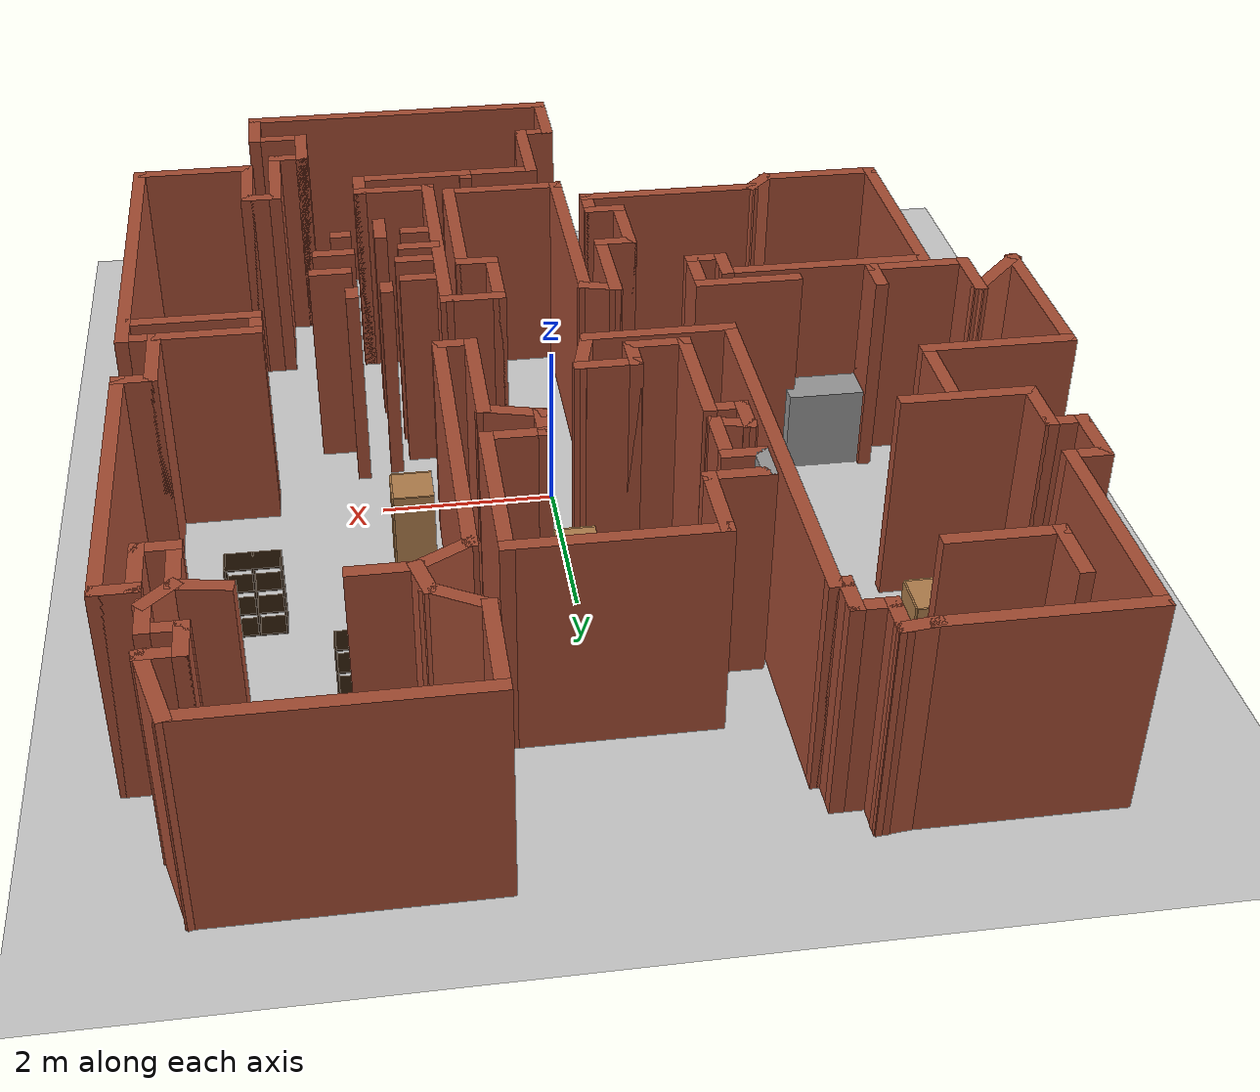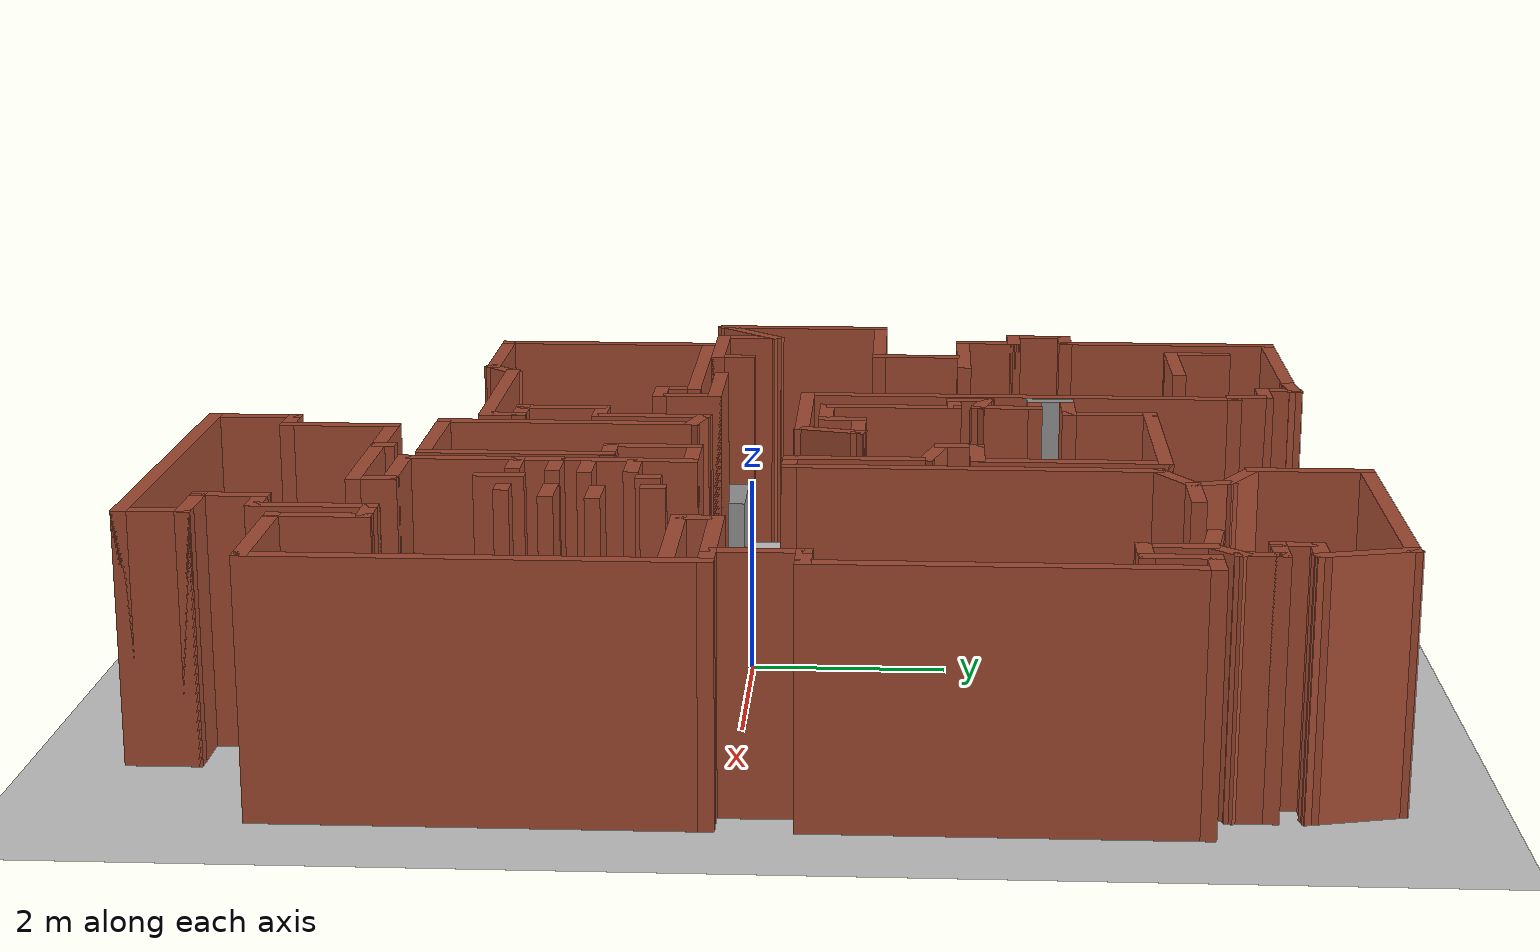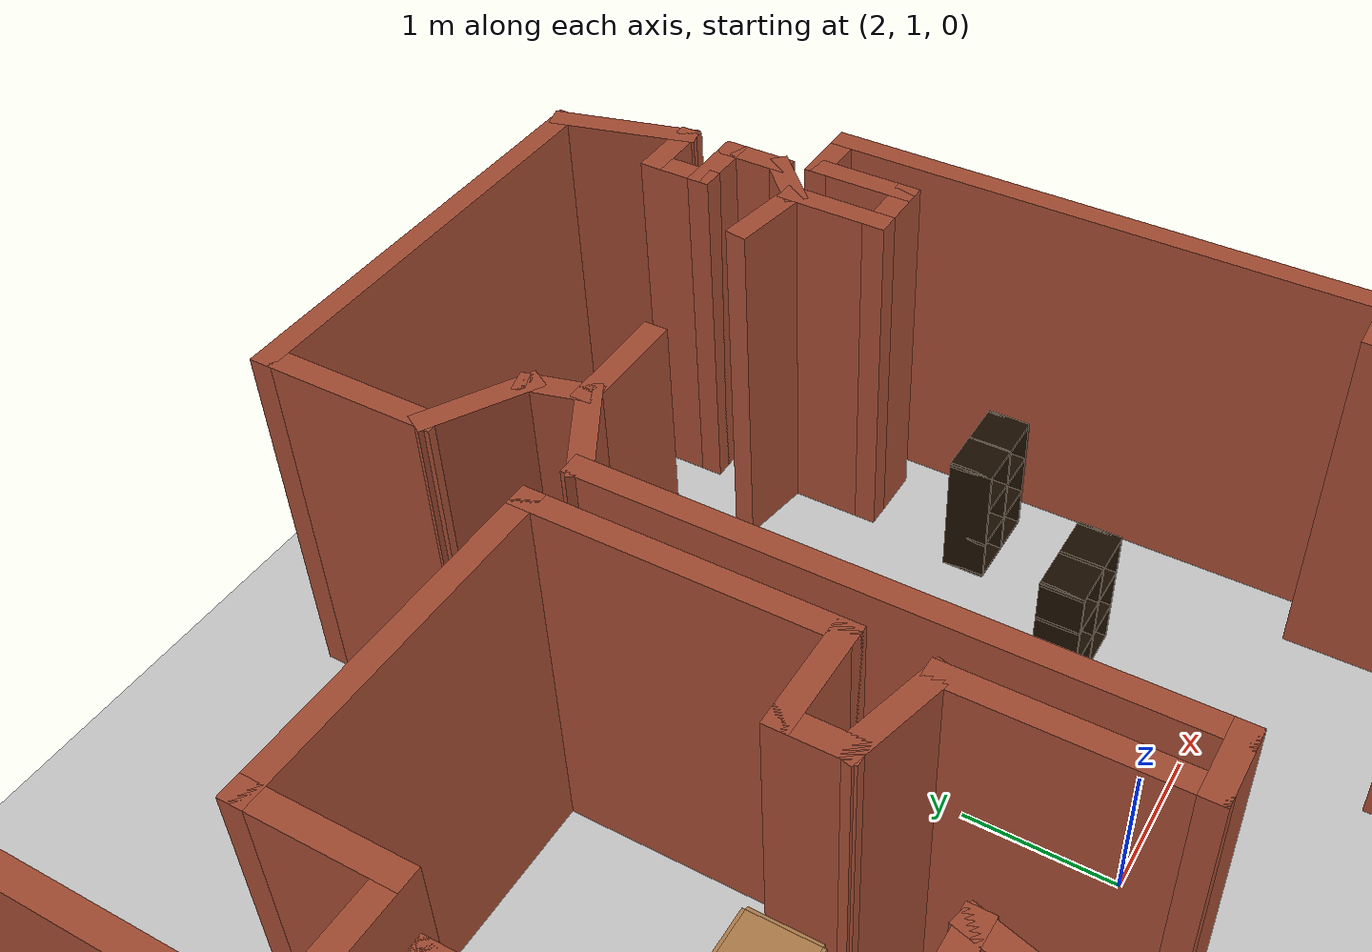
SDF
<sdf version="1.6">
 <world name="default">
  <light name="sun" type="directional">
   <pose>0 0 10 0 -0 0</pose>
   <diffuse>0.8 0.8 0.8 1</diffuse>
   <specular>0.2 0.2 0.2 1</specular>
   <attenuation>
    <range>1000</range>
    <constant>0.9</constant>
    <linear>0.01</linear>
    <quadratic>0.001</quadratic>
   </attenuation>
   <direction>-0.5 0.1 -0.9</direction>
  </light>
  <model name="ground_plane">
   <static>1</static>
   <link name="link">
    <collision name="collision">
     <geometry><plane><normal>0 0 1</normal><size>100 100</size></plane></geometry>
     <surface><friction><ode><mu>100</mu><mu2>50</mu2></ode></friction></surface>
    </collision>
    <visual name="visual">
     <cast_shadows>0</cast_shadows>
     <geometry><plane><normal>0 0 1</normal><size>100 100</size></plane></geometry>
     <material>
      <script><uri>file://media/materials/scripts/gazebo.material</uri><name>Gazebo/Grey</name></script>
     </material>
    </visual>
   </link>
  </model>
  <gravity>0 0 -9.8</gravity>
  <magnetic_field>6e-06 2.3e-05 -4.2e-05</magnetic_field>
  <atmosphere type="adiabatic"/>
  <physics name="default_physics" default="0" type="ode">
   <max_step_size>0.001</max_step_size>
   <real_time_factor>1</real_time_factor>
   <real_time_update_rate>1000</real_time_update_rate>
  </physics>
  <scene><ambient>0.4 0.4 0.4 1</ambient><background>0.7 0.7 0.7 1</background><shadows>1</shadows></scene>
  <spherical_coordinates>
   <surface_model>EARTH_WGS84</surface_model>
   <latitude_deg>0</latitude_deg>
   <longitude_deg>0</longitude_deg>
   <elevation>0</elevation>
   <heading_deg>0</heading_deg>
  </spherical_coordinates>
  <model name="map_45">
   <link name="Wall_0">
    <pose>-3.30096 5.5702 0 0 -0 3.14159</pose>
    <visual name="Wall_0_Visual">
     <pose>0 0 1.25 0 -0 0</pose>
     <geometry><box><size>2.25 0.15 2.5</size></box></geometry>
     <material>
      <script><uri>file://media/materials/scripts/gazebo.material</uri><name>Gazebo/Bricks</name></script>
      <ambient>1 1 1 1</ambient>
      <shader type="pixel"/>
     </material>
     <meta><layer>0</layer></meta>
    </visual>
    <collision name="Wall_0_Collision">
     <pose>0 0 1.25 0 -0 0</pose>
     <geometry><box><size>2.25 0.15 2.5</size></box></geometry>
     <surface>
      <friction>
       <ode><mu>1</mu><mu2>1</mu2><fdir1>0 0 0</fdir1><slip1>0</slip1><slip2>0</slip2></ode>
       <torsional>
        <coefficient>1</coefficient>
        <patch_radius>0</patch_radius>
        <surface_radius>0</surface_radius>
        <use_patch_radius>1</use_patch_radius>
        <ode><slip>0</slip></ode>
       </torsional>
      </friction>
      <bounce><restitution_coefficient>0</restitution_coefficient><threshold>1e+06</threshold></bounce>
      <contact>
       <collide_without_contact>0</collide_without_contact>
       <collide_without_contact_bitmask>1</collide_without_contact_bitmask>
       <collide_bitmask>1</collide_bitmask>
       <ode>
        <soft_cfm>0</soft_cfm>
        <soft_erp>0.2</soft_erp>
        <kp>1e+13</kp>
        <kd>1</kd>
        <max_vel>0.01</max_vel>
        <min_depth>0</min_depth>
       </ode>
       <bullet>
        <split_impulse>1</split_impulse>
        <split_impulse_penetration_threshold>-0.01</split_impulse_penetration_threshold>
        <soft_cfm>0</soft_cfm>
        <soft_erp>0.2</soft_erp>
        <kp>1e+13</kp>
        <kd>1</kd>
       </bullet>
      </contact>
     </surface>
    </collision>
   </link>
   <link name="Wall_1">
    <pose>-4.35096 4.3952 0 0 0 -1.5708</pose>
    <visual name="Wall_1_Visual">
     <pose>0 0 1.25 0 -0 0</pose>
     <geometry><box><size>2.5 0.15 2.5</size></box></geometry>
     <material>
      <script><uri>file://media/materials/scripts/gazebo.material</uri><name>Gazebo/Bricks</name></script>
      <ambient>1 1 1 1</ambient>
      <shader type="pixel"/>
     </material>
     <meta><layer>0</layer></meta>
    </visual>
    <collision name="Wall_1_Collision">
     <pose>0 0 1.25 0 -0 0</pose>
     <geometry><box><size>2.5 0.15 2.5</size></box></geometry>
     <surface>
      <friction>
       <ode><mu>1</mu><mu2>1</mu2><fdir1>0 0 0</fdir1><slip1>0</slip1><slip2>0</slip2></ode>
       <torsional>
        <coefficient>1</coefficient>
        <patch_radius>0</patch_radius>
        <surface_radius>0</surface_radius>
        <use_patch_radius>1</use_patch_radius>
        <ode><slip>0</slip></ode>
       </torsional>
      </friction>
      <bounce><restitution_coefficient>0</restitution_coefficient><threshold>1e+06</threshold></bounce>
      <contact>
       <collide_without_contact>0</collide_without_contact>
       <collide_without_contact_bitmask>1</collide_without_contact_bitmask>
       <collide_bitmask>1</collide_bitmask>
       <ode>
        <soft_cfm>0</soft_cfm>
        <soft_erp>0.2</soft_erp>
        <kp>1e+13</kp>
        <kd>1</kd>
        <max_vel>0.01</max_vel>
        <min_depth>0</min_depth>
       </ode>
       <bullet>
        <split_impulse>1</split_impulse>
        <split_impulse_penetration_threshold>-0.01</split_impulse_penetration_threshold>
        <soft_cfm>0</soft_cfm>
        <soft_erp>0.2</soft_erp>
        <kp>1e+13</kp>
        <kd>1</kd>
       </bullet>
      </contact>
     </surface>
    </collision>
   </link>
   <link name="Wall_10">
    <pose>-5.12777 0.124368 0 0 0 -1.5708</pose>
    <visual name="Wall_10_Visual">
     <pose>0 0 1.25 0 -0 0</pose>
     <geometry><box><size>2 0.15 2.5</size></box></geometry>
     <material>
      <script><uri>file://media/materials/scripts/gazebo.material</uri><name>Gazebo/Bricks</name></script>
      <ambient>1 1 1 1</ambient>
      <shader type="pixel"/>
     </material>
     <meta><layer>0</layer></meta>
    </visual>
    <collision name="Wall_10_Collision">
     <pose>0 0 1.25 0 -0 0</pose>
     <geometry><box><size>2 0.15 2.5</size></box></geometry>
     <surface>
      <friction>
       <ode><mu>1</mu><mu2>1</mu2><fdir1>0 0 0</fdir1><slip1>0</slip1><slip2>0</slip2></ode>
       <torsional>
        <coefficient>1</coefficient>
        <patch_radius>0</patch_radius>
        <surface_radius>0</surface_radius>
        <use_patch_radius>1</use_patch_radius>
        <ode><slip>0</slip></ode>
       </torsional>
      </friction>
      <bounce><restitution_coefficient>0</restitution_coefficient><threshold>1e+06</threshold></bounce>
      <contact>
       <collide_without_contact>0</collide_without_contact>
       <collide_without_contact_bitmask>1</collide_without_contact_bitmask>
       <collide_bitmask>1</collide_bitmask>
       <ode>
        <soft_cfm>0</soft_cfm>
        <soft_erp>0.2</soft_erp>
        <kp>1e+13</kp>
        <kd>1</kd>
        <max_vel>0.01</max_vel>
        <min_depth>0</min_depth>
       </ode>
       <bullet>
        <split_impulse>1</split_impulse>
        <split_impulse_penetration_threshold>-0.01</split_impulse_penetration_threshold>
        <soft_cfm>0</soft_cfm>
        <soft_erp>0.2</soft_erp>
        <kp>1e+13</kp>
        <kd>1</kd>
       </bullet>
      </contact>
     </surface>
    </collision>
   </link>
   <link name="Wall_100">
    <pose>-0.702644 3.51805 0 0 0 -1.5708</pose>
    <visual name="Wall_100_Visual">
     <pose>0 0 1.25 0 -0 0</pose>
     <geometry><box><size>1 0.15 2.5</size></box></geometry>
     <material>
      <script><uri>file://media/materials/scripts/gazebo.material</uri><name>Gazebo/Bricks</name></script>
      <ambient>1 1 1 1</ambient>
      <shader type="pixel"/>
     </material>
     <meta><layer>0</layer></meta>
    </visual>
    <collision name="Wall_100_Collision">
     <pose>0 0 1.25 0 -0 0</pose>
     <geometry><box><size>1 0.15 2.5</size></box></geometry>
     <surface>
      <friction>
       <ode><mu>1</mu><mu2>1</mu2><fdir1>0 0 0</fdir1><slip1>0</slip1><slip2>0</slip2></ode>
       <torsional>
        <coefficient>1</coefficient>
        <patch_radius>0</patch_radius>
        <surface_radius>0</surface_radius>
        <use_patch_radius>1</use_patch_radius>
        <ode><slip>0</slip></ode>
       </torsional>
      </friction>
      <bounce><restitution_coefficient>0</restitution_coefficient><threshold>1e+06</threshold></bounce>
      <contact>
       <collide_without_contact>0</collide_without_contact>
       <collide_without_contact_bitmask>1</collide_without_contact_bitmask>
       <collide_bitmask>1</collide_bitmask>
       <ode>
        <soft_cfm>0</soft_cfm>
        <soft_erp>0.2</soft_erp>
        <kp>1e+13</kp>
        <kd>1</kd>
        <max_vel>0.01</max_vel>
        <min_depth>0</min_depth>
       </ode>
       <bullet>
        <split_impulse>1</split_impulse>
        <split_impulse_penetration_threshold>-0.01</split_impulse_penetration_threshold>
        <soft_cfm>0</soft_cfm>
        <soft_erp>0.2</soft_erp>
        <kp>1e+13</kp>
        <kd>1</kd>
       </bullet>
      </contact>
     </surface>
    </collision>
   </link>
   <link name="Wall_101">
    <pose>-1.00264 3.09305 0 0 -0 3.14159</pose>
    <visual name="Wall_101_Visual">
     <pose>0 0 1.25 0 -0 0</pose>
     <geometry><box><size>0.75 0.15 2.5</size></box></geometry>
     <material>
      <script><uri>file://media/materials/scripts/gazebo.material</uri><name>Gazebo/Bricks</name></script>
      <ambient>1 1 1 1</ambient>
      <shader type="pixel"/>
     </material>
     <meta><layer>0</layer></meta>
    </visual>
    <collision name="Wall_101_Collision">
     <pose>0 0 1.25 0 -0 0</pose>
     <geometry><box><size>0.75 0.15 2.5</size></box></geometry>
     <surface>
      <friction>
       <ode><mu>1</mu><mu2>1</mu2><fdir1>0 0 0</fdir1><slip1>0</slip1><slip2>0</slip2></ode>
       <torsional>
        <coefficient>1</coefficient>
        <patch_radius>0</patch_radius>
        <surface_radius>0</surface_radius>
        <use_patch_radius>1</use_patch_radius>
        <ode><slip>0</slip></ode>
       </torsional>
      </friction>
      <bounce><restitution_coefficient>0</restitution_coefficient><threshold>1e+06</threshold></bounce>
      <contact>
       <collide_without_contact>0</collide_without_contact>
       <collide_without_contact_bitmask>1</collide_without_contact_bitmask>
       <collide_bitmask>1</collide_bitmask>
       <ode>
        <soft_cfm>0</soft_cfm>
        <soft_erp>0.2</soft_erp>
        <kp>1e+13</kp>
        <kd>1</kd>
        <max_vel>0.01</max_vel>
        <min_depth>0</min_depth>
       </ode>
       <bullet>
        <split_impulse>1</split_impulse>
        <split_impulse_penetration_threshold>-0.01</split_impulse_penetration_threshold>
        <soft_cfm>0</soft_cfm>
        <soft_erp>0.2</soft_erp>
        <kp>1e+13</kp>
        <kd>1</kd>
       </bullet>
      </contact>
     </surface>
    </collision>
   </link>
   <link name="Wall_102">
    <pose>-1.30264 2.91805 0 0 0 -1.5708</pose>
    <visual name="Wall_102_Visual">
     <pose>0 0 1.25 0 -0 0</pose>
     <geometry><box><size>0.5 0.15 2.5</size></box></geometry>
     <material>
      <script><uri>file://media/materials/scripts/gazebo.material</uri><name>Gazebo/Grey</name></script>
      <ambient>1 1 1 1</ambient>
      <shader type="pixel"/>
     </material>
     <meta><layer>0</layer></meta>
    </visual>
    <collision name="Wall_102_Collision">
     <pose>0 0 1.25 0 -0 0</pose>
     <geometry><box><size>0.5 0.15 2.5</size></box></geometry>
     <surface>
      <friction>
       <ode><mu>1</mu><mu2>1</mu2><fdir1>0 0 0</fdir1><slip1>0</slip1><slip2>0</slip2></ode>
       <torsional>
        <coefficient>1</coefficient>
        <patch_radius>0</patch_radius>
        <surface_radius>0</surface_radius>
        <use_patch_radius>1</use_patch_radius>
        <ode><slip>0</slip></ode>
       </torsional>
      </friction>
      <bounce><restitution_coefficient>0</restitution_coefficient><threshold>1e+06</threshold></bounce>
      <contact>
       <collide_without_contact>0</collide_without_contact>
       <collide_without_contact_bitmask>1</collide_without_contact_bitmask>
       <collide_bitmask>1</collide_bitmask>
       <ode>
        <soft_cfm>0</soft_cfm>
        <soft_erp>0.2</soft_erp>
        <kp>1e+13</kp>
        <kd>1</kd>
        <max_vel>0.01</max_vel>
        <min_depth>0</min_depth>
       </ode>
       <bullet>
        <split_impulse>1</split_impulse>
        <split_impulse_penetration_threshold>-0.01</split_impulse_penetration_threshold>
        <soft_cfm>0</soft_cfm>
        <soft_erp>0.2</soft_erp>
        <kp>1e+13</kp>
        <kd>1</kd>
       </bullet>
      </contact>
     </surface>
    </collision>
   </link>
   <link name="Wall_103">
    <pose>-1.12764 2.74305 0 0 -0 0</pose>
    <visual name="Wall_103_Visual">
     <pose>0 0 1.25 0 -0 0</pose>
     <geometry><box><size>0.5 0.15 2.5</size></box></geometry>
     <material>
      <script><uri>file://media/materials/scripts/gazebo.material</uri><name>Gazebo/Bricks</name></script>
      <ambient>1 1 1 1</ambient>
      <shader type="pixel"/>
     </material>
     <meta><layer>0</layer></meta>
    </visual>
    <collision name="Wall_103_Collision">
     <pose>0 0 1.25 0 -0 0</pose>
     <geometry><box><size>0.5 0.15 2.5</size></box></geometry>
     <surface>
      <friction>
       <ode><mu>1</mu><mu2>1</mu2><fdir1>0 0 0</fdir1><slip1>0</slip1><slip2>0</slip2></ode>
       <torsional>
        <coefficient>1</coefficient>
        <patch_radius>0</patch_radius>
        <surface_radius>0</surface_radius>
        <use_patch_radius>1</use_patch_radius>
        <ode><slip>0</slip></ode>
       </torsional>
      </friction>
      <bounce><restitution_coefficient>0</restitution_coefficient><threshold>1e+06</threshold></bounce>
      <contact>
       <collide_without_contact>0</collide_without_contact>
       <collide_without_contact_bitmask>1</collide_without_contact_bitmask>
       <collide_bitmask>1</collide_bitmask>
       <ode>
        <soft_cfm>0</soft_cfm>
        <soft_erp>0.2</soft_erp>
        <kp>1e+13</kp>
        <kd>1</kd>
        <max_vel>0.01</max_vel>
        <min_depth>0</min_depth>
       </ode>
       <bullet>
        <split_impulse>1</split_impulse>
        <split_impulse_penetration_threshold>-0.01</split_impulse_penetration_threshold>
        <soft_cfm>0</soft_cfm>
        <soft_erp>0.2</soft_erp>
        <kp>1e+13</kp>
        <kd>1</kd>
       </bullet>
      </contact>
     </surface>
    </collision>
   </link>
   <link name="Wall_104">
    <pose>-0.952644 2.44305 0 0 0 -1.5708</pose>
    <visual name="Wall_104_Visual">
     <pose>0 0 1.25 0 -0 0</pose>
     <geometry><box><size>0.75 0.15 2.5</size></box></geometry>
     <material>
      <script><uri>file://media/materials/scripts/gazebo.material</uri><name>Gazebo/Bricks</name></script>
      <ambient>1 1 1 1</ambient>
      <shader type="pixel"/>
     </material>
     <meta><layer>0</layer></meta>
    </visual>
    <collision name="Wall_104_Collision">
     <pose>0 0 1.25 0 -0 0</pose>
     <geometry><box><size>0.75 0.15 2.5</size></box></geometry>
     <surface>
      <friction>
       <ode><mu>1</mu><mu2>1</mu2><fdir1>0 0 0</fdir1><slip1>0</slip1><slip2>0</slip2></ode>
       <torsional>
        <coefficient>1</coefficient>
        <patch_radius>0</patch_radius>
        <surface_radius>0</surface_radius>
        <use_patch_radius>1</use_patch_radius>
        <ode><slip>0</slip></ode>
       </torsional>
      </friction>
      <bounce><restitution_coefficient>0</restitution_coefficient><threshold>1e+06</threshold></bounce>
      <contact>
       <collide_without_contact>0</collide_without_contact>
       <collide_without_contact_bitmask>1</collide_without_contact_bitmask>
       <collide_bitmask>1</collide_bitmask>
       <ode>
        <soft_cfm>0</soft_cfm>
        <soft_erp>0.2</soft_erp>
        <kp>1e+13</kp>
        <kd>1</kd>
        <max_vel>0.01</max_vel>
        <min_depth>0</min_depth>
       </ode>
       <bullet>
        <split_impulse>1</split_impulse>
        <split_impulse_penetration_threshold>-0.01</split_impulse_penetration_threshold>
        <soft_cfm>0</soft_cfm>
        <soft_erp>0.2</soft_erp>
        <kp>1e+13</kp>
        <kd>1</kd>
       </bullet>
      </contact>
     </surface>
    </collision>
   </link>
   <link name="Wall_105">
    <pose>-1.12168 2.18834 0 0 -0 2.87979</pose>
    <visual name="Wall_105_Visual">
     <pose>0 0 1.25 0 -0 0</pose>
     <geometry><box><size>0.5 0.15 2.5</size></box></geometry>
     <material>
      <script><uri>file://media/materials/scripts/gazebo.material</uri><name>Gazebo/Bricks</name></script>
      <ambient>1 1 1 1</ambient>
      <shader type="pixel"/>
     </material>
     <meta><layer>0</layer></meta>
    </visual>
    <collision name="Wall_105_Collision">
     <pose>0 0 1.25 0 -0 0</pose>
     <geometry><box><size>0.5 0.15 2.5</size></box></geometry>
     <surface>
      <friction>
       <ode><mu>1</mu><mu2>1</mu2><fdir1>0 0 0</fdir1><slip1>0</slip1><slip2>0</slip2></ode>
       <torsional>
        <coefficient>1</coefficient>
        <patch_radius>0</patch_radius>
        <surface_radius>0</surface_radius>
        <use_patch_radius>1</use_patch_radius>
        <ode><slip>0</slip></ode>
       </torsional>
      </friction>
      <bounce><restitution_coefficient>0</restitution_coefficient><threshold>1e+06</threshold></bounce>
      <contact>
       <collide_without_contact>0</collide_without_contact>
       <collide_without_contact_bitmask>1</collide_without_contact_bitmask>
       <collide_bitmask>1</collide_bitmask>
       <ode>
        <soft_cfm>0</soft_cfm>
        <soft_erp>0.2</soft_erp>
        <kp>1e+13</kp>
        <kd>1</kd>
        <max_vel>0.01</max_vel>
        <min_depth>0</min_depth>
       </ode>
       <bullet>
        <split_impulse>1</split_impulse>
        <split_impulse_penetration_threshold>-0.01</split_impulse_penetration_threshold>
        <soft_cfm>0</soft_cfm>
        <soft_erp>0.2</soft_erp>
        <kp>1e+13</kp>
        <kd>1</kd>
       </bullet>
      </contact>
     </surface>
    </collision>
   </link>
   <link name="Wall_106">
    <pose>-1.29072 2.05864 0 0 0 -1.5708</pose>
    <visual name="Wall_106_Visual">
     <pose>0 0 1.25 0 -0 0</pose>
     <geometry><box><size>0.5 0.15 2.5</size></box></geometry>
     <material>
      <script><uri>file://media/materials/scripts/gazebo.material</uri><name>Gazebo/Bricks</name></script>
      <ambient>1 1 1 1</ambient>
      <shader type="pixel"/>
     </material>
     <meta><layer>0</layer></meta>
    </visual>
    <collision name="Wall_106_Collision">
     <pose>0 0 1.25 0 -0 0</pose>
     <geometry><box><size>0.5 0.15 2.5</size></box></geometry>
     <surface>
      <friction>
       <ode><mu>1</mu><mu2>1</mu2><fdir1>0 0 0</fdir1><slip1>0</slip1><slip2>0</slip2></ode>
       <torsional>
        <coefficient>1</coefficient>
        <patch_radius>0</patch_radius>
        <surface_radius>0</surface_radius>
        <use_patch_radius>1</use_patch_radius>
        <ode><slip>0</slip></ode>
       </torsional>
      </friction>
      <bounce><restitution_coefficient>0</restitution_coefficient><threshold>1e+06</threshold></bounce>
      <contact>
       <collide_without_contact>0</collide_without_contact>
       <collide_without_contact_bitmask>1</collide_without_contact_bitmask>
       <collide_bitmask>1</collide_bitmask>
       <ode>
        <soft_cfm>0</soft_cfm>
        <soft_erp>0.2</soft_erp>
        <kp>1e+13</kp>
        <kd>1</kd>
        <max_vel>0.01</max_vel>
        <min_depth>0</min_depth>
       </ode>
       <bullet>
        <split_impulse>1</split_impulse>
        <split_impulse_penetration_threshold>-0.01</split_impulse_penetration_threshold>
        <soft_cfm>0</soft_cfm>
        <soft_erp>0.2</soft_erp>
        <kp>1e+13</kp>
        <kd>1</kd>
       </bullet>
      </contact>
     </surface>
    </collision>
   </link>
   <link name="Wall_107">
    <pose>-1.11572 1.88364 0 0 -0 0</pose>
    <visual name="Wall_107_Visual">
     <pose>0 0 1.25 0 -0 0</pose>
     <geometry><box><size>0.5 0.15 2.5</size></box></geometry>
     <material>
      <script><uri>file://media/materials/scripts/gazebo.material</uri><name>Gazebo/Bricks</name></script>
      <ambient>1 1 1 1</ambient>
      <shader type="pixel"/>
     </material>
     <meta><layer>0</layer></meta>
    </visual>
    <collision name="Wall_107_Collision">
     <pose>0 0 1.25 0 -0 0</pose>
     <geometry><box><size>0.5 0.15 2.5</size></box></geometry>
     <surface>
      <friction>
       <ode><mu>1</mu><mu2>1</mu2><fdir1>0 0 0</fdir1><slip1>0</slip1><slip2>0</slip2></ode>
       <torsional>
        <coefficient>1</coefficient>
        <patch_radius>0</patch_radius>
        <surface_radius>0</surface_radius>
        <use_patch_radius>1</use_patch_radius>
        <ode><slip>0</slip></ode>
       </torsional>
      </friction>
      <bounce><restitution_coefficient>0</restitution_coefficient><threshold>1e+06</threshold></bounce>
      <contact>
       <collide_without_contact>0</collide_without_contact>
       <collide_without_contact_bitmask>1</collide_without_contact_bitmask>
       <collide_bitmask>1</collide_bitmask>
       <ode>
        <soft_cfm>0</soft_cfm>
        <soft_erp>0.2</soft_erp>
        <kp>1e+13</kp>
        <kd>1</kd>
        <max_vel>0.01</max_vel>
        <min_depth>0</min_depth>
       </ode>
       <bullet>
        <split_impulse>1</split_impulse>
        <split_impulse_penetration_threshold>-0.01</split_impulse_penetration_threshold>
        <soft_cfm>0</soft_cfm>
        <soft_erp>0.2</soft_erp>
        <kp>1e+13</kp>
        <kd>1</kd>
       </bullet>
      </contact>
     </surface>
    </collision>
   </link>
   <link name="Wall_108">
    <pose>-0.940718 1.20864 0 0 0 -1.5708</pose>
    <visual name="Wall_108_Visual">
     <pose>0 0 1.25 0 -0 0</pose>
     <geometry><box><size>1.5 0.15 2.5</size></box></geometry>
     <material>
      <script><uri>file://media/materials/scripts/gazebo.material</uri><name>Gazebo/Bricks</name></script>
      <ambient>1 1 1 1</ambient>
      <shader type="pixel"/>
     </material>
     <meta><layer>0</layer></meta>
    </visual>
    <collision name="Wall_108_Collision">
     <pose>0 0 1.25 0 -0 0</pose>
     <geometry><box><size>1.5 0.15 2.5</size></box></geometry>
     <surface>
      <friction>
       <ode><mu>1</mu><mu2>1</mu2><fdir1>0 0 0</fdir1><slip1>0</slip1><slip2>0</slip2></ode>
       <torsional>
        <coefficient>1</coefficient>
        <patch_radius>0</patch_radius>
        <surface_radius>0</surface_radius>
        <use_patch_radius>1</use_patch_radius>
        <ode><slip>0</slip></ode>
       </torsional>
      </friction>
      <bounce><restitution_coefficient>0</restitution_coefficient><threshold>1e+06</threshold></bounce>
      <contact>
       <collide_without_contact>0</collide_without_contact>
       <collide_without_contact_bitmask>1</collide_without_contact_bitmask>
       <collide_bitmask>1</collide_bitmask>
       <ode>
        <soft_cfm>0</soft_cfm>
        <soft_erp>0.2</soft_erp>
        <kp>1e+13</kp>
        <kd>1</kd>
        <max_vel>0.01</max_vel>
        <min_depth>0</min_depth>
       </ode>
       <bullet>
        <split_impulse>1</split_impulse>
        <split_impulse_penetration_threshold>-0.01</split_impulse_penetration_threshold>
        <soft_cfm>0</soft_cfm>
        <soft_erp>0.2</soft_erp>
        <kp>1e+13</kp>
        <kd>1</kd>
       </bullet>
      </contact>
     </surface>
    </collision>
   </link>
   <link name="Wall_109">
    <pose>-0.640718 0.533638 0 0 -0 0</pose>
    <visual name="Wall_109_Visual">
     <pose>0 0 1.25 0 -0 0</pose>
     <geometry><box><size>0.75 0.15 2.5</size></box></geometry>
     <material>
      <script><uri>file://media/materials/scripts/gazebo.material</uri><name>Gazebo/Bricks</name></script>
      <ambient>1 1 1 1</ambient>
      <shader type="pixel"/>
     </material>
     <meta><layer>0</layer></meta>
    </visual>
    <collision name="Wall_109_Collision">
     <pose>0 0 1.25 0 -0 0</pose>
     <geometry><box><size>0.75 0.15 2.5</size></box></geometry>
     <surface>
      <friction>
       <ode><mu>1</mu><mu2>1</mu2><fdir1>0 0 0</fdir1><slip1>0</slip1><slip2>0</slip2></ode>
       <torsional>
        <coefficient>1</coefficient>
        <patch_radius>0</patch_radius>
        <surface_radius>0</surface_radius>
        <use_patch_radius>1</use_patch_radius>
        <ode><slip>0</slip></ode>
       </torsional>
      </friction>
      <bounce><restitution_coefficient>0</restitution_coefficient><threshold>1e+06</threshold></bounce>
      <contact>
       <collide_without_contact>0</collide_without_contact>
       <collide_without_contact_bitmask>1</collide_without_contact_bitmask>
       <collide_bitmask>1</collide_bitmask>
       <ode>
        <soft_cfm>0</soft_cfm>
        <soft_erp>0.2</soft_erp>
        <kp>1e+13</kp>
        <kd>1</kd>
        <max_vel>0.01</max_vel>
        <min_depth>0</min_depth>
       </ode>
       <bullet>
        <split_impulse>1</split_impulse>
        <split_impulse_penetration_threshold>-0.01</split_impulse_penetration_threshold>
        <soft_cfm>0</soft_cfm>
        <soft_erp>0.2</soft_erp>
        <kp>1e+13</kp>
        <kd>1</kd>
       </bullet>
      </contact>
     </surface>
    </collision>
   </link>
   <link name="Wall_11">
    <pose>-4.82725 -0.500111 0 0 -0 0.785398</pose>
    <visual name="Wall_11_Visual">
     <pose>0 0 1.25 0 -0 0</pose>
     <geometry><box><size>1 0.15 2.5</size></box></geometry>
     <material>
      <script><uri>file://media/materials/scripts/gazebo.material</uri><name>Gazebo/Bricks</name></script>
      <ambient>1 1 1 1</ambient>
      <shader type="pixel"/>
     </material>
     <meta><layer>0</layer></meta>
    </visual>
    <collision name="Wall_11_Collision">
     <pose>0 0 1.25 0 -0 0</pose>
     <geometry><box><size>1 0.15 2.5</size></box></geometry>
     <surface>
      <friction>
       <ode><mu>1</mu><mu2>1</mu2><fdir1>0 0 0</fdir1><slip1>0</slip1><slip2>0</slip2></ode>
       <torsional>
        <coefficient>1</coefficient>
        <patch_radius>0</patch_radius>
        <surface_radius>0</surface_radius>
        <use_patch_radius>1</use_patch_radius>
        <ode><slip>0</slip></ode>
       </torsional>
      </friction>
      <bounce><restitution_coefficient>0</restitution_coefficient><threshold>1e+06</threshold></bounce>
      <contact>
       <collide_without_contact>0</collide_without_contact>
       <collide_without_contact_bitmask>1</collide_without_contact_bitmask>
       <collide_bitmask>1</collide_bitmask>
       <ode>
        <soft_cfm>0</soft_cfm>
        <soft_erp>0.2</soft_erp>
        <kp>1e+13</kp>
        <kd>1</kd>
        <max_vel>0.01</max_vel>
        <min_depth>0</min_depth>
       </ode>
       <bullet>
        <split_impulse>1</split_impulse>
        <split_impulse_penetration_threshold>-0.01</split_impulse_penetration_threshold>
        <soft_cfm>0</soft_cfm>
        <soft_erp>0.2</soft_erp>
        <kp>1e+13</kp>
        <kd>1</kd>
       </bullet>
      </contact>
     </surface>
    </collision>
   </link>
   <link name="Wall_110">
    <pose>-0.340718 0.708638 0 0 -0 1.5708</pose>
    <visual name="Wall_110_Visual">
     <pose>0 0 1.25 0 -0 0</pose>
     <geometry><box><size>0.5 0.15 2.5</size></box></geometry>
     <material>
      <script><uri>file://media/materials/scripts/gazebo.material</uri><name>Gazebo/Bricks</name></script>
      <ambient>1 1 1 1</ambient>
      <shader type="pixel"/>
     </material>
     <meta><layer>0</layer></meta>
    </visual>
    <collision name="Wall_110_Collision">
     <pose>0 0 1.25 0 -0 0</pose>
     <geometry><box><size>0.5 0.15 2.5</size></box></geometry>
     <surface>
      <friction>
       <ode><mu>1</mu><mu2>1</mu2><fdir1>0 0 0</fdir1><slip1>0</slip1><slip2>0</slip2></ode>
       <torsional>
        <coefficient>1</coefficient>
        <patch_radius>0</patch_radius>
        <surface_radius>0</surface_radius>
        <use_patch_radius>1</use_patch_radius>
        <ode><slip>0</slip></ode>
       </torsional>
      </friction>
      <bounce><restitution_coefficient>0</restitution_coefficient><threshold>1e+06</threshold></bounce>
      <contact>
       <collide_without_contact>0</collide_without_contact>
       <collide_without_contact_bitmask>1</collide_without_contact_bitmask>
       <collide_bitmask>1</collide_bitmask>
       <ode>
        <soft_cfm>0</soft_cfm>
        <soft_erp>0.2</soft_erp>
        <kp>1e+13</kp>
        <kd>1</kd>
        <max_vel>0.01</max_vel>
        <min_depth>0</min_depth>
       </ode>
       <bullet>
        <split_impulse>1</split_impulse>
        <split_impulse_penetration_threshold>-0.01</split_impulse_penetration_threshold>
        <soft_cfm>0</soft_cfm>
        <soft_erp>0.2</soft_erp>
        <kp>1e+13</kp>
        <kd>1</kd>
       </bullet>
      </contact>
     </surface>
    </collision>
   </link>
   <link name="Wall_111">
    <pose>-0.040718 0.883638 0 0 -0 0</pose>
    <visual name="Wall_111_Visual">
     <pose>0 0 1.25 0 -0 0</pose>
     <geometry><box><size>0.75 0.15 2.5</size></box></geometry>
     <material>
      <script><uri>file://media/materials/scripts/gazebo.material</uri><name>Gazebo/Bricks</name></script>
      <ambient>1 1 1 1</ambient>
      <shader type="pixel"/>
     </material>
     <meta><layer>0</layer></meta>
    </visual>
    <collision name="Wall_111_Collision">
     <pose>0 0 1.25 0 -0 0</pose>
     <geometry><box><size>0.75 0.15 2.5</size></box></geometry>
     <surface>
      <friction>
       <ode><mu>1</mu><mu2>1</mu2><fdir1>0 0 0</fdir1><slip1>0</slip1><slip2>0</slip2></ode>
       <torsional>
        <coefficient>1</coefficient>
        <patch_radius>0</patch_radius>
        <surface_radius>0</surface_radius>
        <use_patch_radius>1</use_patch_radius>
        <ode><slip>0</slip></ode>
       </torsional>
      </friction>
      <bounce><restitution_coefficient>0</restitution_coefficient><threshold>1e+06</threshold></bounce>
      <contact>
       <collide_without_contact>0</collide_without_contact>
       <collide_without_contact_bitmask>1</collide_without_contact_bitmask>
       <collide_bitmask>1</collide_bitmask>
       <ode>
        <soft_cfm>0</soft_cfm>
        <soft_erp>0.2</soft_erp>
        <kp>1e+13</kp>
        <kd>1</kd>
        <max_vel>0.01</max_vel>
        <min_depth>0</min_depth>
       </ode>
       <bullet>
        <split_impulse>1</split_impulse>
        <split_impulse_penetration_threshold>-0.01</split_impulse_penetration_threshold>
        <soft_cfm>0</soft_cfm>
        <soft_erp>0.2</soft_erp>
        <kp>1e+13</kp>
        <kd>1</kd>
       </bullet>
      </contact>
     </surface>
    </collision>
   </link>
   <link name="Wall_112">
    <pose>0.181636 0.593861 0 0 0 -1.8326</pose>
    <visual name="Wall_112_Visual">
     <pose>0 0 1.25 0 -0 0</pose>
     <geometry><box><size>0.75 0.15 2.5</size></box></geometry>
     <material>
      <script><uri>file://media/materials/scripts/gazebo.material</uri><name>Gazebo/Bricks</name></script>
      <ambient>1 1 1 1</ambient>
      <shader type="pixel"/>
     </material>
     <meta><layer>0</layer></meta>
    </visual>
    <collision name="Wall_112_Collision">
     <pose>0 0 1.25 0 -0 0</pose>
     <geometry><box><size>0.75 0.15 2.5</size></box></geometry>
     <surface>
      <friction>
       <ode><mu>1</mu><mu2>1</mu2><fdir1>0 0 0</fdir1><slip1>0</slip1><slip2>0</slip2></ode>
       <torsional>
        <coefficient>1</coefficient>
        <patch_radius>0</patch_radius>
        <surface_radius>0</surface_radius>
        <use_patch_radius>1</use_patch_radius>
        <ode><slip>0</slip></ode>
       </torsional>
      </friction>
      <bounce><restitution_coefficient>0</restitution_coefficient><threshold>1e+06</threshold></bounce>
      <contact>
       <collide_without_contact>0</collide_without_contact>
       <collide_without_contact_bitmask>1</collide_without_contact_bitmask>
       <collide_bitmask>1</collide_bitmask>
       <ode>
        <soft_cfm>0</soft_cfm>
        <soft_erp>0.2</soft_erp>
        <kp>1e+13</kp>
        <kd>1</kd>
        <max_vel>0.01</max_vel>
        <min_depth>0</min_depth>
       </ode>
       <bullet>
        <split_impulse>1</split_impulse>
        <split_impulse_penetration_threshold>-0.01</split_impulse_penetration_threshold>
        <soft_cfm>0</soft_cfm>
        <soft_erp>0.2</soft_erp>
        <kp>1e+13</kp>
        <kd>1</kd>
       </bullet>
      </contact>
     </surface>
    </collision>
   </link>
   <link name="Wall_113">
    <pose>-0.696009 0.304083 0 0 -0 3.14159</pose>
    <visual name="Wall_113_Visual">
     <pose>0 0 1.25 0 -0 0</pose>
     <geometry><box><size>1.75 0.15 2.5</size></box></geometry>
     <material>
      <script><uri>file://media/materials/scripts/gazebo.material</uri><name>Gazebo/Bricks</name></script>
      <ambient>1 1 1 1</ambient>
      <shader type="pixel"/>
     </material>
     <meta><layer>0</layer></meta>
    </visual>
    <collision name="Wall_113_Collision">
     <pose>0 0 1.25 0 -0 0</pose>
     <geometry><box><size>1.75 0.15 2.5</size></box></geometry>
     <surface>
      <friction>
       <ode><mu>1</mu><mu2>1</mu2><fdir1>0 0 0</fdir1><slip1>0</slip1><slip2>0</slip2></ode>
       <torsional>
        <coefficient>1</coefficient>
        <patch_radius>0</patch_radius>
        <surface_radius>0</surface_radius>
        <use_patch_radius>1</use_patch_radius>
        <ode><slip>0</slip></ode>
       </torsional>
      </friction>
      <bounce><restitution_coefficient>0</restitution_coefficient><threshold>1e+06</threshold></bounce>
      <contact>
       <collide_without_contact>0</collide_without_contact>
       <collide_without_contact_bitmask>1</collide_without_contact_bitmask>
       <collide_bitmask>1</collide_bitmask>
       <ode>
        <soft_cfm>0</soft_cfm>
        <soft_erp>0.2</soft_erp>
        <kp>1e+13</kp>
        <kd>1</kd>
        <max_vel>0.01</max_vel>
        <min_depth>0</min_depth>
       </ode>
       <bullet>
        <split_impulse>1</split_impulse>
        <split_impulse_penetration_threshold>-0.01</split_impulse_penetration_threshold>
        <soft_cfm>0</soft_cfm>
        <soft_erp>0.2</soft_erp>
        <kp>1e+13</kp>
        <kd>1</kd>
       </bullet>
      </contact>
     </surface>
    </collision>
   </link>
   <link name="Wall_114">
    <pose>-1.49601 2.60408 0 0 -0 1.5708</pose>
    <visual name="Wall_114_Visual">
     <pose>0 0 1.25 0 -0 0</pose>
     <geometry><box><size>4.75 0.15 2.5</size></box></geometry>
     <material>
      <script><uri>file://media/materials/scripts/gazebo.material</uri><name>Gazebo/Bricks</name></script>
      <ambient>1 1 1 1</ambient>
      <shader type="pixel"/>
     </material>
     <meta><layer>0</layer></meta>
    </visual>
    <collision name="Wall_114_Collision">
     <pose>0 0 1.25 0 -0 0</pose>
     <geometry><box><size>4.75 0.15 2.5</size></box></geometry>
     <surface>
      <friction>
       <ode><mu>1</mu><mu2>1</mu2><fdir1>0 0 0</fdir1><slip1>0</slip1><slip2>0</slip2></ode>
       <torsional>
        <coefficient>1</coefficient>
        <patch_radius>0</patch_radius>
        <surface_radius>0</surface_radius>
        <use_patch_radius>1</use_patch_radius>
        <ode><slip>0</slip></ode>
       </torsional>
      </friction>
      <bounce><restitution_coefficient>0</restitution_coefficient><threshold>1e+06</threshold></bounce>
      <contact>
       <collide_without_contact>0</collide_without_contact>
       <collide_without_contact_bitmask>1</collide_without_contact_bitmask>
       <collide_bitmask>1</collide_bitmask>
       <ode>
        <soft_cfm>0</soft_cfm>
        <soft_erp>0.2</soft_erp>
        <kp>1e+13</kp>
        <kd>1</kd>
        <max_vel>0.01</max_vel>
        <min_depth>0</min_depth>
       </ode>
       <bullet>
        <split_impulse>1</split_impulse>
        <split_impulse_penetration_threshold>-0.01</split_impulse_penetration_threshold>
        <soft_cfm>0</soft_cfm>
        <soft_erp>0.2</soft_erp>
        <kp>1e+13</kp>
        <kd>1</kd>
       </bullet>
      </contact>
     </surface>
    </collision>
   </link>
   <link name="Wall_115">
    <pose>-1.54601 4.90408 0 0 -0 3.14159</pose>
    <visual name="Wall_115_Visual">
     <pose>0 0 1.25 0 -0 0</pose>
     <geometry><box><size>0.25 0.15 2.5</size></box></geometry>
     <material>
      <script><uri>file://media/materials/scripts/gazebo.material</uri><name>Gazebo/Bricks</name></script>
      <ambient>1 1 1 1</ambient>
      <shader type="pixel"/>
     </material>
     <meta><layer>0</layer></meta>
    </visual>
    <collision name="Wall_115_Collision">
     <pose>0 0 1.25 0 -0 0</pose>
     <geometry><box><size>0.25 0.15 2.5</size></box></geometry>
     <surface>
      <friction>
       <ode><mu>1</mu><mu2>1</mu2><fdir1>0 0 0</fdir1><slip1>0</slip1><slip2>0</slip2></ode>
       <torsional>
        <coefficient>1</coefficient>
        <patch_radius>0</patch_radius>
        <surface_radius>0</surface_radius>
        <use_patch_radius>1</use_patch_radius>
        <ode><slip>0</slip></ode>
       </torsional>
      </friction>
      <bounce><restitution_coefficient>0</restitution_coefficient><threshold>1e+06</threshold></bounce>
      <contact>
       <collide_without_contact>0</collide_without_contact>
       <collide_without_contact_bitmask>1</collide_without_contact_bitmask>
       <collide_bitmask>1</collide_bitmask>
       <ode>
        <soft_cfm>0</soft_cfm>
        <soft_erp>0.2</soft_erp>
        <kp>1e+13</kp>
        <kd>1</kd>
        <max_vel>0.01</max_vel>
        <min_depth>0</min_depth>
       </ode>
       <bullet>
        <split_impulse>1</split_impulse>
        <split_impulse_penetration_threshold>-0.01</split_impulse_penetration_threshold>
        <soft_cfm>0</soft_cfm>
        <soft_erp>0.2</soft_erp>
        <kp>1e+13</kp>
        <kd>1</kd>
       </bullet>
      </contact>
     </surface>
    </collision>
   </link>
   <link name="Wall_116">
    <pose>-1.59601 5.07908 0 0 -0 1.5708</pose>
    <visual name="Wall_116_Visual">
     <pose>0 0 1.25 0 -0 0</pose>
     <geometry><box><size>0.5 0.15 2.5</size></box></geometry>
     <material>
      <script><uri>file://media/materials/scripts/gazebo.material</uri><name>Gazebo/Bricks</name></script>
      <ambient>1 1 1 1</ambient>
      <shader type="pixel"/>
     </material>
     <meta><layer>0</layer></meta>
    </visual>
    <collision name="Wall_116_Collision">
     <pose>0 0 1.25 0 -0 0</pose>
     <geometry><box><size>0.5 0.15 2.5</size></box></geometry>
     <surface>
      <friction>
       <ode><mu>1</mu><mu2>1</mu2><fdir1>0 0 0</fdir1><slip1>0</slip1><slip2>0</slip2></ode>
       <torsional>
        <coefficient>1</coefficient>
        <patch_radius>0</patch_radius>
        <surface_radius>0</surface_radius>
        <use_patch_radius>1</use_patch_radius>
        <ode><slip>0</slip></ode>
       </torsional>
      </friction>
      <bounce><restitution_coefficient>0</restitution_coefficient><threshold>1e+06</threshold></bounce>
      <contact>
       <collide_without_contact>0</collide_without_contact>
       <collide_without_contact_bitmask>1</collide_without_contact_bitmask>
       <collide_bitmask>1</collide_bitmask>
       <ode>
        <soft_cfm>0</soft_cfm>
        <soft_erp>0.2</soft_erp>
        <kp>1e+13</kp>
        <kd>1</kd>
        <max_vel>0.01</max_vel>
        <min_depth>0</min_depth>
       </ode>
       <bullet>
        <split_impulse>1</split_impulse>
        <split_impulse_penetration_threshold>-0.01</split_impulse_penetration_threshold>
        <soft_cfm>0</soft_cfm>
        <soft_erp>0.2</soft_erp>
        <kp>1e+13</kp>
        <kd>1</kd>
       </bullet>
      </contact>
     </surface>
    </collision>
   </link>
   <link name="Wall_117">
    <pose>-1.77101 5.25408 0 0 -0 3.14159</pose>
    <visual name="Wall_117_Visual">
     <pose>0 0 1.25 0 -0 0</pose>
     <geometry><box><size>0.5 0.15 2.5</size></box></geometry>
     <material>
      <script><uri>file://media/materials/scripts/gazebo.material</uri><name>Gazebo/Bricks</name></script>
      <ambient>1 1 1 1</ambient>
      <shader type="pixel"/>
     </material>
     <meta><layer>0</layer></meta>
    </visual>
    <collision name="Wall_117_Collision">
     <pose>0 0 1.25 0 -0 0</pose>
     <geometry><box><size>0.5 0.15 2.5</size></box></geometry>
     <surface>
      <friction>
       <ode><mu>1</mu><mu2>1</mu2><fdir1>0 0 0</fdir1><slip1>0</slip1><slip2>0</slip2></ode>
       <torsional>
        <coefficient>1</coefficient>
        <patch_radius>0</patch_radius>
        <surface_radius>0</surface_radius>
        <use_patch_radius>1</use_patch_radius>
        <ode><slip>0</slip></ode>
       </torsional>
      </friction>
      <bounce><restitution_coefficient>0</restitution_coefficient><threshold>1e+06</threshold></bounce>
      <contact>
       <collide_without_contact>0</collide_without_contact>
       <collide_without_contact_bitmask>1</collide_without_contact_bitmask>
       <collide_bitmask>1</collide_bitmask>
       <ode>
        <soft_cfm>0</soft_cfm>
        <soft_erp>0.2</soft_erp>
        <kp>1e+13</kp>
        <kd>1</kd>
        <max_vel>0.01</max_vel>
        <min_depth>0</min_depth>
       </ode>
       <bullet>
        <split_impulse>1</split_impulse>
        <split_impulse_penetration_threshold>-0.01</split_impulse_penetration_threshold>
        <soft_cfm>0</soft_cfm>
        <soft_erp>0.2</soft_erp>
        <kp>1e+13</kp>
        <kd>1</kd>
       </bullet>
      </contact>
     </surface>
    </collision>
   </link>
   <link name="Wall_118">
    <pose>-1.94601 5.42908 0 0 -0 1.5708</pose>
    <visual name="Wall_118_Visual">
     <pose>0 0 1.25 0 -0 0</pose>
     <geometry><box><size>0.5 0.15 2.5</size></box></geometry>
     <material>
      <script><uri>file://media/materials/scripts/gazebo.material</uri><name>Gazebo/Bricks</name></script>
      <ambient>1 1 1 1</ambient>
      <shader type="pixel"/>
     </material>
     <meta><layer>0</layer></meta>
    </visual>
    <collision name="Wall_118_Collision">
     <pose>0 0 1.25 0 -0 0</pose>
     <geometry><box><size>0.5 0.15 2.5</size></box></geometry>
     <surface>
      <friction>
       <ode><mu>1</mu><mu2>1</mu2><fdir1>0 0 0</fdir1><slip1>0</slip1><slip2>0</slip2></ode>
       <torsional>
        <coefficient>1</coefficient>
        <patch_radius>0</patch_radius>
        <surface_radius>0</surface_radius>
        <use_patch_radius>1</use_patch_radius>
        <ode><slip>0</slip></ode>
       </torsional>
      </friction>
      <bounce><restitution_coefficient>0</restitution_coefficient><threshold>1e+06</threshold></bounce>
      <contact>
       <collide_without_contact>0</collide_without_contact>
       <collide_without_contact_bitmask>1</collide_without_contact_bitmask>
       <collide_bitmask>1</collide_bitmask>
       <ode>
        <soft_cfm>0</soft_cfm>
        <soft_erp>0.2</soft_erp>
        <kp>1e+13</kp>
        <kd>1</kd>
        <max_vel>0.01</max_vel>
        <min_depth>0</min_depth>
       </ode>
       <bullet>
        <split_impulse>1</split_impulse>
        <split_impulse_penetration_threshold>-0.01</split_impulse_penetration_threshold>
        <soft_cfm>0</soft_cfm>
        <soft_erp>0.2</soft_erp>
        <kp>1e+13</kp>
        <kd>1</kd>
       </bullet>
      </contact>
     </surface>
    </collision>
   </link>
   <link name="Wall_119">
    <pose>-2.09848 5.58714 0 0 0 -3.03092</pose>
    <visual name="Wall_119_Visual">
     <pose>0 0 1.25 0 -0 0</pose>
     <geometry><box><size>0.456827 0.15 2.5</size></box></geometry>
     <material>
      <script><uri>file://media/materials/scripts/gazebo.material</uri><name>Gazebo/Bricks</name></script>
      <ambient>1 1 1 1</ambient>
      <shader type="pixel"/>
     </material>
     <meta><layer>0</layer></meta>
    </visual>
    <collision name="Wall_119_Collision">
     <pose>0 0 1.25 0 -0 0</pose>
     <geometry><box><size>0.456827 0.15 2.5</size></box></geometry>
     <surface>
      <friction>
       <ode><mu>1</mu><mu2>1</mu2><fdir1>0 0 0</fdir1><slip1>0</slip1><slip2>0</slip2></ode>
       <torsional>
        <coefficient>1</coefficient>
        <patch_radius>0</patch_radius>
        <surface_radius>0</surface_radius>
        <use_patch_radius>1</use_patch_radius>
        <ode><slip>0</slip></ode>
       </torsional>
      </friction>
      <bounce><restitution_coefficient>0</restitution_coefficient><threshold>1e+06</threshold></bounce>
      <contact>
       <collide_without_contact>0</collide_without_contact>
       <collide_without_contact_bitmask>1</collide_without_contact_bitmask>
       <collide_bitmask>1</collide_bitmask>
       <ode>
        <soft_cfm>0</soft_cfm>
        <soft_erp>0.2</soft_erp>
        <kp>1e+13</kp>
        <kd>1</kd>
        <max_vel>0.01</max_vel>
        <min_depth>0</min_depth>
       </ode>
       <bullet>
        <split_impulse>1</split_impulse>
        <split_impulse_penetration_threshold>-0.01</split_impulse_penetration_threshold>
        <soft_cfm>0</soft_cfm>
        <soft_erp>0.2</soft_erp>
        <kp>1e+13</kp>
        <kd>1</kd>
       </bullet>
      </contact>
     </surface>
    </collision>
   </link>
   <link name="Wall_12">
    <pose>-4.52673 -0.499591 0 0 0 -1.5708</pose>
    <visual name="Wall_12_Visual">
     <pose>0 0 1.25 0 -0 0</pose>
     <geometry><box><size>0.75 0.15 2.5</size></box></geometry>
     <material>
      <script><uri>file://media/materials/scripts/gazebo.material</uri><name>Gazebo/Bricks</name></script>
      <ambient>1 1 1 1</ambient>
      <shader type="pixel"/>
     </material>
     <meta><layer>0</layer></meta>
    </visual>
    <collision name="Wall_12_Collision">
     <pose>0 0 1.25 0 -0 0</pose>
     <geometry><box><size>0.75 0.15 2.5</size></box></geometry>
     <surface>
      <friction>
       <ode><mu>1</mu><mu2>1</mu2><fdir1>0 0 0</fdir1><slip1>0</slip1><slip2>0</slip2></ode>
       <torsional>
        <coefficient>1</coefficient>
        <patch_radius>0</patch_radius>
        <surface_radius>0</surface_radius>
        <use_patch_radius>1</use_patch_radius>
        <ode><slip>0</slip></ode>
       </torsional>
      </friction>
      <bounce><restitution_coefficient>0</restitution_coefficient><threshold>1e+06</threshold></bounce>
      <contact>
       <collide_without_contact>0</collide_without_contact>
       <collide_without_contact_bitmask>1</collide_without_contact_bitmask>
       <collide_bitmask>1</collide_bitmask>
       <ode>
        <soft_cfm>0</soft_cfm>
        <soft_erp>0.2</soft_erp>
        <kp>1e+13</kp>
        <kd>1</kd>
        <max_vel>0.01</max_vel>
        <min_depth>0</min_depth>
       </ode>
       <bullet>
        <split_impulse>1</split_impulse>
        <split_impulse_penetration_threshold>-0.01</split_impulse_penetration_threshold>
        <soft_cfm>0</soft_cfm>
        <soft_erp>0.2</soft_erp>
        <kp>1e+13</kp>
        <kd>1</kd>
       </bullet>
      </contact>
     </surface>
    </collision>
   </link>
   <link name="Wall_121">
    <pose>-3.82037 4.71159 0 0 0 -1.5708</pose>
    <visual name="Wall_121_Visual">
     <pose>0 0 1.25 0 -0 0</pose>
     <geometry><box><size>0.75 0.15 2.5</size></box></geometry>
     <material>
      <script><uri>file://media/materials/scripts/gazebo.material</uri><name>Gazebo/Bricks</name></script>
      <ambient>1 1 1 1</ambient>
      <shader type="pixel"/>
     </material>
     <meta><layer>0</layer></meta>
    </visual>
    <collision name="Wall_121_Collision">
     <pose>0 0 1.25 0 -0 0</pose>
     <geometry><box><size>0.75 0.15 2.5</size></box></geometry>
     <surface>
      <friction>
       <ode><mu>1</mu><mu2>1</mu2><fdir1>0 0 0</fdir1><slip1>0</slip1><slip2>0</slip2></ode>
       <torsional>
        <coefficient>1</coefficient>
        <patch_radius>0</patch_radius>
        <surface_radius>0</surface_radius>
        <use_patch_radius>1</use_patch_radius>
        <ode><slip>0</slip></ode>
       </torsional>
      </friction>
      <bounce><restitution_coefficient>0</restitution_coefficient><threshold>1e+06</threshold></bounce>
      <contact>
       <collide_without_contact>0</collide_without_contact>
       <collide_without_contact_bitmask>1</collide_without_contact_bitmask>
       <collide_bitmask>1</collide_bitmask>
       <ode>
        <soft_cfm>0</soft_cfm>
        <soft_erp>0.2</soft_erp>
        <kp>1e+13</kp>
        <kd>1</kd>
        <max_vel>0.01</max_vel>
        <min_depth>0</min_depth>
       </ode>
       <bullet>
        <split_impulse>1</split_impulse>
        <split_impulse_penetration_threshold>-0.01</split_impulse_penetration_threshold>
        <soft_cfm>0</soft_cfm>
        <soft_erp>0.2</soft_erp>
        <kp>1e+13</kp>
        <kd>1</kd>
       </bullet>
      </contact>
     </surface>
    </collision>
   </link>
   <link name="Wall_122">
    <pose>-3.27037 4.41159 0 0 -0 0</pose>
    <visual name="Wall_122_Visual">
     <pose>0 0 1.25 0 -0 0</pose>
     <geometry><box><size>1.25 0.15 2.5</size></box></geometry>
     <material>
      <script><uri>file://media/materials/scripts/gazebo.material</uri><name>Gazebo/Bricks</name></script>
      <ambient>1 1 1 1</ambient>
      <shader type="pixel"/>
     </material>
     <meta><layer>0</layer></meta>
    </visual>
    <collision name="Wall_122_Collision">
     <pose>0 0 1.25 0 -0 0</pose>
     <geometry><box><size>1.25 0.15 2.5</size></box></geometry>
     <surface>
      <friction>
       <ode><mu>1</mu><mu2>1</mu2><fdir1>0 0 0</fdir1><slip1>0</slip1><slip2>0</slip2></ode>
       <torsional>
        <coefficient>1</coefficient>
        <patch_radius>0</patch_radius>
        <surface_radius>0</surface_radius>
        <use_patch_radius>1</use_patch_radius>
        <ode><slip>0</slip></ode>
       </torsional>
      </friction>
      <bounce><restitution_coefficient>0</restitution_coefficient><threshold>1e+06</threshold></bounce>
      <contact>
       <collide_without_contact>0</collide_without_contact>
       <collide_without_contact_bitmask>1</collide_without_contact_bitmask>
       <collide_bitmask>1</collide_bitmask>
       <ode>
        <soft_cfm>0</soft_cfm>
        <soft_erp>0.2</soft_erp>
        <kp>1e+13</kp>
        <kd>1</kd>
        <max_vel>0.01</max_vel>
        <min_depth>0</min_depth>
       </ode>
       <bullet>
        <split_impulse>1</split_impulse>
        <split_impulse_penetration_threshold>-0.01</split_impulse_penetration_threshold>
        <soft_cfm>0</soft_cfm>
        <soft_erp>0.2</soft_erp>
        <kp>1e+13</kp>
        <kd>1</kd>
       </bullet>
      </contact>
     </surface>
    </collision>
   </link>
   <link name="Wall_126">
    <pose>2.54653 4.13776 0 0 -0 0</pose>
    <visual name="Wall_126_Visual">
     <pose>0 0 1.25 0 -0 0</pose>
     <geometry><box><size>0.75 0.15 2.5</size></box></geometry>
     <material>
      <script><uri>file://media/materials/scripts/gazebo.material</uri><name>Gazebo/Bricks</name></script>
      <ambient>1 1 1 1</ambient>
      <shader type="pixel"/>
     </material>
     <meta><layer>0</layer></meta>
    </visual>
    <collision name="Wall_126_Collision">
     <pose>0 0 1.25 0 -0 0</pose>
     <geometry><box><size>0.75 0.15 2.5</size></box></geometry>
     <surface>
      <friction>
       <ode><mu>1</mu><mu2>1</mu2><fdir1>0 0 0</fdir1><slip1>0</slip1><slip2>0</slip2></ode>
       <torsional>
        <coefficient>1</coefficient>
        <patch_radius>0</patch_radius>
        <surface_radius>0</surface_radius>
        <use_patch_radius>1</use_patch_radius>
        <ode><slip>0</slip></ode>
       </torsional>
      </friction>
      <bounce><restitution_coefficient>0</restitution_coefficient><threshold>1e+06</threshold></bounce>
      <contact>
       <collide_without_contact>0</collide_without_contact>
       <collide_without_contact_bitmask>1</collide_without_contact_bitmask>
       <collide_bitmask>1</collide_bitmask>
       <ode>
        <soft_cfm>0</soft_cfm>
        <soft_erp>0.2</soft_erp>
        <kp>1e+13</kp>
        <kd>1</kd>
        <max_vel>0.01</max_vel>
        <min_depth>0</min_depth>
       </ode>
       <bullet>
        <split_impulse>1</split_impulse>
        <split_impulse_penetration_threshold>-0.01</split_impulse_penetration_threshold>
        <soft_cfm>0</soft_cfm>
        <soft_erp>0.2</soft_erp>
        <kp>1e+13</kp>
        <kd>1</kd>
       </bullet>
      </contact>
     </surface>
    </collision>
   </link>
   <link name="Wall_128">
    <pose>4.21616 4.14715 0 0 0 -0.162711</pose>
    <visual name="Wall_128_Visual">
     <pose>0 0 1.25 0 -0 0</pose>
     <geometry><box><size>0.641843 0.15 2.5</size></box></geometry>
     <material>
      <script><uri>file://media/materials/scripts/gazebo.material</uri><name>Gazebo/Bricks</name></script>
      <ambient>1 1 1 1</ambient>
      <shader type="pixel"/>
     </material>
     <meta><layer>0</layer></meta>
    </visual>
    <collision name="Wall_128_Collision">
     <pose>0 0 1.25 0 -0 0</pose>
     <geometry><box><size>0.641843 0.15 2.5</size></box></geometry>
     <surface>
      <friction>
       <ode><mu>1</mu><mu2>1</mu2><fdir1>0 0 0</fdir1><slip1>0</slip1><slip2>0</slip2></ode>
       <torsional>
        <coefficient>1</coefficient>
        <patch_radius>0</patch_radius>
        <surface_radius>0</surface_radius>
        <use_patch_radius>1</use_patch_radius>
        <ode><slip>0</slip></ode>
       </torsional>
      </friction>
      <bounce><restitution_coefficient>0</restitution_coefficient><threshold>1e+06</threshold></bounce>
      <contact>
       <collide_without_contact>0</collide_without_contact>
       <collide_without_contact_bitmask>1</collide_without_contact_bitmask>
       <collide_bitmask>1</collide_bitmask>
       <ode>
        <soft_cfm>0</soft_cfm>
        <soft_erp>0.2</soft_erp>
        <kp>1e+13</kp>
        <kd>1</kd>
        <max_vel>0.01</max_vel>
        <min_depth>0</min_depth>
       </ode>
       <bullet>
        <split_impulse>1</split_impulse>
        <split_impulse_penetration_threshold>-0.01</split_impulse_penetration_threshold>
        <soft_cfm>0</soft_cfm>
        <soft_erp>0.2</soft_erp>
        <kp>1e+13</kp>
        <kd>1</kd>
       </bullet>
      </contact>
     </surface>
    </collision>
   </link>
   <link name="Wall_130">
    <pose>4.25883 -0.34269 0 0 -0 3.14159</pose>
    <visual name="Wall_130_Visual">
     <pose>0 0 1.25 0 -0 0</pose>
     <geometry><box><size>1.25 0.15 2.5</size></box></geometry>
     <material>
      <script><uri>file://media/materials/scripts/gazebo.material</uri><name>Gazebo/Bricks</name></script>
      <ambient>1 1 1 1</ambient>
      <shader type="pixel"/>
     </material>
     <meta><layer>0</layer></meta>
    </visual>
    <collision name="Wall_130_Collision">
     <pose>0 0 1.25 0 -0 0</pose>
     <geometry><box><size>1.25 0.15 2.5</size></box></geometry>
     <surface>
      <friction>
       <ode><mu>1</mu><mu2>1</mu2><fdir1>0 0 0</fdir1><slip1>0</slip1><slip2>0</slip2></ode>
       <torsional>
        <coefficient>1</coefficient>
        <patch_radius>0</patch_radius>
        <surface_radius>0</surface_radius>
        <use_patch_radius>1</use_patch_radius>
        <ode><slip>0</slip></ode>
       </torsional>
      </friction>
      <bounce><restitution_coefficient>0</restitution_coefficient><threshold>1e+06</threshold></bounce>
      <contact>
       <collide_without_contact>0</collide_without_contact>
       <collide_without_contact_bitmask>1</collide_without_contact_bitmask>
       <collide_bitmask>1</collide_bitmask>
       <ode>
        <soft_cfm>0</soft_cfm>
        <soft_erp>0.2</soft_erp>
        <kp>1e+13</kp>
        <kd>1</kd>
        <max_vel>0.01</max_vel>
        <min_depth>0</min_depth>
       </ode>
       <bullet>
        <split_impulse>1</split_impulse>
        <split_impulse_penetration_threshold>-0.01</split_impulse_penetration_threshold>
        <soft_cfm>0</soft_cfm>
        <soft_erp>0.2</soft_erp>
        <kp>1e+13</kp>
        <kd>1</kd>
       </bullet>
      </contact>
     </surface>
    </collision>
   </link>
   <link name="Wall_131">
    <pose>3.70883 -0.51769 0 0 0 -1.5708</pose>
    <visual name="Wall_131_Visual">
     <pose>0 0 1.25 0 -0 0</pose>
     <geometry><box><size>0.5 0.15 2.5</size></box></geometry>
     <material>
      <script><uri>file://media/materials/scripts/gazebo.material</uri><name>Gazebo/Bricks</name></script>
      <ambient>1 1 1 1</ambient>
      <shader type="pixel"/>
     </material>
     <meta><layer>0</layer></meta>
    </visual>
    <collision name="Wall_131_Collision">
     <pose>0 0 1.25 0 -0 0</pose>
     <geometry><box><size>0.5 0.15 2.5</size></box></geometry>
     <surface>
      <friction>
       <ode><mu>1</mu><mu2>1</mu2><fdir1>0 0 0</fdir1><slip1>0</slip1><slip2>0</slip2></ode>
       <torsional>
        <coefficient>1</coefficient>
        <patch_radius>0</patch_radius>
        <surface_radius>0</surface_radius>
        <use_patch_radius>1</use_patch_radius>
        <ode><slip>0</slip></ode>
       </torsional>
      </friction>
      <bounce><restitution_coefficient>0</restitution_coefficient><threshold>1e+06</threshold></bounce>
      <contact>
       <collide_without_contact>0</collide_without_contact>
       <collide_without_contact_bitmask>1</collide_without_contact_bitmask>
       <collide_bitmask>1</collide_bitmask>
       <ode>
        <soft_cfm>0</soft_cfm>
        <soft_erp>0.2</soft_erp>
        <kp>1e+13</kp>
        <kd>1</kd>
        <max_vel>0.01</max_vel>
        <min_depth>0</min_depth>
       </ode>
       <bullet>
        <split_impulse>1</split_impulse>
        <split_impulse_penetration_threshold>-0.01</split_impulse_penetration_threshold>
        <soft_cfm>0</soft_cfm>
        <soft_erp>0.2</soft_erp>
        <kp>1e+13</kp>
        <kd>1</kd>
       </bullet>
      </contact>
     </surface>
    </collision>
   </link>
   <link name="Wall_132">
    <pose>4.38383 -0.69269 0 0 -0 0</pose>
    <visual name="Wall_132_Visual">
     <pose>0 0 1.25 0 -0 0</pose>
     <geometry><box><size>1.5 0.15 2.5</size></box></geometry>
     <material>
      <script><uri>file://media/materials/scripts/gazebo.material</uri><name>Gazebo/Bricks</name></script>
      <ambient>1 1 1 1</ambient>
      <shader type="pixel"/>
     </material>
     <meta><layer>0</layer></meta>
    </visual>
    <collision name="Wall_132_Collision">
     <pose>0 0 1.25 0 -0 0</pose>
     <geometry><box><size>1.5 0.15 2.5</size></box></geometry>
     <surface>
      <friction>
       <ode><mu>1</mu><mu2>1</mu2><fdir1>0 0 0</fdir1><slip1>0</slip1><slip2>0</slip2></ode>
       <torsional>
        <coefficient>1</coefficient>
        <patch_radius>0</patch_radius>
        <surface_radius>0</surface_radius>
        <use_patch_radius>1</use_patch_radius>
        <ode><slip>0</slip></ode>
       </torsional>
      </friction>
      <bounce><restitution_coefficient>0</restitution_coefficient><threshold>1e+06</threshold></bounce>
      <contact>
       <collide_without_contact>0</collide_without_contact>
       <collide_without_contact_bitmask>1</collide_without_contact_bitmask>
       <collide_bitmask>1</collide_bitmask>
       <ode>
        <soft_cfm>0</soft_cfm>
        <soft_erp>0.2</soft_erp>
        <kp>1e+13</kp>
        <kd>1</kd>
        <max_vel>0.01</max_vel>
        <min_depth>0</min_depth>
       </ode>
       <bullet>
        <split_impulse>1</split_impulse>
        <split_impulse_penetration_threshold>-0.01</split_impulse_penetration_threshold>
        <soft_cfm>0</soft_cfm>
        <soft_erp>0.2</soft_erp>
        <kp>1e+13</kp>
        <kd>1</kd>
       </bullet>
      </contact>
     </surface>
    </collision>
   </link>
   <link name="Wall_134">
    <pose>1.80767 -1.29266 0 0 -0 0</pose>
    <visual name="Wall_134_Visual">
     <pose>0 0 1.25 0 -0 0</pose>
     <geometry><box><size>0.5 0.15 2.5</size></box></geometry>
     <material>
      <script><uri>file://media/materials/scripts/gazebo.material</uri><name>Gazebo/Bricks</name></script>
      <ambient>1 1 1 1</ambient>
      <shader type="pixel"/>
     </material>
     <meta><layer>0</layer></meta>
    </visual>
    <collision name="Wall_134_Collision">
     <pose>0 0 1.25 0 -0 0</pose>
     <geometry><box><size>0.5 0.15 2.5</size></box></geometry>
     <surface>
      <friction>
       <ode><mu>1</mu><mu2>1</mu2><fdir1>0 0 0</fdir1><slip1>0</slip1><slip2>0</slip2></ode>
       <torsional>
        <coefficient>1</coefficient>
        <patch_radius>0</patch_radius>
        <surface_radius>0</surface_radius>
        <use_patch_radius>1</use_patch_radius>
        <ode><slip>0</slip></ode>
       </torsional>
      </friction>
      <bounce><restitution_coefficient>0</restitution_coefficient><threshold>1e+06</threshold></bounce>
      <contact>
       <collide_without_contact>0</collide_without_contact>
       <collide_without_contact_bitmask>1</collide_without_contact_bitmask>
       <collide_bitmask>1</collide_bitmask>
       <ode>
        <soft_cfm>0</soft_cfm>
        <soft_erp>0.2</soft_erp>
        <kp>1e+13</kp>
        <kd>1</kd>
        <max_vel>0.01</max_vel>
        <min_depth>0</min_depth>
       </ode>
       <bullet>
        <split_impulse>1</split_impulse>
        <split_impulse_penetration_threshold>-0.01</split_impulse_penetration_threshold>
        <soft_cfm>0</soft_cfm>
        <soft_erp>0.2</soft_erp>
        <kp>1e+13</kp>
        <kd>1</kd>
       </bullet>
      </contact>
     </surface>
    </collision>
   </link>
   <link name="Wall_136">
    <pose>1.83427 -1.74486 0 0 -0 0</pose>
    <visual name="Wall_136_Visual">
     <pose>0 0 1.25 0 -0 0</pose>
     <geometry><box><size>0.5 0.15 2.5</size></box></geometry>
     <material>
      <script><uri>file://media/materials/scripts/gazebo.material</uri><name>Gazebo/Bricks</name></script>
      <ambient>1 1 1 1</ambient>
      <shader type="pixel"/>
     </material>
     <meta><layer>0</layer></meta>
    </visual>
    <collision name="Wall_136_Collision">
     <pose>0 0 1.25 0 -0 0</pose>
     <geometry><box><size>0.5 0.15 2.5</size></box></geometry>
     <surface>
      <friction>
       <ode><mu>1</mu><mu2>1</mu2><fdir1>0 0 0</fdir1><slip1>0</slip1><slip2>0</slip2></ode>
       <torsional>
        <coefficient>1</coefficient>
        <patch_radius>0</patch_radius>
        <surface_radius>0</surface_radius>
        <use_patch_radius>1</use_patch_radius>
        <ode><slip>0</slip></ode>
       </torsional>
      </friction>
      <bounce><restitution_coefficient>0</restitution_coefficient><threshold>1e+06</threshold></bounce>
      <contact>
       <collide_without_contact>0</collide_without_contact>
       <collide_without_contact_bitmask>1</collide_without_contact_bitmask>
       <collide_bitmask>1</collide_bitmask>
       <ode>
        <soft_cfm>0</soft_cfm>
        <soft_erp>0.2</soft_erp>
        <kp>1e+13</kp>
        <kd>1</kd>
        <max_vel>0.01</max_vel>
        <min_depth>0</min_depth>
       </ode>
       <bullet>
        <split_impulse>1</split_impulse>
        <split_impulse_penetration_threshold>-0.01</split_impulse_penetration_threshold>
        <soft_cfm>0</soft_cfm>
        <soft_erp>0.2</soft_erp>
        <kp>1e+13</kp>
        <kd>1</kd>
       </bullet>
      </contact>
     </surface>
    </collision>
   </link>
   <link name="Wall_138">
    <pose>1.78107 -2.06406 0 0 -0 0</pose>
    <visual name="Wall_138_Visual">
     <pose>0 0 1.25 0 -0 0</pose>
     <geometry><box><size>0.5 0.15 2.5</size></box></geometry>
     <material>
      <script><uri>file://media/materials/scripts/gazebo.material</uri><name>Gazebo/Bricks</name></script>
      <ambient>1 1 1 1</ambient>
      <shader type="pixel"/>
     </material>
     <meta><layer>0</layer></meta>
    </visual>
    <collision name="Wall_138_Collision">
     <pose>0 0 1.25 0 -0 0</pose>
     <geometry><box><size>0.5 0.15 2.5</size></box></geometry>
     <surface>
      <friction>
       <ode><mu>1</mu><mu2>1</mu2><fdir1>0 0 0</fdir1><slip1>0</slip1><slip2>0</slip2></ode>
       <torsional>
        <coefficient>1</coefficient>
        <patch_radius>0</patch_radius>
        <surface_radius>0</surface_radius>
        <use_patch_radius>1</use_patch_radius>
        <ode><slip>0</slip></ode>
       </torsional>
      </friction>
      <bounce><restitution_coefficient>0</restitution_coefficient><threshold>1e+06</threshold></bounce>
      <contact>
       <collide_without_contact>0</collide_without_contact>
       <collide_without_contact_bitmask>1</collide_without_contact_bitmask>
       <collide_bitmask>1</collide_bitmask>
       <ode>
        <soft_cfm>0</soft_cfm>
        <soft_erp>0.2</soft_erp>
        <kp>1e+13</kp>
        <kd>1</kd>
        <max_vel>0.01</max_vel>
        <min_depth>0</min_depth>
       </ode>
       <bullet>
        <split_impulse>1</split_impulse>
        <split_impulse_penetration_threshold>-0.01</split_impulse_penetration_threshold>
        <soft_cfm>0</soft_cfm>
        <soft_erp>0.2</soft_erp>
        <kp>1e+13</kp>
        <kd>1</kd>
       </bullet>
      </contact>
     </surface>
    </collision>
   </link>
   <link name="Wall_140">
    <pose>1.72787 -2.46306 0 0 -0 0</pose>
    <visual name="Wall_140_Visual">
     <pose>0 0 1.25 0 -0 0</pose>
     <geometry><box><size>0.5 0.15 2.5</size></box></geometry>
     <material>
      <script><uri>file://media/materials/scripts/gazebo.material</uri><name>Gazebo/Bricks</name></script>
      <ambient>1 1 1 1</ambient>
      <shader type="pixel"/>
     </material>
     <meta><layer>0</layer></meta>
    </visual>
    <collision name="Wall_140_Collision">
     <pose>0 0 1.25 0 -0 0</pose>
     <geometry><box><size>0.5 0.15 2.5</size></box></geometry>
     <surface>
      <friction>
       <ode><mu>1</mu><mu2>1</mu2><fdir1>0 0 0</fdir1><slip1>0</slip1><slip2>0</slip2></ode>
       <torsional>
        <coefficient>1</coefficient>
        <patch_radius>0</patch_radius>
        <surface_radius>0</surface_radius>
        <use_patch_radius>1</use_patch_radius>
        <ode><slip>0</slip></ode>
       </torsional>
      </friction>
      <bounce><restitution_coefficient>0</restitution_coefficient><threshold>1e+06</threshold></bounce>
      <contact>
       <collide_without_contact>0</collide_without_contact>
       <collide_without_contact_bitmask>1</collide_without_contact_bitmask>
       <collide_bitmask>1</collide_bitmask>
       <ode>
        <soft_cfm>0</soft_cfm>
        <soft_erp>0.2</soft_erp>
        <kp>1e+13</kp>
        <kd>1</kd>
        <max_vel>0.01</max_vel>
        <min_depth>0</min_depth>
       </ode>
       <bullet>
        <split_impulse>1</split_impulse>
        <split_impulse_penetration_threshold>-0.01</split_impulse_penetration_threshold>
        <soft_cfm>0</soft_cfm>
        <soft_erp>0.2</soft_erp>
        <kp>1e+13</kp>
        <kd>1</kd>
       </bullet>
      </contact>
     </surface>
    </collision>
   </link>
   <link name="Wall_142">
    <pose>2.69348 -2.46306 0 0 -0 0</pose>
    <visual name="Wall_142_Visual">
     <pose>0 0 1.25 0 -0 0</pose>
     <geometry><box><size>0.25 0.15 2.5</size></box></geometry>
     <material>
      <script><uri>file://media/materials/scripts/gazebo.material</uri><name>Gazebo/Bricks</name></script>
      <ambient>1 1 1 1</ambient>
      <shader type="pixel"/>
     </material>
     <meta><layer>0</layer></meta>
    </visual>
    <collision name="Wall_142_Collision">
     <pose>0 0 1.25 0 -0 0</pose>
     <geometry><box><size>0.25 0.15 2.5</size></box></geometry>
     <surface>
      <friction>
       <ode><mu>1</mu><mu2>1</mu2><fdir1>0 0 0</fdir1><slip1>0</slip1><slip2>0</slip2></ode>
       <torsional>
        <coefficient>1</coefficient>
        <patch_radius>0</patch_radius>
        <surface_radius>0</surface_radius>
        <use_patch_radius>1</use_patch_radius>
        <ode><slip>0</slip></ode>
       </torsional>
      </friction>
      <bounce><restitution_coefficient>0</restitution_coefficient><threshold>1e+06</threshold></bounce>
      <contact>
       <collide_without_contact>0</collide_without_contact>
       <collide_without_contact_bitmask>1</collide_without_contact_bitmask>
       <collide_bitmask>1</collide_bitmask>
       <ode>
        <soft_cfm>0</soft_cfm>
        <soft_erp>0.2</soft_erp>
        <kp>1e+13</kp>
        <kd>1</kd>
        <max_vel>0.01</max_vel>
        <min_depth>0</min_depth>
       </ode>
       <bullet>
        <split_impulse>1</split_impulse>
        <split_impulse_penetration_threshold>-0.01</split_impulse_penetration_threshold>
        <soft_cfm>0</soft_cfm>
        <soft_erp>0.2</soft_erp>
        <kp>1e+13</kp>
        <kd>1</kd>
       </bullet>
      </contact>
     </surface>
    </collision>
   </link>
   <link name="Wall_144">
    <pose>2.79188 -2.01086 0 0 -0 0</pose>
    <visual name="Wall_144_Visual">
     <pose>0 0 1.25 0 -0 0</pose>
     <geometry><box><size>0.5 0.15 2.5</size></box></geometry>
     <material>
      <script><uri>file://media/materials/scripts/gazebo.material</uri><name>Gazebo/Bricks</name></script>
      <ambient>1 1 1 1</ambient>
      <shader type="pixel"/>
     </material>
     <meta><layer>0</layer></meta>
    </visual>
    <collision name="Wall_144_Collision">
     <pose>0 0 1.25 0 -0 0</pose>
     <geometry><box><size>0.5 0.15 2.5</size></box></geometry>
     <surface>
      <friction>
       <ode><mu>1</mu><mu2>1</mu2><fdir1>0 0 0</fdir1><slip1>0</slip1><slip2>0</slip2></ode>
       <torsional>
        <coefficient>1</coefficient>
        <patch_radius>0</patch_radius>
        <surface_radius>0</surface_radius>
        <use_patch_radius>1</use_patch_radius>
        <ode><slip>0</slip></ode>
       </torsional>
      </friction>
      <bounce><restitution_coefficient>0</restitution_coefficient><threshold>1e+06</threshold></bounce>
      <contact>
       <collide_without_contact>0</collide_without_contact>
       <collide_without_contact_bitmask>1</collide_without_contact_bitmask>
       <collide_bitmask>1</collide_bitmask>
       <ode>
        <soft_cfm>0</soft_cfm>
        <soft_erp>0.2</soft_erp>
        <kp>1e+13</kp>
        <kd>1</kd>
        <max_vel>0.01</max_vel>
        <min_depth>0</min_depth>
       </ode>
       <bullet>
        <split_impulse>1</split_impulse>
        <split_impulse_penetration_threshold>-0.01</split_impulse_penetration_threshold>
        <soft_cfm>0</soft_cfm>
        <soft_erp>0.2</soft_erp>
        <kp>1e+13</kp>
        <kd>1</kd>
       </bullet>
      </contact>
     </surface>
    </collision>
   </link>
   <link name="Wall_146">
    <pose>2.84508 -1.55866 0 0 -0 0</pose>
    <visual name="Wall_146_Visual">
     <pose>0 0 1.25 0 -0 0</pose>
     <geometry><box><size>0.5 0.15 2.5</size></box></geometry>
     <material>
      <script><uri>file://media/materials/scripts/gazebo.material</uri><name>Gazebo/Bricks</name></script>
      <ambient>1 1 1 1</ambient>
      <shader type="pixel"/>
     </material>
     <meta><layer>0</layer></meta>
    </visual>
    <collision name="Wall_146_Collision">
     <pose>0 0 1.25 0 -0 0</pose>
     <geometry><box><size>0.5 0.15 2.5</size></box></geometry>
     <surface>
      <friction>
       <ode><mu>1</mu><mu2>1</mu2><fdir1>0 0 0</fdir1><slip1>0</slip1><slip2>0</slip2></ode>
       <torsional>
        <coefficient>1</coefficient>
        <patch_radius>0</patch_radius>
        <surface_radius>0</surface_radius>
        <use_patch_radius>1</use_patch_radius>
        <ode><slip>0</slip></ode>
       </torsional>
      </friction>
      <bounce><restitution_coefficient>0</restitution_coefficient><threshold>1e+06</threshold></bounce>
      <contact>
       <collide_without_contact>0</collide_without_contact>
       <collide_without_contact_bitmask>1</collide_without_contact_bitmask>
       <collide_bitmask>1</collide_bitmask>
       <ode>
        <soft_cfm>0</soft_cfm>
        <soft_erp>0.2</soft_erp>
        <kp>1e+13</kp>
        <kd>1</kd>
        <max_vel>0.01</max_vel>
        <min_depth>0</min_depth>
       </ode>
       <bullet>
        <split_impulse>1</split_impulse>
        <split_impulse_penetration_threshold>-0.01</split_impulse_penetration_threshold>
        <soft_cfm>0</soft_cfm>
        <soft_erp>0.2</soft_erp>
        <kp>1e+13</kp>
        <kd>1</kd>
       </bullet>
      </contact>
     </surface>
    </collision>
   </link>
   <link name="Wall_148">
    <pose>2.21787 -1.10325 0 0 0 -1.5708</pose>
    <visual name="Wall_148_Visual">
     <pose>0 0 1.25 0 -0 0</pose>
     <geometry><box><size>0.25 0.15 2.5</size></box></geometry>
     <material>
      <script><uri>file://media/materials/scripts/gazebo.material</uri><name>Gazebo/Bricks</name></script>
      <ambient>1 1 1 1</ambient>
      <shader type="pixel"/>
     </material>
     <meta><layer>0</layer></meta>
    </visual>
    <collision name="Wall_148_Collision">
     <pose>0 0 1.25 0 -0 0</pose>
     <geometry><box><size>0.25 0.15 2.5</size></box></geometry>
     <surface>
      <friction>
       <ode><mu>1</mu><mu2>1</mu2><fdir1>0 0 0</fdir1><slip1>0</slip1><slip2>0</slip2></ode>
       <torsional>
        <coefficient>1</coefficient>
        <patch_radius>0</patch_radius>
        <surface_radius>0</surface_radius>
        <use_patch_radius>1</use_patch_radius>
        <ode><slip>0</slip></ode>
       </torsional>
      </friction>
      <bounce><restitution_coefficient>0</restitution_coefficient><threshold>1e+06</threshold></bounce>
      <contact>
       <collide_without_contact>0</collide_without_contact>
       <collide_without_contact_bitmask>1</collide_without_contact_bitmask>
       <collide_bitmask>1</collide_bitmask>
       <ode>
        <soft_cfm>0</soft_cfm>
        <soft_erp>0.2</soft_erp>
        <kp>1e+13</kp>
        <kd>1</kd>
        <max_vel>0.01</max_vel>
        <min_depth>0</min_depth>
       </ode>
       <bullet>
        <split_impulse>1</split_impulse>
        <split_impulse_penetration_threshold>-0.01</split_impulse_penetration_threshold>
        <soft_cfm>0</soft_cfm>
        <soft_erp>0.2</soft_erp>
        <kp>1e+13</kp>
        <kd>1</kd>
       </bullet>
      </contact>
     </surface>
    </collision>
   </link>
   <link name="Wall_15">
    <pose>-3.97673 -0.799591 0 0 -0 0</pose>
    <visual name="Wall_15_Visual">
     <pose>0 0 1.25 0 -0 0</pose>
     <geometry><box><size>1.25 0.15 2.5</size></box></geometry>
     <material>
      <script><uri>file://media/materials/scripts/gazebo.material</uri><name>Gazebo/Bricks</name></script>
      <ambient>1 1 1 1</ambient>
      <shader type="pixel"/>
     </material>
     <meta><layer>0</layer></meta>
    </visual>
    <collision name="Wall_15_Collision">
     <pose>0 0 1.25 0 -0 0</pose>
     <geometry><box><size>1.25 0.15 2.5</size></box></geometry>
     <surface>
      <friction>
       <ode><mu>1</mu><mu2>1</mu2><fdir1>0 0 0</fdir1><slip1>0</slip1><slip2>0</slip2></ode>
       <torsional>
        <coefficient>1</coefficient>
        <patch_radius>0</patch_radius>
        <surface_radius>0</surface_radius>
        <use_patch_radius>1</use_patch_radius>
        <ode><slip>0</slip></ode>
       </torsional>
      </friction>
      <bounce><restitution_coefficient>0</restitution_coefficient><threshold>1e+06</threshold></bounce>
      <contact>
       <collide_without_contact>0</collide_without_contact>
       <collide_without_contact_bitmask>1</collide_without_contact_bitmask>
       <collide_bitmask>1</collide_bitmask>
       <ode>
        <soft_cfm>0</soft_cfm>
        <soft_erp>0.2</soft_erp>
        <kp>1e+13</kp>
        <kd>1</kd>
        <max_vel>0.01</max_vel>
        <min_depth>0</min_depth>
       </ode>
       <bullet>
        <split_impulse>1</split_impulse>
        <split_impulse_penetration_threshold>-0.01</split_impulse_penetration_threshold>
        <soft_cfm>0</soft_cfm>
        <soft_erp>0.2</soft_erp>
        <kp>1e+13</kp>
        <kd>1</kd>
       </bullet>
      </contact>
     </surface>
    </collision>
   </link>
   <link name="Wall_150">
    <pose>2.61688 -1.02345 0 0 0 -1.5708</pose>
    <visual name="Wall_150_Visual">
     <pose>0 0 1.25 0 -0 0</pose>
     <geometry><box><size>0.25 0.15 2.5</size></box></geometry>
     <material>
      <script><uri>file://media/materials/scripts/gazebo.material</uri><name>Gazebo/Bricks</name></script>
      <ambient>1 1 1 1</ambient>
      <shader type="pixel"/>
     </material>
     <meta><layer>0</layer></meta>
    </visual>
    <collision name="Wall_150_Collision">
     <pose>0 0 1.25 0 -0 0</pose>
     <geometry><box><size>0.25 0.15 2.5</size></box></geometry>
     <surface>
      <friction>
       <ode><mu>1</mu><mu2>1</mu2><fdir1>0 0 0</fdir1><slip1>0</slip1><slip2>0</slip2></ode>
       <torsional>
        <coefficient>1</coefficient>
        <patch_radius>0</patch_radius>
        <surface_radius>0</surface_radius>
        <use_patch_radius>1</use_patch_radius>
        <ode><slip>0</slip></ode>
       </torsional>
      </friction>
      <bounce><restitution_coefficient>0</restitution_coefficient><threshold>1e+06</threshold></bounce>
      <contact>
       <collide_without_contact>0</collide_without_contact>
       <collide_without_contact_bitmask>1</collide_without_contact_bitmask>
       <collide_bitmask>1</collide_bitmask>
       <ode>
        <soft_cfm>0</soft_cfm>
        <soft_erp>0.2</soft_erp>
        <kp>1e+13</kp>
        <kd>1</kd>
        <max_vel>0.01</max_vel>
        <min_depth>0</min_depth>
       </ode>
       <bullet>
        <split_impulse>1</split_impulse>
        <split_impulse_penetration_threshold>-0.01</split_impulse_penetration_threshold>
        <soft_cfm>0</soft_cfm>
        <soft_erp>0.2</soft_erp>
        <kp>1e+13</kp>
        <kd>1</kd>
       </bullet>
      </contact>
     </surface>
    </collision>
   </link>
   <link name="Wall_152">
    <pose>2.21787 -2.55826 0 0 0 -1.5708</pose>
    <visual name="Wall_152_Visual">
     <pose>0 0 1.25 0 -0 0</pose>
     <geometry><box><size>0.5 0.15 2.5</size></box></geometry>
     <material>
      <script><uri>file://media/materials/scripts/gazebo.material</uri><name>Gazebo/Bricks</name></script>
      <ambient>1 1 1 1</ambient>
      <shader type="pixel"/>
     </material>
     <meta><layer>0</layer></meta>
    </visual>
    <collision name="Wall_152_Collision">
     <pose>0 0 1.25 0 -0 0</pose>
     <geometry><box><size>0.5 0.15 2.5</size></box></geometry>
     <surface>
      <friction>
       <ode><mu>1</mu><mu2>1</mu2><fdir1>0 0 0</fdir1><slip1>0</slip1><slip2>0</slip2></ode>
       <torsional>
        <coefficient>1</coefficient>
        <patch_radius>0</patch_radius>
        <surface_radius>0</surface_radius>
        <use_patch_radius>1</use_patch_radius>
        <ode><slip>0</slip></ode>
       </torsional>
      </friction>
      <bounce><restitution_coefficient>0</restitution_coefficient><threshold>1e+06</threshold></bounce>
      <contact>
       <collide_without_contact>0</collide_without_contact>
       <collide_without_contact_bitmask>1</collide_without_contact_bitmask>
       <collide_bitmask>1</collide_bitmask>
       <ode>
        <soft_cfm>0</soft_cfm>
        <soft_erp>0.2</soft_erp>
        <kp>1e+13</kp>
        <kd>1</kd>
        <max_vel>0.01</max_vel>
        <min_depth>0</min_depth>
       </ode>
       <bullet>
        <split_impulse>1</split_impulse>
        <split_impulse_penetration_threshold>-0.01</split_impulse_penetration_threshold>
        <soft_cfm>0</soft_cfm>
        <soft_erp>0.2</soft_erp>
        <kp>1e+13</kp>
        <kd>1</kd>
       </bullet>
      </contact>
     </surface>
    </collision>
   </link>
   <link name="Wall_16">
    <pose>-3.42673 -0.624591 0 0 -0 1.5708</pose>
    <visual name="Wall_16_Visual">
     <pose>0 0 1.25 0 -0 0</pose>
     <geometry><box><size>0.5 0.15 2.5</size></box></geometry>
     <material>
      <script><uri>file://media/materials/scripts/gazebo.material</uri><name>Gazebo/Bricks</name></script>
      <ambient>1 1 1 1</ambient>
      <shader type="pixel"/>
     </material>
     <meta><layer>0</layer></meta>
    </visual>
    <collision name="Wall_16_Collision">
     <pose>0 0 1.25 0 -0 0</pose>
     <geometry><box><size>0.5 0.15 2.5</size></box></geometry>
     <surface>
      <friction>
       <ode><mu>1</mu><mu2>1</mu2><fdir1>0 0 0</fdir1><slip1>0</slip1><slip2>0</slip2></ode>
       <torsional>
        <coefficient>1</coefficient>
        <patch_radius>0</patch_radius>
        <surface_radius>0</surface_radius>
        <use_patch_radius>1</use_patch_radius>
        <ode><slip>0</slip></ode>
       </torsional>
      </friction>
      <bounce><restitution_coefficient>0</restitution_coefficient><threshold>1e+06</threshold></bounce>
      <contact>
       <collide_without_contact>0</collide_without_contact>
       <collide_without_contact_bitmask>1</collide_without_contact_bitmask>
       <collide_bitmask>1</collide_bitmask>
       <ode>
        <soft_cfm>0</soft_cfm>
        <soft_erp>0.2</soft_erp>
        <kp>1e+13</kp>
        <kd>1</kd>
        <max_vel>0.01</max_vel>
        <min_depth>0</min_depth>
       </ode>
       <bullet>
        <split_impulse>1</split_impulse>
        <split_impulse_penetration_threshold>-0.01</split_impulse_penetration_threshold>
        <soft_cfm>0</soft_cfm>
        <soft_erp>0.2</soft_erp>
        <kp>1e+13</kp>
        <kd>1</kd>
       </bullet>
      </contact>
     </surface>
    </collision>
   </link>
   <link name="Wall_2">
    <pose>-4.52596 3.2202 0 0 -0 3.14159</pose>
    <visual name="Wall_2_Visual">
     <pose>0 0 1.25 0 -0 0</pose>
     <geometry><box><size>0.5 0.15 2.5</size></box></geometry>
     <material>
      <script><uri>file://media/materials/scripts/gazebo.material</uri><name>Gazebo/Bricks</name></script>
      <ambient>1 1 1 1</ambient>
      <shader type="pixel"/>
     </material>
     <meta><layer>0</layer></meta>
    </visual>
    <collision name="Wall_2_Collision">
     <pose>0 0 1.25 0 -0 0</pose>
     <geometry><box><size>0.5 0.15 2.5</size></box></geometry>
     <surface>
      <friction>
       <ode><mu>1</mu><mu2>1</mu2><fdir1>0 0 0</fdir1><slip1>0</slip1><slip2>0</slip2></ode>
       <torsional>
        <coefficient>1</coefficient>
        <patch_radius>0</patch_radius>
        <surface_radius>0</surface_radius>
        <use_patch_radius>1</use_patch_radius>
        <ode><slip>0</slip></ode>
       </torsional>
      </friction>
      <bounce><restitution_coefficient>0</restitution_coefficient><threshold>1e+06</threshold></bounce>
      <contact>
       <collide_without_contact>0</collide_without_contact>
       <collide_without_contact_bitmask>1</collide_without_contact_bitmask>
       <collide_bitmask>1</collide_bitmask>
       <ode>
        <soft_cfm>0</soft_cfm>
        <soft_erp>0.2</soft_erp>
        <kp>1e+13</kp>
        <kd>1</kd>
        <max_vel>0.01</max_vel>
        <min_depth>0</min_depth>
       </ode>
       <bullet>
        <split_impulse>1</split_impulse>
        <split_impulse_penetration_threshold>-0.01</split_impulse_penetration_threshold>
        <soft_cfm>0</soft_cfm>
        <soft_erp>0.2</soft_erp>
        <kp>1e+13</kp>
        <kd>1</kd>
       </bullet>
      </contact>
     </surface>
    </collision>
   </link>
   <link name="Wall_23">
    <pose>-1.92673 -0.699591 0 0 -0 0</pose>
    <visual name="Wall_23_Visual">
     <pose>0 0 1.25 0 -0 0</pose>
     <geometry><box><size>1.25 0.15 2.5</size></box></geometry>
     <material>
      <script><uri>file://media/materials/scripts/gazebo.material</uri><name>Gazebo/Bricks</name></script>
      <ambient>1 1 1 1</ambient>
      <shader type="pixel"/>
     </material>
     <meta><layer>0</layer></meta>
    </visual>
    <collision name="Wall_23_Collision">
     <pose>0 0 1.25 0 -0 0</pose>
     <geometry><box><size>1.25 0.15 2.5</size></box></geometry>
     <surface>
      <friction>
       <ode><mu>1</mu><mu2>1</mu2><fdir1>0 0 0</fdir1><slip1>0</slip1><slip2>0</slip2></ode>
       <torsional>
        <coefficient>1</coefficient>
        <patch_radius>0</patch_radius>
        <surface_radius>0</surface_radius>
        <use_patch_radius>1</use_patch_radius>
        <ode><slip>0</slip></ode>
       </torsional>
      </friction>
      <bounce><restitution_coefficient>0</restitution_coefficient><threshold>1e+06</threshold></bounce>
      <contact>
       <collide_without_contact>0</collide_without_contact>
       <collide_without_contact_bitmask>1</collide_without_contact_bitmask>
       <collide_bitmask>1</collide_bitmask>
       <ode>
        <soft_cfm>0</soft_cfm>
        <soft_erp>0.2</soft_erp>
        <kp>1e+13</kp>
        <kd>1</kd>
        <max_vel>0.01</max_vel>
        <min_depth>0</min_depth>
       </ode>
       <bullet>
        <split_impulse>1</split_impulse>
        <split_impulse_penetration_threshold>-0.01</split_impulse_penetration_threshold>
        <soft_cfm>0</soft_cfm>
        <soft_erp>0.2</soft_erp>
        <kp>1e+13</kp>
        <kd>1</kd>
       </bullet>
      </contact>
     </surface>
    </collision>
   </link>
   <link name="Wall_24">
    <pose>-1.37673 -0.999591 0 0 0 -1.5708</pose>
    <visual name="Wall_24_Visual">
     <pose>0 0 1.25 0 -0 0</pose>
     <geometry><box><size>0.75 0.15 2.5</size></box></geometry>
     <material>
      <script><uri>file://media/materials/scripts/gazebo.material</uri><name>Gazebo/Bricks</name></script>
      <ambient>1 1 1 1</ambient>
      <shader type="pixel"/>
     </material>
     <meta><layer>0</layer></meta>
    </visual>
    <collision name="Wall_24_Collision">
     <pose>0 0 1.25 0 -0 0</pose>
     <geometry><box><size>0.75 0.15 2.5</size></box></geometry>
     <surface>
      <friction>
       <ode><mu>1</mu><mu2>1</mu2><fdir1>0 0 0</fdir1><slip1>0</slip1><slip2>0</slip2></ode>
       <torsional>
        <coefficient>1</coefficient>
        <patch_radius>0</patch_radius>
        <surface_radius>0</surface_radius>
        <use_patch_radius>1</use_patch_radius>
        <ode><slip>0</slip></ode>
       </torsional>
      </friction>
      <bounce><restitution_coefficient>0</restitution_coefficient><threshold>1e+06</threshold></bounce>
      <contact>
       <collide_without_contact>0</collide_without_contact>
       <collide_without_contact_bitmask>1</collide_without_contact_bitmask>
       <collide_bitmask>1</collide_bitmask>
       <ode>
        <soft_cfm>0</soft_cfm>
        <soft_erp>0.2</soft_erp>
        <kp>1e+13</kp>
        <kd>1</kd>
        <max_vel>0.01</max_vel>
        <min_depth>0</min_depth>
       </ode>
       <bullet>
        <split_impulse>1</split_impulse>
        <split_impulse_penetration_threshold>-0.01</split_impulse_penetration_threshold>
        <soft_cfm>0</soft_cfm>
        <soft_erp>0.2</soft_erp>
        <kp>1e+13</kp>
        <kd>1</kd>
       </bullet>
      </contact>
     </surface>
    </collision>
   </link>
   <link name="Wall_25">
    <pose>-1.55173 -1.29959 0 0 -0 3.14159</pose>
    <visual name="Wall_25_Visual">
     <pose>0 0 1.25 0 -0 0</pose>
     <geometry><box><size>0.5 0.15 2.5</size></box></geometry>
     <material>
      <script><uri>file://media/materials/scripts/gazebo.material</uri><name>Gazebo/Bricks</name></script>
      <ambient>1 1 1 1</ambient>
      <shader type="pixel"/>
     </material>
     <meta><layer>0</layer></meta>
    </visual>
    <collision name="Wall_25_Collision">
     <pose>0 0 1.25 0 -0 0</pose>
     <geometry><box><size>0.5 0.15 2.5</size></box></geometry>
     <surface>
      <friction>
       <ode><mu>1</mu><mu2>1</mu2><fdir1>0 0 0</fdir1><slip1>0</slip1><slip2>0</slip2></ode>
       <torsional>
        <coefficient>1</coefficient>
        <patch_radius>0</patch_radius>
        <surface_radius>0</surface_radius>
        <use_patch_radius>1</use_patch_radius>
        <ode><slip>0</slip></ode>
       </torsional>
      </friction>
      <bounce><restitution_coefficient>0</restitution_coefficient><threshold>1e+06</threshold></bounce>
      <contact>
       <collide_without_contact>0</collide_without_contact>
       <collide_without_contact_bitmask>1</collide_without_contact_bitmask>
       <collide_bitmask>1</collide_bitmask>
       <ode>
        <soft_cfm>0</soft_cfm>
        <soft_erp>0.2</soft_erp>
        <kp>1e+13</kp>
        <kd>1</kd>
        <max_vel>0.01</max_vel>
        <min_depth>0</min_depth>
       </ode>
       <bullet>
        <split_impulse>1</split_impulse>
        <split_impulse_penetration_threshold>-0.01</split_impulse_penetration_threshold>
        <soft_cfm>0</soft_cfm>
        <soft_erp>0.2</soft_erp>
        <kp>1e+13</kp>
        <kd>1</kd>
       </bullet>
      </contact>
     </surface>
    </collision>
   </link>
   <link name="Wall_26">
    <pose>-1.72673 -1.12459 0 0 -0 1.5708</pose>
    <visual name="Wall_26_Visual">
     <pose>0 0 1.25 0 -0 0</pose>
     <geometry><box><size>0.5 0.15 2.5</size></box></geometry>
     <material>
      <script><uri>file://media/materials/scripts/gazebo.material</uri><name>Gazebo/Bricks</name></script>
      <ambient>1 1 1 1</ambient>
      <shader type="pixel"/>
     </material>
     <meta><layer>0</layer></meta>
    </visual>
    <collision name="Wall_26_Collision">
     <pose>0 0 1.25 0 -0 0</pose>
     <geometry><box><size>0.5 0.15 2.5</size></box></geometry>
     <surface>
      <friction>
       <ode><mu>1</mu><mu2>1</mu2><fdir1>0 0 0</fdir1><slip1>0</slip1><slip2>0</slip2></ode>
       <torsional>
        <coefficient>1</coefficient>
        <patch_radius>0</patch_radius>
        <surface_radius>0</surface_radius>
        <use_patch_radius>1</use_patch_radius>
        <ode><slip>0</slip></ode>
       </torsional>
      </friction>
      <bounce><restitution_coefficient>0</restitution_coefficient><threshold>1e+06</threshold></bounce>
      <contact>
       <collide_without_contact>0</collide_without_contact>
       <collide_without_contact_bitmask>1</collide_without_contact_bitmask>
       <collide_bitmask>1</collide_bitmask>
       <ode>
        <soft_cfm>0</soft_cfm>
        <soft_erp>0.2</soft_erp>
        <kp>1e+13</kp>
        <kd>1</kd>
        <max_vel>0.01</max_vel>
        <min_depth>0</min_depth>
       </ode>
       <bullet>
        <split_impulse>1</split_impulse>
        <split_impulse_penetration_threshold>-0.01</split_impulse_penetration_threshold>
        <soft_cfm>0</soft_cfm>
        <soft_erp>0.2</soft_erp>
        <kp>1e+13</kp>
        <kd>1</kd>
       </bullet>
      </contact>
     </surface>
    </collision>
   </link>
   <link name="Wall_27">
    <pose>-2.90173 -0.949591 0 0 -0 3.14159</pose>
    <visual name="Wall_27_Visual">
     <pose>0 0 1.25 0 -0 0</pose>
     <geometry><box><size>2.5 0.15 2.5</size></box></geometry>
     <material>
      <script><uri>file://media/materials/scripts/gazebo.material</uri><name>Gazebo/Bricks</name></script>
      <ambient>1 1 1 1</ambient>
      <shader type="pixel"/>
     </material>
     <meta><layer>0</layer></meta>
    </visual>
    <collision name="Wall_27_Collision">
     <pose>0 0 1.25 0 -0 0</pose>
     <geometry><box><size>2.5 0.15 2.5</size></box></geometry>
     <surface>
      <friction>
       <ode><mu>1</mu><mu2>1</mu2><fdir1>0 0 0</fdir1><slip1>0</slip1><slip2>0</slip2></ode>
       <torsional>
        <coefficient>1</coefficient>
        <patch_radius>0</patch_radius>
        <surface_radius>0</surface_radius>
        <use_patch_radius>1</use_patch_radius>
        <ode><slip>0</slip></ode>
       </torsional>
      </friction>
      <bounce><restitution_coefficient>0</restitution_coefficient><threshold>1e+06</threshold></bounce>
      <contact>
       <collide_without_contact>0</collide_without_contact>
       <collide_without_contact_bitmask>1</collide_without_contact_bitmask>
       <collide_bitmask>1</collide_bitmask>
       <ode>
        <soft_cfm>0</soft_cfm>
        <soft_erp>0.2</soft_erp>
        <kp>1e+13</kp>
        <kd>1</kd>
        <max_vel>0.01</max_vel>
        <min_depth>0</min_depth>
       </ode>
       <bullet>
        <split_impulse>1</split_impulse>
        <split_impulse_penetration_threshold>-0.01</split_impulse_penetration_threshold>
        <soft_cfm>0</soft_cfm>
        <soft_erp>0.2</soft_erp>
        <kp>1e+13</kp>
        <kd>1</kd>
       </bullet>
      </contact>
     </surface>
    </collision>
   </link>
   <link name="Wall_28">
    <pose>-4.07673 -2.12459 0 0 0 -1.5708</pose>
    <visual name="Wall_28_Visual">
     <pose>0 0 1.25 0 -0 0</pose>
     <geometry><box><size>2.5 0.15 2.5</size></box></geometry>
     <material>
      <script><uri>file://media/materials/scripts/gazebo.material</uri><name>Gazebo/Bricks</name></script>
      <ambient>1 1 1 1</ambient>
      <shader type="pixel"/>
     </material>
     <meta><layer>0</layer></meta>
    </visual>
    <collision name="Wall_28_Collision">
     <pose>0 0 1.25 0 -0 0</pose>
     <geometry><box><size>2.5 0.15 2.5</size></box></geometry>
     <surface>
      <friction>
       <ode><mu>1</mu><mu2>1</mu2><fdir1>0 0 0</fdir1><slip1>0</slip1><slip2>0</slip2></ode>
       <torsional>
        <coefficient>1</coefficient>
        <patch_radius>0</patch_radius>
        <surface_radius>0</surface_radius>
        <use_patch_radius>1</use_patch_radius>
        <ode><slip>0</slip></ode>
       </torsional>
      </friction>
      <bounce><restitution_coefficient>0</restitution_coefficient><threshold>1e+06</threshold></bounce>
      <contact>
       <collide_without_contact>0</collide_without_contact>
       <collide_without_contact_bitmask>1</collide_without_contact_bitmask>
       <collide_bitmask>1</collide_bitmask>
       <ode>
        <soft_cfm>0</soft_cfm>
        <soft_erp>0.2</soft_erp>
        <kp>1e+13</kp>
        <kd>1</kd>
        <max_vel>0.01</max_vel>
        <min_depth>0</min_depth>
       </ode>
       <bullet>
        <split_impulse>1</split_impulse>
        <split_impulse_penetration_threshold>-0.01</split_impulse_penetration_threshold>
        <soft_cfm>0</soft_cfm>
        <soft_erp>0.2</soft_erp>
        <kp>1e+13</kp>
        <kd>1</kd>
       </bullet>
      </contact>
     </surface>
    </collision>
   </link>
   <link name="Wall_29">
    <pose>-3.40173 -3.29959 0 0 -0 0</pose>
    <visual name="Wall_29_Visual">
     <pose>0 0 1.25 0 -0 0</pose>
     <geometry><box><size>1.5 0.15 2.5</size></box></geometry>
     <material>
      <script><uri>file://media/materials/scripts/gazebo.material</uri><name>Gazebo/Bricks</name></script>
      <ambient>1 1 1 1</ambient>
      <shader type="pixel"/>
     </material>
     <meta><layer>0</layer></meta>
    </visual>
    <collision name="Wall_29_Collision">
     <pose>0 0 1.25 0 -0 0</pose>
     <geometry><box><size>1.5 0.15 2.5</size></box></geometry>
     <surface>
      <friction>
       <ode><mu>1</mu><mu2>1</mu2><fdir1>0 0 0</fdir1><slip1>0</slip1><slip2>0</slip2></ode>
       <torsional>
        <coefficient>1</coefficient>
        <patch_radius>0</patch_radius>
        <surface_radius>0</surface_radius>
        <use_patch_radius>1</use_patch_radius>
        <ode><slip>0</slip></ode>
       </torsional>
      </friction>
      <bounce><restitution_coefficient>0</restitution_coefficient><threshold>1e+06</threshold></bounce>
      <contact>
       <collide_without_contact>0</collide_without_contact>
       <collide_without_contact_bitmask>1</collide_without_contact_bitmask>
       <collide_bitmask>1</collide_bitmask>
       <ode>
        <soft_cfm>0</soft_cfm>
        <soft_erp>0.2</soft_erp>
        <kp>1e+13</kp>
        <kd>1</kd>
        <max_vel>0.01</max_vel>
        <min_depth>0</min_depth>
       </ode>
       <bullet>
        <split_impulse>1</split_impulse>
        <split_impulse_penetration_threshold>-0.01</split_impulse_penetration_threshold>
        <soft_cfm>0</soft_cfm>
        <soft_erp>0.2</soft_erp>
        <kp>1e+13</kp>
        <kd>1</kd>
       </bullet>
      </contact>
     </surface>
    </collision>
   </link>
   <link name="Wall_3">
    <pose>-4.70096 2.9202 0 0 0 -1.5708</pose>
    <visual name="Wall_3_Visual">
     <pose>0 0 1.25 0 -0 0</pose>
     <geometry><box><size>0.75 0.15 2.5</size></box></geometry>
     <material>
      <script><uri>file://media/materials/scripts/gazebo.material</uri><name>Gazebo/Bricks</name></script>
      <ambient>1 1 1 1</ambient>
      <shader type="pixel"/>
     </material>
     <meta><layer>0</layer></meta>
    </visual>
    <collision name="Wall_3_Collision">
     <pose>0 0 1.25 0 -0 0</pose>
     <geometry><box><size>0.75 0.15 2.5</size></box></geometry>
     <surface>
      <friction>
       <ode><mu>1</mu><mu2>1</mu2><fdir1>0 0 0</fdir1><slip1>0</slip1><slip2>0</slip2></ode>
       <torsional>
        <coefficient>1</coefficient>
        <patch_radius>0</patch_radius>
        <surface_radius>0</surface_radius>
        <use_patch_radius>1</use_patch_radius>
        <ode><slip>0</slip></ode>
       </torsional>
      </friction>
      <bounce><restitution_coefficient>0</restitution_coefficient><threshold>1e+06</threshold></bounce>
      <contact>
       <collide_without_contact>0</collide_without_contact>
       <collide_without_contact_bitmask>1</collide_without_contact_bitmask>
       <collide_bitmask>1</collide_bitmask>
       <ode>
        <soft_cfm>0</soft_cfm>
        <soft_erp>0.2</soft_erp>
        <kp>1e+13</kp>
        <kd>1</kd>
        <max_vel>0.01</max_vel>
        <min_depth>0</min_depth>
       </ode>
       <bullet>
        <split_impulse>1</split_impulse>
        <split_impulse_penetration_threshold>-0.01</split_impulse_penetration_threshold>
        <soft_cfm>0</soft_cfm>
        <soft_erp>0.2</soft_erp>
        <kp>1e+13</kp>
        <kd>1</kd>
       </bullet>
      </contact>
     </surface>
    </collision>
   </link>
   <link name="Wall_30">
    <pose>-2.60298 -3.17585 0 0 -0 0.785398</pose>
    <visual name="Wall_30_Visual">
     <pose>0 0 1.25 0 -0 0</pose>
     <geometry><box><size>0.5 0.15 2.5</size></box></geometry>
     <material>
      <script><uri>file://media/materials/scripts/gazebo.material</uri><name>Gazebo/Bricks</name></script>
      <ambient>1 1 1 1</ambient>
      <shader type="pixel"/>
     </material>
     <meta><layer>0</layer></meta>
    </visual>
    <collision name="Wall_30_Collision">
     <pose>0 0 1.25 0 -0 0</pose>
     <geometry><box><size>0.5 0.15 2.5</size></box></geometry>
     <surface>
      <friction>
       <ode><mu>1</mu><mu2>1</mu2><fdir1>0 0 0</fdir1><slip1>0</slip1><slip2>0</slip2></ode>
       <torsional>
        <coefficient>1</coefficient>
        <patch_radius>0</patch_radius>
        <surface_radius>0</surface_radius>
        <use_patch_radius>1</use_patch_radius>
        <ode><slip>0</slip></ode>
       </torsional>
      </friction>
      <bounce><restitution_coefficient>0</restitution_coefficient><threshold>1e+06</threshold></bounce>
      <contact>
       <collide_without_contact>0</collide_without_contact>
       <collide_without_contact_bitmask>1</collide_without_contact_bitmask>
       <collide_bitmask>1</collide_bitmask>
       <ode>
        <soft_cfm>0</soft_cfm>
        <soft_erp>0.2</soft_erp>
        <kp>1e+13</kp>
        <kd>1</kd>
        <max_vel>0.01</max_vel>
        <min_depth>0</min_depth>
       </ode>
       <bullet>
        <split_impulse>1</split_impulse>
        <split_impulse_penetration_threshold>-0.01</split_impulse_penetration_threshold>
        <soft_cfm>0</soft_cfm>
        <soft_erp>0.2</soft_erp>
        <kp>1e+13</kp>
        <kd>1</kd>
       </bullet>
      </contact>
     </surface>
    </collision>
   </link>
   <link name="Wall_31">
    <pose>-1.42924 -3.0521 0 0 -0 0</pose>
    <visual name="Wall_31_Visual">
     <pose>0 0 1.25 0 -0 0</pose>
     <geometry><box><size>2.25 0.15 2.5</size></box></geometry>
     <material>
      <script><uri>file://media/materials/scripts/gazebo.material</uri><name>Gazebo/Bricks</name></script>
      <ambient>1 1 1 1</ambient>
      <shader type="pixel"/>
     </material>
     <meta><layer>0</layer></meta>
    </visual>
    <collision name="Wall_31_Collision">
     <pose>0 0 1.25 0 -0 0</pose>
     <geometry><box><size>2.25 0.15 2.5</size></box></geometry>
     <surface>
      <friction>
       <ode><mu>1</mu><mu2>1</mu2><fdir1>0 0 0</fdir1><slip1>0</slip1><slip2>0</slip2></ode>
       <torsional>
        <coefficient>1</coefficient>
        <patch_radius>0</patch_radius>
        <surface_radius>0</surface_radius>
        <use_patch_radius>1</use_patch_radius>
        <ode><slip>0</slip></ode>
       </torsional>
      </friction>
      <bounce><restitution_coefficient>0</restitution_coefficient><threshold>1e+06</threshold></bounce>
      <contact>
       <collide_without_contact>0</collide_without_contact>
       <collide_without_contact_bitmask>1</collide_without_contact_bitmask>
       <collide_bitmask>1</collide_bitmask>
       <ode>
        <soft_cfm>0</soft_cfm>
        <soft_erp>0.2</soft_erp>
        <kp>1e+13</kp>
        <kd>1</kd>
        <max_vel>0.01</max_vel>
        <min_depth>0</min_depth>
       </ode>
       <bullet>
        <split_impulse>1</split_impulse>
        <split_impulse_penetration_threshold>-0.01</split_impulse_penetration_threshold>
        <soft_cfm>0</soft_cfm>
        <soft_erp>0.2</soft_erp>
        <kp>1e+13</kp>
        <kd>1</kd>
       </bullet>
      </contact>
     </surface>
    </collision>
   </link>
   <link name="Wall_32">
    <pose>-0.37924 -2.8771 0 0 -0 1.5708</pose>
    <visual name="Wall_32_Visual">
     <pose>0 0 1.25 0 -0 0</pose>
     <geometry><box><size>0.5 0.15 2.5</size></box></geometry>
     <material>
      <script><uri>file://media/materials/scripts/gazebo.material</uri><name>Gazebo/Bricks</name></script>
      <ambient>1 1 1 1</ambient>
      <shader type="pixel"/>
     </material>
     <meta><layer>0</layer></meta>
    </visual>
    <collision name="Wall_32_Collision">
     <pose>0 0 1.25 0 -0 0</pose>
     <geometry><box><size>0.5 0.15 2.5</size></box></geometry>
     <surface>
      <friction>
       <ode><mu>1</mu><mu2>1</mu2><fdir1>0 0 0</fdir1><slip1>0</slip1><slip2>0</slip2></ode>
       <torsional>
        <coefficient>1</coefficient>
        <patch_radius>0</patch_radius>
        <surface_radius>0</surface_radius>
        <use_patch_radius>1</use_patch_radius>
        <ode><slip>0</slip></ode>
       </torsional>
      </friction>
      <bounce><restitution_coefficient>0</restitution_coefficient><threshold>1e+06</threshold></bounce>
      <contact>
       <collide_without_contact>0</collide_without_contact>
       <collide_without_contact_bitmask>1</collide_without_contact_bitmask>
       <collide_bitmask>1</collide_bitmask>
       <ode>
        <soft_cfm>0</soft_cfm>
        <soft_erp>0.2</soft_erp>
        <kp>1e+13</kp>
        <kd>1</kd>
        <max_vel>0.01</max_vel>
        <min_depth>0</min_depth>
       </ode>
       <bullet>
        <split_impulse>1</split_impulse>
        <split_impulse_penetration_threshold>-0.01</split_impulse_penetration_threshold>
        <soft_cfm>0</soft_cfm>
        <soft_erp>0.2</soft_erp>
        <kp>1e+13</kp>
        <kd>1</kd>
       </bullet>
      </contact>
     </surface>
    </collision>
   </link>
   <link name="Wall_33">
    <pose>-0.55424 -2.7021 0 0 -0 3.14159</pose>
    <visual name="Wall_33_Visual">
     <pose>0 0 1.25 0 -0 0</pose>
     <geometry><box><size>0.5 0.15 2.5</size></box></geometry>
     <material>
      <script><uri>file://media/materials/scripts/gazebo.material</uri><name>Gazebo/Bricks</name></script>
      <ambient>1 1 1 1</ambient>
      <shader type="pixel"/>
     </material>
     <meta><layer>0</layer></meta>
    </visual>
    <collision name="Wall_33_Collision">
     <pose>0 0 1.25 0 -0 0</pose>
     <geometry><box><size>0.5 0.15 2.5</size></box></geometry>
     <surface>
      <friction>
       <ode><mu>1</mu><mu2>1</mu2><fdir1>0 0 0</fdir1><slip1>0</slip1><slip2>0</slip2></ode>
       <torsional>
        <coefficient>1</coefficient>
        <patch_radius>0</patch_radius>
        <surface_radius>0</surface_radius>
        <use_patch_radius>1</use_patch_radius>
        <ode><slip>0</slip></ode>
       </torsional>
      </friction>
      <bounce><restitution_coefficient>0</restitution_coefficient><threshold>1e+06</threshold></bounce>
      <contact>
       <collide_without_contact>0</collide_without_contact>
       <collide_without_contact_bitmask>1</collide_without_contact_bitmask>
       <collide_bitmask>1</collide_bitmask>
       <ode>
        <soft_cfm>0</soft_cfm>
        <soft_erp>0.2</soft_erp>
        <kp>1e+13</kp>
        <kd>1</kd>
        <max_vel>0.01</max_vel>
        <min_depth>0</min_depth>
       </ode>
       <bullet>
        <split_impulse>1</split_impulse>
        <split_impulse_penetration_threshold>-0.01</split_impulse_penetration_threshold>
        <soft_cfm>0</soft_cfm>
        <soft_erp>0.2</soft_erp>
        <kp>1e+13</kp>
        <kd>1</kd>
       </bullet>
      </contact>
     </surface>
    </collision>
   </link>
   <link name="Wall_34">
    <pose>-0.72924 -2.2771 0 0 -0 1.5708</pose>
    <visual name="Wall_34_Visual">
     <pose>0 0 1.25 0 -0 0</pose>
     <geometry><box><size>1 0.15 2.5</size></box></geometry>
     <material>
      <script><uri>file://media/materials/scripts/gazebo.material</uri><name>Gazebo/Bricks</name></script>
      <ambient>1 1 1 1</ambient>
      <shader type="pixel"/>
     </material>
     <meta><layer>0</layer></meta>
    </visual>
    <collision name="Wall_34_Collision">
     <pose>0 0 1.25 0 -0 0</pose>
     <geometry><box><size>1 0.15 2.5</size></box></geometry>
     <surface>
      <friction>
       <ode><mu>1</mu><mu2>1</mu2><fdir1>0 0 0</fdir1><slip1>0</slip1><slip2>0</slip2></ode>
       <torsional>
        <coefficient>1</coefficient>
        <patch_radius>0</patch_radius>
        <surface_radius>0</surface_radius>
        <use_patch_radius>1</use_patch_radius>
        <ode><slip>0</slip></ode>
       </torsional>
      </friction>
      <bounce><restitution_coefficient>0</restitution_coefficient><threshold>1e+06</threshold></bounce>
      <contact>
       <collide_without_contact>0</collide_without_contact>
       <collide_without_contact_bitmask>1</collide_without_contact_bitmask>
       <collide_bitmask>1</collide_bitmask>
       <ode>
        <soft_cfm>0</soft_cfm>
        <soft_erp>0.2</soft_erp>
        <kp>1e+13</kp>
        <kd>1</kd>
        <max_vel>0.01</max_vel>
        <min_depth>0</min_depth>
       </ode>
       <bullet>
        <split_impulse>1</split_impulse>
        <split_impulse_penetration_threshold>-0.01</split_impulse_penetration_threshold>
        <soft_cfm>0</soft_cfm>
        <soft_erp>0.2</soft_erp>
        <kp>1e+13</kp>
        <kd>1</kd>
       </bullet>
      </contact>
     </surface>
    </collision>
   </link>
   <link name="Wall_37">
    <pose>-0.55424 -1.8521 0 0 -0 0</pose>
    <visual name="Wall_37_Visual">
     <pose>0 0 1.25 0 -0 0</pose>
     <geometry><box><size>0.5 0.15 2.5</size></box></geometry>
     <material>
      <script><uri>file://media/materials/scripts/gazebo.material</uri><name>Gazebo/Bricks</name></script>
      <ambient>1 1 1 1</ambient>
      <shader type="pixel"/>
     </material>
     <meta><layer>0</layer></meta>
    </visual>
    <collision name="Wall_37_Collision">
     <pose>0 0 1.25 0 -0 0</pose>
     <geometry><box><size>0.5 0.15 2.5</size></box></geometry>
     <surface>
      <friction>
       <ode><mu>1</mu><mu2>1</mu2><fdir1>0 0 0</fdir1><slip1>0</slip1><slip2>0</slip2></ode>
       <torsional>
        <coefficient>1</coefficient>
        <patch_radius>0</patch_radius>
        <surface_radius>0</surface_radius>
        <use_patch_radius>1</use_patch_radius>
        <ode><slip>0</slip></ode>
       </torsional>
      </friction>
      <bounce><restitution_coefficient>0</restitution_coefficient><threshold>1e+06</threshold></bounce>
      <contact>
       <collide_without_contact>0</collide_without_contact>
       <collide_without_contact_bitmask>1</collide_without_contact_bitmask>
       <collide_bitmask>1</collide_bitmask>
       <ode>
        <soft_cfm>0</soft_cfm>
        <soft_erp>0.2</soft_erp>
        <kp>1e+13</kp>
        <kd>1</kd>
        <max_vel>0.01</max_vel>
        <min_depth>0</min_depth>
       </ode>
       <bullet>
        <split_impulse>1</split_impulse>
        <split_impulse_penetration_threshold>-0.01</split_impulse_penetration_threshold>
        <soft_cfm>0</soft_cfm>
        <soft_erp>0.2</soft_erp>
        <kp>1e+13</kp>
        <kd>1</kd>
       </bullet>
      </contact>
     </surface>
    </collision>
   </link>
   <link name="Wall_4">
    <pose>-4.52596 2.6202 0 0 -0 0</pose>
    <visual name="Wall_4_Visual">
     <pose>0 0 1.25 0 -0 0</pose>
     <geometry><box><size>0.5 0.15 2.5</size></box></geometry>
     <material>
      <script><uri>file://media/materials/scripts/gazebo.material</uri><name>Gazebo/Bricks</name></script>
      <ambient>1 1 1 1</ambient>
      <shader type="pixel"/>
     </material>
     <meta><layer>0</layer></meta>
    </visual>
    <collision name="Wall_4_Collision">
     <pose>0 0 1.25 0 -0 0</pose>
     <geometry><box><size>0.5 0.15 2.5</size></box></geometry>
     <surface>
      <friction>
       <ode><mu>1</mu><mu2>1</mu2><fdir1>0 0 0</fdir1><slip1>0</slip1><slip2>0</slip2></ode>
       <torsional>
        <coefficient>1</coefficient>
        <patch_radius>0</patch_radius>
        <surface_radius>0</surface_radius>
        <use_patch_radius>1</use_patch_radius>
        <ode><slip>0</slip></ode>
       </torsional>
      </friction>
      <bounce><restitution_coefficient>0</restitution_coefficient><threshold>1e+06</threshold></bounce>
      <contact>
       <collide_without_contact>0</collide_without_contact>
       <collide_without_contact_bitmask>1</collide_without_contact_bitmask>
       <collide_bitmask>1</collide_bitmask>
       <ode>
        <soft_cfm>0</soft_cfm>
        <soft_erp>0.2</soft_erp>
        <kp>1e+13</kp>
        <kd>1</kd>
        <max_vel>0.01</max_vel>
        <min_depth>0</min_depth>
       </ode>
       <bullet>
        <split_impulse>1</split_impulse>
        <split_impulse_penetration_threshold>-0.01</split_impulse_penetration_threshold>
        <soft_cfm>0</soft_cfm>
        <soft_erp>0.2</soft_erp>
        <kp>1e+13</kp>
        <kd>1</kd>
       </bullet>
      </contact>
     </surface>
    </collision>
   </link>
   <link name="Wall_40">
    <pose>-0.37924 -1.3021 0 0 -0 1.5708</pose>
    <visual name="Wall_40_Visual">
     <pose>0 0 1.25 0 -0 0</pose>
     <geometry><box><size>1.25 0.15 2.5</size></box></geometry>
     <material>
      <script><uri>file://media/materials/scripts/gazebo.material</uri><name>Gazebo/Bricks</name></script>
      <ambient>1 1 1 1</ambient>
      <shader type="pixel"/>
     </material>
     <meta><layer>0</layer></meta>
    </visual>
    <collision name="Wall_40_Collision">
     <pose>0 0 1.25 0 -0 0</pose>
     <geometry><box><size>1.25 0.15 2.5</size></box></geometry>
     <surface>
      <friction>
       <ode><mu>1</mu><mu2>1</mu2><fdir1>0 0 0</fdir1><slip1>0</slip1><slip2>0</slip2></ode>
       <torsional>
        <coefficient>1</coefficient>
        <patch_radius>0</patch_radius>
        <surface_radius>0</surface_radius>
        <use_patch_radius>1</use_patch_radius>
        <ode><slip>0</slip></ode>
       </torsional>
      </friction>
      <bounce><restitution_coefficient>0</restitution_coefficient><threshold>1e+06</threshold></bounce>
      <contact>
       <collide_without_contact>0</collide_without_contact>
       <collide_without_contact_bitmask>1</collide_without_contact_bitmask>
       <collide_bitmask>1</collide_bitmask>
       <ode>
        <soft_cfm>0</soft_cfm>
        <soft_erp>0.2</soft_erp>
        <kp>1e+13</kp>
        <kd>1</kd>
        <max_vel>0.01</max_vel>
        <min_depth>0</min_depth>
       </ode>
       <bullet>
        <split_impulse>1</split_impulse>
        <split_impulse_penetration_threshold>-0.01</split_impulse_penetration_threshold>
        <soft_cfm>0</soft_cfm>
        <soft_erp>0.2</soft_erp>
        <kp>1e+13</kp>
        <kd>1</kd>
       </bullet>
      </contact>
     </surface>
    </collision>
   </link>
   <link name="Wall_41">
    <pose>-0.210203 -0.797397 0 0 0 -0.261799</pose>
    <visual name="Wall_41_Visual">
     <pose>0 0 1.25 0 -0 0</pose>
     <geometry><box><size>0.5 0.15 2.5</size></box></geometry>
     <material>
      <script><uri>file://media/materials/scripts/gazebo.material</uri><name>Gazebo/Bricks</name></script>
      <ambient>1 1 1 1</ambient>
      <shader type="pixel"/>
     </material>
     <meta><layer>0</layer></meta>
    </visual>
    <collision name="Wall_41_Collision">
     <pose>0 0 1.25 0 -0 0</pose>
     <geometry><box><size>0.5 0.15 2.5</size></box></geometry>
     <surface>
      <friction>
       <ode><mu>1</mu><mu2>1</mu2><fdir1>0 0 0</fdir1><slip1>0</slip1><slip2>0</slip2></ode>
       <torsional>
        <coefficient>1</coefficient>
        <patch_radius>0</patch_radius>
        <surface_radius>0</surface_radius>
        <use_patch_radius>1</use_patch_radius>
        <ode><slip>0</slip></ode>
       </torsional>
      </friction>
      <bounce><restitution_coefficient>0</restitution_coefficient><threshold>1e+06</threshold></bounce>
      <contact>
       <collide_without_contact>0</collide_without_contact>
       <collide_without_contact_bitmask>1</collide_without_contact_bitmask>
       <collide_bitmask>1</collide_bitmask>
       <ode>
        <soft_cfm>0</soft_cfm>
        <soft_erp>0.2</soft_erp>
        <kp>1e+13</kp>
        <kd>1</kd>
        <max_vel>0.01</max_vel>
        <min_depth>0</min_depth>
       </ode>
       <bullet>
        <split_impulse>1</split_impulse>
        <split_impulse_penetration_threshold>-0.01</split_impulse_penetration_threshold>
        <soft_cfm>0</soft_cfm>
        <soft_erp>0.2</soft_erp>
        <kp>1e+13</kp>
        <kd>1</kd>
       </bullet>
      </contact>
     </surface>
    </collision>
   </link>
   <link name="Wall_42">
    <pose>-0.041166 -2.14269 0 0 0 -1.5708</pose>
    <visual name="Wall_42_Visual">
     <pose>0 0 1.25 0 -0 0</pose>
     <geometry><box><size>2.75 0.15 2.5</size></box></geometry>
     <material>
      <script><uri>file://media/materials/scripts/gazebo.material</uri><name>Gazebo/Bricks</name></script>
      <ambient>1 1 1 1</ambient>
      <shader type="pixel"/>
     </material>
     <meta><layer>0</layer></meta>
    </visual>
    <collision name="Wall_42_Collision">
     <pose>0 0 1.25 0 -0 0</pose>
     <geometry><box><size>2.75 0.15 2.5</size></box></geometry>
     <surface>
      <friction>
       <ode><mu>1</mu><mu2>1</mu2><fdir1>0 0 0</fdir1><slip1>0</slip1><slip2>0</slip2></ode>
       <torsional>
        <coefficient>1</coefficient>
        <patch_radius>0</patch_radius>
        <surface_radius>0</surface_radius>
        <use_patch_radius>1</use_patch_radius>
        <ode><slip>0</slip></ode>
       </torsional>
      </friction>
      <bounce><restitution_coefficient>0</restitution_coefficient><threshold>1e+06</threshold></bounce>
      <contact>
       <collide_without_contact>0</collide_without_contact>
       <collide_without_contact_bitmask>1</collide_without_contact_bitmask>
       <collide_bitmask>1</collide_bitmask>
       <ode>
        <soft_cfm>0</soft_cfm>
        <soft_erp>0.2</soft_erp>
        <kp>1e+13</kp>
        <kd>1</kd>
        <max_vel>0.01</max_vel>
        <min_depth>0</min_depth>
       </ode>
       <bullet>
        <split_impulse>1</split_impulse>
        <split_impulse_penetration_threshold>-0.01</split_impulse_penetration_threshold>
        <soft_cfm>0</soft_cfm>
        <soft_erp>0.2</soft_erp>
        <kp>1e+13</kp>
        <kd>1</kd>
       </bullet>
      </contact>
     </surface>
    </collision>
   </link>
   <link name="Wall_45">
    <pose>0.633834 -3.44269 0 0 -0 0</pose>
    <visual name="Wall_45_Visual">
     <pose>0 0 1.25 0 -0 0</pose>
     <geometry><box><size>1.5 0.15 2.5</size></box></geometry>
     <material>
      <script><uri>file://media/materials/scripts/gazebo.material</uri><name>Gazebo/Bricks</name></script>
      <ambient>1 1 1 1</ambient>
      <shader type="pixel"/>
     </material>
     <meta><layer>0</layer></meta>
    </visual>
    <collision name="Wall_45_Collision">
     <pose>0 0 1.25 0 -0 0</pose>
     <geometry><box><size>1.5 0.15 2.5</size></box></geometry>
     <surface>
      <friction>
       <ode><mu>1</mu><mu2>1</mu2><fdir1>0 0 0</fdir1><slip1>0</slip1><slip2>0</slip2></ode>
       <torsional>
        <coefficient>1</coefficient>
        <patch_radius>0</patch_radius>
        <surface_radius>0</surface_radius>
        <use_patch_radius>1</use_patch_radius>
        <ode><slip>0</slip></ode>
       </torsional>
      </friction>
      <bounce><restitution_coefficient>0</restitution_coefficient><threshold>1e+06</threshold></bounce>
      <contact>
       <collide_without_contact>0</collide_without_contact>
       <collide_without_contact_bitmask>1</collide_without_contact_bitmask>
       <collide_bitmask>1</collide_bitmask>
       <ode>
        <soft_cfm>0</soft_cfm>
        <soft_erp>0.2</soft_erp>
        <kp>1e+13</kp>
        <kd>1</kd>
        <max_vel>0.01</max_vel>
        <min_depth>0</min_depth>
       </ode>
       <bullet>
        <split_impulse>1</split_impulse>
        <split_impulse_penetration_threshold>-0.01</split_impulse_penetration_threshold>
        <soft_cfm>0</soft_cfm>
        <soft_erp>0.2</soft_erp>
        <kp>1e+13</kp>
        <kd>1</kd>
       </bullet>
      </contact>
     </surface>
    </collision>
   </link>
   <link name="Wall_46">
    <pose>1.30883 -2.51769 0 0 -0 1.5708</pose>
    <visual name="Wall_46_Visual">
     <pose>0 0 1.25 0 -0 0</pose>
     <geometry><box><size>2 0.15 2.5</size></box></geometry>
     <material>
      <script><uri>file://media/materials/scripts/gazebo.material</uri><name>Gazebo/Bricks</name></script>
      <ambient>1 1 1 1</ambient>
      <shader type="pixel"/>
     </material>
     <meta><layer>0</layer></meta>
    </visual>
    <collision name="Wall_46_Collision">
     <pose>0 0 1.25 0 -0 0</pose>
     <geometry><box><size>2 0.15 2.5</size></box></geometry>
     <surface>
      <friction>
       <ode><mu>1</mu><mu2>1</mu2><fdir1>0 0 0</fdir1><slip1>0</slip1><slip2>0</slip2></ode>
       <torsional>
        <coefficient>1</coefficient>
        <patch_radius>0</patch_radius>
        <surface_radius>0</surface_radius>
        <use_patch_radius>1</use_patch_radius>
        <ode><slip>0</slip></ode>
       </torsional>
      </friction>
      <bounce><restitution_coefficient>0</restitution_coefficient><threshold>1e+06</threshold></bounce>
      <contact>
       <collide_without_contact>0</collide_without_contact>
       <collide_without_contact_bitmask>1</collide_without_contact_bitmask>
       <collide_bitmask>1</collide_bitmask>
       <ode>
        <soft_cfm>0</soft_cfm>
        <soft_erp>0.2</soft_erp>
        <kp>1e+13</kp>
        <kd>1</kd>
        <max_vel>0.01</max_vel>
        <min_depth>0</min_depth>
       </ode>
       <bullet>
        <split_impulse>1</split_impulse>
        <split_impulse_penetration_threshold>-0.01</split_impulse_penetration_threshold>
        <soft_cfm>0</soft_cfm>
        <soft_erp>0.2</soft_erp>
        <kp>1e+13</kp>
        <kd>1</kd>
       </bullet>
      </contact>
     </surface>
    </collision>
   </link>
   <link name="Wall_47">
    <pose>1.13383 -1.59269 0 0 -0 3.14159</pose>
    <visual name="Wall_47_Visual">
     <pose>0 0 1.25 0 -0 0</pose>
     <geometry><box><size>0.5 0.15 2.5</size></box></geometry>
     <material>
      <script><uri>file://media/materials/scripts/gazebo.material</uri><name>Gazebo/Bricks</name></script>
      <ambient>1 1 1 1</ambient>
      <shader type="pixel"/>
     </material>
     <meta><layer>0</layer></meta>
    </visual>
    <collision name="Wall_47_Collision">
     <pose>0 0 1.25 0 -0 0</pose>
     <geometry><box><size>0.5 0.15 2.5</size></box></geometry>
     <surface>
      <friction>
       <ode><mu>1</mu><mu2>1</mu2><fdir1>0 0 0</fdir1><slip1>0</slip1><slip2>0</slip2></ode>
       <torsional>
        <coefficient>1</coefficient>
        <patch_radius>0</patch_radius>
        <surface_radius>0</surface_radius>
        <use_patch_radius>1</use_patch_radius>
        <ode><slip>0</slip></ode>
       </torsional>
      </friction>
      <bounce><restitution_coefficient>0</restitution_coefficient><threshold>1e+06</threshold></bounce>
      <contact>
       <collide_without_contact>0</collide_without_contact>
       <collide_without_contact_bitmask>1</collide_without_contact_bitmask>
       <collide_bitmask>1</collide_bitmask>
       <ode>
        <soft_cfm>0</soft_cfm>
        <soft_erp>0.2</soft_erp>
        <kp>1e+13</kp>
        <kd>1</kd>
        <max_vel>0.01</max_vel>
        <min_depth>0</min_depth>
       </ode>
       <bullet>
        <split_impulse>1</split_impulse>
        <split_impulse_penetration_threshold>-0.01</split_impulse_penetration_threshold>
        <soft_cfm>0</soft_cfm>
        <soft_erp>0.2</soft_erp>
        <kp>1e+13</kp>
        <kd>1</kd>
       </bullet>
      </contact>
     </surface>
    </collision>
   </link>
   <link name="Wall_48">
    <pose>0.958834 -1.16769 0 0 -0 1.5708</pose>
    <visual name="Wall_48_Visual">
     <pose>0 0 1.25 0 -0 0</pose>
     <geometry><box><size>1 0.15 2.5</size></box></geometry>
     <material>
      <script><uri>file://media/materials/scripts/gazebo.material</uri><name>Gazebo/Bricks</name></script>
      <ambient>1 1 1 1</ambient>
      <shader type="pixel"/>
     </material>
     <meta><layer>0</layer></meta>
    </visual>
    <collision name="Wall_48_Collision">
     <pose>0 0 1.25 0 -0 0</pose>
     <geometry><box><size>1 0.15 2.5</size></box></geometry>
     <surface>
      <friction>
       <ode><mu>1</mu><mu2>1</mu2><fdir1>0 0 0</fdir1><slip1>0</slip1><slip2>0</slip2></ode>
       <torsional>
        <coefficient>1</coefficient>
        <patch_radius>0</patch_radius>
        <surface_radius>0</surface_radius>
        <use_patch_radius>1</use_patch_radius>
        <ode><slip>0</slip></ode>
       </torsional>
      </friction>
      <bounce><restitution_coefficient>0</restitution_coefficient><threshold>1e+06</threshold></bounce>
      <contact>
       <collide_without_contact>0</collide_without_contact>
       <collide_without_contact_bitmask>1</collide_without_contact_bitmask>
       <collide_bitmask>1</collide_bitmask>
       <ode>
        <soft_cfm>0</soft_cfm>
        <soft_erp>0.2</soft_erp>
        <kp>1e+13</kp>
        <kd>1</kd>
        <max_vel>0.01</max_vel>
        <min_depth>0</min_depth>
       </ode>
       <bullet>
        <split_impulse>1</split_impulse>
        <split_impulse_penetration_threshold>-0.01</split_impulse_penetration_threshold>
        <soft_cfm>0</soft_cfm>
        <soft_erp>0.2</soft_erp>
        <kp>1e+13</kp>
        <kd>1</kd>
       </bullet>
      </contact>
     </surface>
    </collision>
   </link>
   <link name="Wall_49">
    <pose>1.25883 -0.74269 0 0 -0 0</pose>
    <visual name="Wall_49_Visual">
     <pose>0 0 1.25 0 -0 0</pose>
     <geometry><box><size>0.75 0.15 2.5</size></box></geometry>
     <material>
      <script><uri>file://media/materials/scripts/gazebo.material</uri><name>Gazebo/Bricks</name></script>
      <ambient>1 1 1 1</ambient>
      <shader type="pixel"/>
     </material>
     <meta><layer>0</layer></meta>
    </visual>
    <collision name="Wall_49_Collision">
     <pose>0 0 1.25 0 -0 0</pose>
     <geometry><box><size>0.75 0.15 2.5</size></box></geometry>
     <surface>
      <friction>
       <ode><mu>1</mu><mu2>1</mu2><fdir1>0 0 0</fdir1><slip1>0</slip1><slip2>0</slip2></ode>
       <torsional>
        <coefficient>1</coefficient>
        <patch_radius>0</patch_radius>
        <surface_radius>0</surface_radius>
        <use_patch_radius>1</use_patch_radius>
        <ode><slip>0</slip></ode>
       </torsional>
      </friction>
      <bounce><restitution_coefficient>0</restitution_coefficient><threshold>1e+06</threshold></bounce>
      <contact>
       <collide_without_contact>0</collide_without_contact>
       <collide_without_contact_bitmask>1</collide_without_contact_bitmask>
       <collide_bitmask>1</collide_bitmask>
       <ode>
        <soft_cfm>0</soft_cfm>
        <soft_erp>0.2</soft_erp>
        <kp>1e+13</kp>
        <kd>1</kd>
        <max_vel>0.01</max_vel>
        <min_depth>0</min_depth>
       </ode>
       <bullet>
        <split_impulse>1</split_impulse>
        <split_impulse_penetration_threshold>-0.01</split_impulse_penetration_threshold>
        <soft_cfm>0</soft_cfm>
        <soft_erp>0.2</soft_erp>
        <kp>1e+13</kp>
        <kd>1</kd>
       </bullet>
      </contact>
     </surface>
    </collision>
   </link>
   <link name="Wall_5">
    <pose>-4.35096 2.3202 0 0 0 -1.5708</pose>
    <visual name="Wall_5_Visual">
     <pose>0 0 1.25 0 -0 0</pose>
     <geometry><box><size>0.75 0.15 2.5</size></box></geometry>
     <material>
      <script><uri>file://media/materials/scripts/gazebo.material</uri><name>Gazebo/Bricks</name></script>
      <ambient>1 1 1 1</ambient>
      <shader type="pixel"/>
     </material>
     <meta><layer>0</layer></meta>
    </visual>
    <collision name="Wall_5_Collision">
     <pose>0 0 1.25 0 -0 0</pose>
     <geometry><box><size>0.75 0.15 2.5</size></box></geometry>
     <surface>
      <friction>
       <ode><mu>1</mu><mu2>1</mu2><fdir1>0 0 0</fdir1><slip1>0</slip1><slip2>0</slip2></ode>
       <torsional>
        <coefficient>1</coefficient>
        <patch_radius>0</patch_radius>
        <surface_radius>0</surface_radius>
        <use_patch_radius>1</use_patch_radius>
        <ode><slip>0</slip></ode>
       </torsional>
      </friction>
      <bounce><restitution_coefficient>0</restitution_coefficient><threshold>1e+06</threshold></bounce>
      <contact>
       <collide_without_contact>0</collide_without_contact>
       <collide_without_contact_bitmask>1</collide_without_contact_bitmask>
       <collide_bitmask>1</collide_bitmask>
       <ode>
        <soft_cfm>0</soft_cfm>
        <soft_erp>0.2</soft_erp>
        <kp>1e+13</kp>
        <kd>1</kd>
        <max_vel>0.01</max_vel>
        <min_depth>0</min_depth>
       </ode>
       <bullet>
        <split_impulse>1</split_impulse>
        <split_impulse_penetration_threshold>-0.01</split_impulse_penetration_threshold>
        <soft_cfm>0</soft_cfm>
        <soft_erp>0.2</soft_erp>
        <kp>1e+13</kp>
        <kd>1</kd>
       </bullet>
      </contact>
     </surface>
    </collision>
   </link>
   <link name="Wall_50">
    <pose>1.55883 -2.16769 0 0 0 -1.5708</pose>
    <visual name="Wall_50_Visual">
     <pose>0 0 1.25 0 -0 0</pose>
     <geometry><box><size>3 0.15 2.5</size></box></geometry>
     <material>
      <script><uri>file://media/materials/scripts/gazebo.material</uri><name>Gazebo/Bricks</name></script>
      <ambient>1 1 1 1</ambient>
      <shader type="pixel"/>
     </material>
     <meta><layer>0</layer></meta>
    </visual>
    <collision name="Wall_50_Collision">
     <pose>0 0 1.25 0 -0 0</pose>
     <geometry><box><size>3 0.15 2.5</size></box></geometry>
     <surface>
      <friction>
       <ode><mu>1</mu><mu2>1</mu2><fdir1>0 0 0</fdir1><slip1>0</slip1><slip2>0</slip2></ode>
       <torsional>
        <coefficient>1</coefficient>
        <patch_radius>0</patch_radius>
        <surface_radius>0</surface_radius>
        <use_patch_radius>1</use_patch_radius>
        <ode><slip>0</slip></ode>
       </torsional>
      </friction>
      <bounce><restitution_coefficient>0</restitution_coefficient><threshold>1e+06</threshold></bounce>
      <contact>
       <collide_without_contact>0</collide_without_contact>
       <collide_without_contact_bitmask>1</collide_without_contact_bitmask>
       <collide_bitmask>1</collide_bitmask>
       <ode>
        <soft_cfm>0</soft_cfm>
        <soft_erp>0.2</soft_erp>
        <kp>1e+13</kp>
        <kd>1</kd>
        <max_vel>0.01</max_vel>
        <min_depth>0</min_depth>
       </ode>
       <bullet>
        <split_impulse>1</split_impulse>
        <split_impulse_penetration_threshold>-0.01</split_impulse_penetration_threshold>
        <soft_cfm>0</soft_cfm>
        <soft_erp>0.2</soft_erp>
        <kp>1e+13</kp>
        <kd>1</kd>
       </bullet>
      </contact>
     </surface>
    </collision>
   </link>
   <link name="Wall_51">
    <pose>1.98383 -3.59269 0 0 -0 0</pose>
    <visual name="Wall_51_Visual">
     <pose>0 0 1.25 0 -0 0</pose>
     <geometry><box><size>1 0.15 2.5</size></box></geometry>
     <material>
      <script><uri>file://media/materials/scripts/gazebo.material</uri><name>Gazebo/Bricks</name></script>
      <ambient>1 1 1 1</ambient>
      <shader type="pixel"/>
     </material>
     <meta><layer>0</layer></meta>
    </visual>
    <collision name="Wall_51_Collision">
     <pose>0 0 1.25 0 -0 0</pose>
     <geometry><box><size>1 0.15 2.5</size></box></geometry>
     <surface>
      <friction>
       <ode><mu>1</mu><mu2>1</mu2><fdir1>0 0 0</fdir1><slip1>0</slip1><slip2>0</slip2></ode>
       <torsional>
        <coefficient>1</coefficient>
        <patch_radius>0</patch_radius>
        <surface_radius>0</surface_radius>
        <use_patch_radius>1</use_patch_radius>
        <ode><slip>0</slip></ode>
       </torsional>
      </friction>
      <bounce><restitution_coefficient>0</restitution_coefficient><threshold>1e+06</threshold></bounce>
      <contact>
       <collide_without_contact>0</collide_without_contact>
       <collide_without_contact_bitmask>1</collide_without_contact_bitmask>
       <collide_bitmask>1</collide_bitmask>
       <ode>
        <soft_cfm>0</soft_cfm>
        <soft_erp>0.2</soft_erp>
        <kp>1e+13</kp>
        <kd>1</kd>
        <max_vel>0.01</max_vel>
        <min_depth>0</min_depth>
       </ode>
       <bullet>
        <split_impulse>1</split_impulse>
        <split_impulse_penetration_threshold>-0.01</split_impulse_penetration_threshold>
        <soft_cfm>0</soft_cfm>
        <soft_erp>0.2</soft_erp>
        <kp>1e+13</kp>
        <kd>1</kd>
       </bullet>
      </contact>
     </surface>
    </collision>
   </link>
   <link name="Wall_52">
    <pose>2.40883 -3.76769 0 0 0 -1.5708</pose>
    <visual name="Wall_52_Visual">
     <pose>0 0 1.25 0 -0 0</pose>
     <geometry><box><size>0.5 0.15 2.5</size></box></geometry>
     <material>
      <script><uri>file://media/materials/scripts/gazebo.material</uri><name>Gazebo/Bricks</name></script>
      <ambient>1 1 1 1</ambient>
      <shader type="pixel"/>
     </material>
     <meta><layer>0</layer></meta>
    </visual>
    <collision name="Wall_52_Collision">
     <pose>0 0 1.25 0 -0 0</pose>
     <geometry><box><size>0.5 0.15 2.5</size></box></geometry>
     <surface>
      <friction>
       <ode><mu>1</mu><mu2>1</mu2><fdir1>0 0 0</fdir1><slip1>0</slip1><slip2>0</slip2></ode>
       <torsional>
        <coefficient>1</coefficient>
        <patch_radius>0</patch_radius>
        <surface_radius>0</surface_radius>
        <use_patch_radius>1</use_patch_radius>
        <ode><slip>0</slip></ode>
       </torsional>
      </friction>
      <bounce><restitution_coefficient>0</restitution_coefficient><threshold>1e+06</threshold></bounce>
      <contact>
       <collide_without_contact>0</collide_without_contact>
       <collide_without_contact_bitmask>1</collide_without_contact_bitmask>
       <collide_bitmask>1</collide_bitmask>
       <ode>
        <soft_cfm>0</soft_cfm>
        <soft_erp>0.2</soft_erp>
        <kp>1e+13</kp>
        <kd>1</kd>
        <max_vel>0.01</max_vel>
        <min_depth>0</min_depth>
       </ode>
       <bullet>
        <split_impulse>1</split_impulse>
        <split_impulse_penetration_threshold>-0.01</split_impulse_penetration_threshold>
        <soft_cfm>0</soft_cfm>
        <soft_erp>0.2</soft_erp>
        <kp>1e+13</kp>
        <kd>1</kd>
       </bullet>
      </contact>
     </surface>
    </collision>
   </link>
   <link name="Wall_53">
    <pose>1.73383 -3.94269 0 0 -0 3.14159</pose>
    <visual name="Wall_53_Visual">
     <pose>0 0 1.25 0 -0 0</pose>
     <geometry><box><size>1.5 0.15 2.5</size></box></geometry>
     <material>
      <script><uri>file://media/materials/scripts/gazebo.material</uri><name>Gazebo/Bricks</name></script>
      <ambient>1 1 1 1</ambient>
      <shader type="pixel"/>
     </material>
     <meta><layer>0</layer></meta>
    </visual>
    <collision name="Wall_53_Collision">
     <pose>0 0 1.25 0 -0 0</pose>
     <geometry><box><size>1.5 0.15 2.5</size></box></geometry>
     <surface>
      <friction>
       <ode><mu>1</mu><mu2>1</mu2><fdir1>0 0 0</fdir1><slip1>0</slip1><slip2>0</slip2></ode>
       <torsional>
        <coefficient>1</coefficient>
        <patch_radius>0</patch_radius>
        <surface_radius>0</surface_radius>
        <use_patch_radius>1</use_patch_radius>
        <ode><slip>0</slip></ode>
       </torsional>
      </friction>
      <bounce><restitution_coefficient>0</restitution_coefficient><threshold>1e+06</threshold></bounce>
      <contact>
       <collide_without_contact>0</collide_without_contact>
       <collide_without_contact_bitmask>1</collide_without_contact_bitmask>
       <collide_bitmask>1</collide_bitmask>
       <ode>
        <soft_cfm>0</soft_cfm>
        <soft_erp>0.2</soft_erp>
        <kp>1e+13</kp>
        <kd>1</kd>
        <max_vel>0.01</max_vel>
        <min_depth>0</min_depth>
       </ode>
       <bullet>
        <split_impulse>1</split_impulse>
        <split_impulse_penetration_threshold>-0.01</split_impulse_penetration_threshold>
        <soft_cfm>0</soft_cfm>
        <soft_erp>0.2</soft_erp>
        <kp>1e+13</kp>
        <kd>1</kd>
       </bullet>
      </contact>
     </surface>
    </collision>
   </link>
   <link name="Wall_54">
    <pose>1.05883 -3.89269 0 0 -0 1.5708</pose>
    <visual name="Wall_54_Visual">
     <pose>0 0 1.25 0 -0 0</pose>
     <geometry><box><size>0.25 0.15 2.5</size></box></geometry>
     <material>
      <script><uri>file://media/materials/scripts/gazebo.material</uri><name>Gazebo/Bricks</name></script>
      <ambient>1 1 1 1</ambient>
      <shader type="pixel"/>
     </material>
     <meta><layer>0</layer></meta>
    </visual>
    <collision name="Wall_54_Collision">
     <pose>0 0 1.25 0 -0 0</pose>
     <geometry><box><size>0.25 0.15 2.5</size></box></geometry>
     <surface>
      <friction>
       <ode><mu>1</mu><mu2>1</mu2><fdir1>0 0 0</fdir1><slip1>0</slip1><slip2>0</slip2></ode>
       <torsional>
        <coefficient>1</coefficient>
        <patch_radius>0</patch_radius>
        <surface_radius>0</surface_radius>
        <use_patch_radius>1</use_patch_radius>
        <ode><slip>0</slip></ode>
       </torsional>
      </friction>
      <bounce><restitution_coefficient>0</restitution_coefficient><threshold>1e+06</threshold></bounce>
      <contact>
       <collide_without_contact>0</collide_without_contact>
       <collide_without_contact_bitmask>1</collide_without_contact_bitmask>
       <collide_bitmask>1</collide_bitmask>
       <ode>
        <soft_cfm>0</soft_cfm>
        <soft_erp>0.2</soft_erp>
        <kp>1e+13</kp>
        <kd>1</kd>
        <max_vel>0.01</max_vel>
        <min_depth>0</min_depth>
       </ode>
       <bullet>
        <split_impulse>1</split_impulse>
        <split_impulse_penetration_threshold>-0.01</split_impulse_penetration_threshold>
        <soft_cfm>0</soft_cfm>
        <soft_erp>0.2</soft_erp>
        <kp>1e+13</kp>
        <kd>1</kd>
       </bullet>
      </contact>
     </surface>
    </collision>
   </link>
   <link name="Wall_57">
    <pose>0.633834 -3.94269 0 0 -0 3.14159</pose>
    <visual name="Wall_57_Visual">
     <pose>0 0 1.25 0 -0 0</pose>
     <geometry><box><size>1 0.15 2.5</size></box></geometry>
     <material>
      <script><uri>file://media/materials/scripts/gazebo.material</uri><name>Gazebo/Bricks</name></script>
      <ambient>1 1 1 1</ambient>
      <shader type="pixel"/>
     </material>
     <meta><layer>0</layer></meta>
    </visual>
    <collision name="Wall_57_Collision">
     <pose>0 0 1.25 0 -0 0</pose>
     <geometry><box><size>1 0.15 2.5</size></box></geometry>
     <surface>
      <friction>
       <ode><mu>1</mu><mu2>1</mu2><fdir1>0 0 0</fdir1><slip1>0</slip1><slip2>0</slip2></ode>
       <torsional>
        <coefficient>1</coefficient>
        <patch_radius>0</patch_radius>
        <surface_radius>0</surface_radius>
        <use_patch_radius>1</use_patch_radius>
        <ode><slip>0</slip></ode>
       </torsional>
      </friction>
      <bounce><restitution_coefficient>0</restitution_coefficient><threshold>1e+06</threshold></bounce>
      <contact>
       <collide_without_contact>0</collide_without_contact>
       <collide_without_contact_bitmask>1</collide_without_contact_bitmask>
       <collide_bitmask>1</collide_bitmask>
       <ode>
        <soft_cfm>0</soft_cfm>
        <soft_erp>0.2</soft_erp>
        <kp>1e+13</kp>
        <kd>1</kd>
        <max_vel>0.01</max_vel>
        <min_depth>0</min_depth>
       </ode>
       <bullet>
        <split_impulse>1</split_impulse>
        <split_impulse_penetration_threshold>-0.01</split_impulse_penetration_threshold>
        <soft_cfm>0</soft_cfm>
        <soft_erp>0.2</soft_erp>
        <kp>1e+13</kp>
        <kd>1</kd>
       </bullet>
      </contact>
     </surface>
    </collision>
   </link>
   <link name="Wall_58">
    <pose>0.208834 -4.49269 0 0 0 -1.5708</pose>
    <visual name="Wall_58_Visual">
     <pose>0 0 1.25 0 -0 0</pose>
     <geometry><box><size>1.25 0.15 2.5</size></box></geometry>
     <material>
      <script><uri>file://media/materials/scripts/gazebo.material</uri><name>Gazebo/Bricks</name></script>
      <ambient>1 1 1 1</ambient>
      <shader type="pixel"/>
     </material>
     <meta><layer>0</layer></meta>
    </visual>
    <collision name="Wall_58_Collision">
     <pose>0 0 1.25 0 -0 0</pose>
     <geometry><box><size>1.25 0.15 2.5</size></box></geometry>
     <surface>
      <friction>
       <ode><mu>1</mu><mu2>1</mu2><fdir1>0 0 0</fdir1><slip1>0</slip1><slip2>0</slip2></ode>
       <torsional>
        <coefficient>1</coefficient>
        <patch_radius>0</patch_radius>
        <surface_radius>0</surface_radius>
        <use_patch_radius>1</use_patch_radius>
        <ode><slip>0</slip></ode>
       </torsional>
      </friction>
      <bounce><restitution_coefficient>0</restitution_coefficient><threshold>1e+06</threshold></bounce>
      <contact>
       <collide_without_contact>0</collide_without_contact>
       <collide_without_contact_bitmask>1</collide_without_contact_bitmask>
       <collide_bitmask>1</collide_bitmask>
       <ode>
        <soft_cfm>0</soft_cfm>
        <soft_erp>0.2</soft_erp>
        <kp>1e+13</kp>
        <kd>1</kd>
        <max_vel>0.01</max_vel>
        <min_depth>0</min_depth>
       </ode>
       <bullet>
        <split_impulse>1</split_impulse>
        <split_impulse_penetration_threshold>-0.01</split_impulse_penetration_threshold>
        <soft_cfm>0</soft_cfm>
        <soft_erp>0.2</soft_erp>
        <kp>1e+13</kp>
        <kd>1</kd>
       </bullet>
      </contact>
     </surface>
    </collision>
   </link>
   <link name="Wall_59">
    <pose>0.033834 -5.04269 0 0 -0 3.14159</pose>
    <visual name="Wall_59_Visual">
     <pose>0 0 1.25 0 -0 0</pose>
     <geometry><box><size>0.5 0.15 2.5</size></box></geometry>
     <material>
      <script><uri>file://media/materials/scripts/gazebo.material</uri><name>Gazebo/Bricks</name></script>
      <ambient>1 1 1 1</ambient>
      <shader type="pixel"/>
     </material>
     <meta><layer>0</layer></meta>
    </visual>
    <collision name="Wall_59_Collision">
     <pose>0 0 1.25 0 -0 0</pose>
     <geometry><box><size>0.5 0.15 2.5</size></box></geometry>
     <surface>
      <friction>
       <ode><mu>1</mu><mu2>1</mu2><fdir1>0 0 0</fdir1><slip1>0</slip1><slip2>0</slip2></ode>
       <torsional>
        <coefficient>1</coefficient>
        <patch_radius>0</patch_radius>
        <surface_radius>0</surface_radius>
        <use_patch_radius>1</use_patch_radius>
        <ode><slip>0</slip></ode>
       </torsional>
      </friction>
      <bounce><restitution_coefficient>0</restitution_coefficient><threshold>1e+06</threshold></bounce>
      <contact>
       <collide_without_contact>0</collide_without_contact>
       <collide_without_contact_bitmask>1</collide_without_contact_bitmask>
       <collide_bitmask>1</collide_bitmask>
       <ode>
        <soft_cfm>0</soft_cfm>
        <soft_erp>0.2</soft_erp>
        <kp>1e+13</kp>
        <kd>1</kd>
        <max_vel>0.01</max_vel>
        <min_depth>0</min_depth>
       </ode>
       <bullet>
        <split_impulse>1</split_impulse>
        <split_impulse_penetration_threshold>-0.01</split_impulse_penetration_threshold>
        <soft_cfm>0</soft_cfm>
        <soft_erp>0.2</soft_erp>
        <kp>1e+13</kp>
        <kd>1</kd>
       </bullet>
      </contact>
     </surface>
    </collision>
   </link>
   <link name="Wall_6">
    <pose>-3.67596 2.0202 0 0 -0 0</pose>
    <visual name="Wall_6_Visual">
     <pose>0 0 1.25 0 -0 0</pose>
     <geometry><box><size>1.5 0.15 2.5</size></box></geometry>
     <material>
      <script><uri>file://media/materials/scripts/gazebo.material</uri><name>Gazebo/Bricks</name></script>
      <ambient>1 1 1 1</ambient>
      <shader type="pixel"/>
     </material>
     <meta><layer>0</layer></meta>
    </visual>
    <collision name="Wall_6_Collision">
     <pose>0 0 1.25 0 -0 0</pose>
     <geometry><box><size>1.5 0.15 2.5</size></box></geometry>
     <surface>
      <friction>
       <ode><mu>1</mu><mu2>1</mu2><fdir1>0 0 0</fdir1><slip1>0</slip1><slip2>0</slip2></ode>
       <torsional>
        <coefficient>1</coefficient>
        <patch_radius>0</patch_radius>
        <surface_radius>0</surface_radius>
        <use_patch_radius>1</use_patch_radius>
        <ode><slip>0</slip></ode>
       </torsional>
      </friction>
      <bounce><restitution_coefficient>0</restitution_coefficient><threshold>1e+06</threshold></bounce>
      <contact>
       <collide_without_contact>0</collide_without_contact>
       <collide_without_contact_bitmask>1</collide_without_contact_bitmask>
       <collide_bitmask>1</collide_bitmask>
       <ode>
        <soft_cfm>0</soft_cfm>
        <soft_erp>0.2</soft_erp>
        <kp>1e+13</kp>
        <kd>1</kd>
        <max_vel>0.01</max_vel>
        <min_depth>0</min_depth>
       </ode>
       <bullet>
        <split_impulse>1</split_impulse>
        <split_impulse_penetration_threshold>-0.01</split_impulse_penetration_threshold>
        <soft_cfm>0</soft_cfm>
        <soft_erp>0.2</soft_erp>
        <kp>1e+13</kp>
        <kd>1</kd>
       </bullet>
      </contact>
     </surface>
    </collision>
   </link>
   <link name="Wall_60">
    <pose>-0.141166 -5.46769 0 0 0 -1.5708</pose>
    <visual name="Wall_60_Visual">
     <pose>0 0 1.25 0 -0 0</pose>
     <geometry><box><size>1 0.15 2.5</size></box></geometry>
     <material>
      <script><uri>file://media/materials/scripts/gazebo.material</uri><name>Gazebo/Bricks</name></script>
      <ambient>1 1 1 1</ambient>
      <shader type="pixel"/>
     </material>
     <meta><layer>0</layer></meta>
    </visual>
    <collision name="Wall_60_Collision">
     <pose>0 0 1.25 0 -0 0</pose>
     <geometry><box><size>1 0.15 2.5</size></box></geometry>
     <surface>
      <friction>
       <ode><mu>1</mu><mu2>1</mu2><fdir1>0 0 0</fdir1><slip1>0</slip1><slip2>0</slip2></ode>
       <torsional>
        <coefficient>1</coefficient>
        <patch_radius>0</patch_radius>
        <surface_radius>0</surface_radius>
        <use_patch_radius>1</use_patch_radius>
        <ode><slip>0</slip></ode>
       </torsional>
      </friction>
      <bounce><restitution_coefficient>0</restitution_coefficient><threshold>1e+06</threshold></bounce>
      <contact>
       <collide_without_contact>0</collide_without_contact>
       <collide_without_contact_bitmask>1</collide_without_contact_bitmask>
       <collide_bitmask>1</collide_bitmask>
       <ode>
        <soft_cfm>0</soft_cfm>
        <soft_erp>0.2</soft_erp>
        <kp>1e+13</kp>
        <kd>1</kd>
        <max_vel>0.01</max_vel>
        <min_depth>0</min_depth>
       </ode>
       <bullet>
        <split_impulse>1</split_impulse>
        <split_impulse_penetration_threshold>-0.01</split_impulse_penetration_threshold>
        <soft_cfm>0</soft_cfm>
        <soft_erp>0.2</soft_erp>
        <kp>1e+13</kp>
        <kd>1</kd>
       </bullet>
      </contact>
     </surface>
    </collision>
   </link>
   <link name="Wall_61">
    <pose>1.78383 -5.89269 0 0 -0 0</pose>
    <visual name="Wall_61_Visual">
     <pose>0 0 1.25 0 -0 0</pose>
     <geometry><box><size>4 0.15 2.5</size></box></geometry>
     <material>
      <script><uri>file://media/materials/scripts/gazebo.material</uri><name>Gazebo/Bricks</name></script>
      <ambient>1 1 1 1</ambient>
      <shader type="pixel"/>
     </material>
     <meta><layer>0</layer></meta>
    </visual>
    <collision name="Wall_61_Collision">
     <pose>0 0 1.25 0 -0 0</pose>
     <geometry><box><size>4 0.15 2.5</size></box></geometry>
     <surface>
      <friction>
       <ode><mu>1</mu><mu2>1</mu2><fdir1>0 0 0</fdir1><slip1>0</slip1><slip2>0</slip2></ode>
       <torsional>
        <coefficient>1</coefficient>
        <patch_radius>0</patch_radius>
        <surface_radius>0</surface_radius>
        <use_patch_radius>1</use_patch_radius>
        <ode><slip>0</slip></ode>
       </torsional>
      </friction>
      <bounce><restitution_coefficient>0</restitution_coefficient><threshold>1e+06</threshold></bounce>
      <contact>
       <collide_without_contact>0</collide_without_contact>
       <collide_without_contact_bitmask>1</collide_without_contact_bitmask>
       <collide_bitmask>1</collide_bitmask>
       <ode>
        <soft_cfm>0</soft_cfm>
        <soft_erp>0.2</soft_erp>
        <kp>1e+13</kp>
        <kd>1</kd>
        <max_vel>0.01</max_vel>
        <min_depth>0</min_depth>
       </ode>
       <bullet>
        <split_impulse>1</split_impulse>
        <split_impulse_penetration_threshold>-0.01</split_impulse_penetration_threshold>
        <soft_cfm>0</soft_cfm>
        <soft_erp>0.2</soft_erp>
        <kp>1e+13</kp>
        <kd>1</kd>
       </bullet>
      </contact>
     </surface>
    </collision>
   </link>
   <link name="Wall_62">
    <pose>3.70883 -5.59269 0 0 -0 1.5708</pose>
    <visual name="Wall_62_Visual">
     <pose>0 0 1.25 0 -0 0</pose>
     <geometry><box><size>0.75 0.15 2.5</size></box></geometry>
     <material>
      <script><uri>file://media/materials/scripts/gazebo.material</uri><name>Gazebo/Bricks</name></script>
      <ambient>1 1 1 1</ambient>
      <shader type="pixel"/>
     </material>
     <meta><layer>0</layer></meta>
    </visual>
    <collision name="Wall_62_Collision">
     <pose>0 0 1.25 0 -0 0</pose>
     <geometry><box><size>0.75 0.15 2.5</size></box></geometry>
     <surface>
      <friction>
       <ode><mu>1</mu><mu2>1</mu2><fdir1>0 0 0</fdir1><slip1>0</slip1><slip2>0</slip2></ode>
       <torsional>
        <coefficient>1</coefficient>
        <patch_radius>0</patch_radius>
        <surface_radius>0</surface_radius>
        <use_patch_radius>1</use_patch_radius>
        <ode><slip>0</slip></ode>
       </torsional>
      </friction>
      <bounce><restitution_coefficient>0</restitution_coefficient><threshold>1e+06</threshold></bounce>
      <contact>
       <collide_without_contact>0</collide_without_contact>
       <collide_without_contact_bitmask>1</collide_without_contact_bitmask>
       <collide_bitmask>1</collide_bitmask>
       <ode>
        <soft_cfm>0</soft_cfm>
        <soft_erp>0.2</soft_erp>
        <kp>1e+13</kp>
        <kd>1</kd>
        <max_vel>0.01</max_vel>
        <min_depth>0</min_depth>
       </ode>
       <bullet>
        <split_impulse>1</split_impulse>
        <split_impulse_penetration_threshold>-0.01</split_impulse_penetration_threshold>
        <soft_cfm>0</soft_cfm>
        <soft_erp>0.2</soft_erp>
        <kp>1e+13</kp>
        <kd>1</kd>
       </bullet>
      </contact>
     </surface>
    </collision>
   </link>
   <link name="Wall_63">
    <pose>3.40883 -5.29269 0 0 -0 3.14159</pose>
    <visual name="Wall_63_Visual">
     <pose>0 0 1.25 0 -0 0</pose>
     <geometry><box><size>0.75 0.15 2.5</size></box></geometry>
     <material>
      <script><uri>file://media/materials/scripts/gazebo.material</uri><name>Gazebo/Bricks</name></script>
      <ambient>1 1 1 1</ambient>
      <shader type="pixel"/>
     </material>
     <meta><layer>0</layer></meta>
    </visual>
    <collision name="Wall_63_Collision">
     <pose>0 0 1.25 0 -0 0</pose>
     <geometry><box><size>0.75 0.15 2.5</size></box></geometry>
     <surface>
      <friction>
       <ode><mu>1</mu><mu2>1</mu2><fdir1>0 0 0</fdir1><slip1>0</slip1><slip2>0</slip2></ode>
       <torsional>
        <coefficient>1</coefficient>
        <patch_radius>0</patch_radius>
        <surface_radius>0</surface_radius>
        <use_patch_radius>1</use_patch_radius>
        <ode><slip>0</slip></ode>
       </torsional>
      </friction>
      <bounce><restitution_coefficient>0</restitution_coefficient><threshold>1e+06</threshold></bounce>
      <contact>
       <collide_without_contact>0</collide_without_contact>
       <collide_without_contact_bitmask>1</collide_without_contact_bitmask>
       <collide_bitmask>1</collide_bitmask>
       <ode>
        <soft_cfm>0</soft_cfm>
        <soft_erp>0.2</soft_erp>
        <kp>1e+13</kp>
        <kd>1</kd>
        <max_vel>0.01</max_vel>
        <min_depth>0</min_depth>
       </ode>
       <bullet>
        <split_impulse>1</split_impulse>
        <split_impulse_penetration_threshold>-0.01</split_impulse_penetration_threshold>
        <soft_cfm>0</soft_cfm>
        <soft_erp>0.2</soft_erp>
        <kp>1e+13</kp>
        <kd>1</kd>
       </bullet>
      </contact>
     </surface>
    </collision>
   </link>
   <link name="Wall_64">
    <pose>3.10883 -4.99269 0 0 -0 1.5708</pose>
    <visual name="Wall_64_Visual">
     <pose>0 0 1.25 0 -0 0</pose>
     <geometry><box><size>0.75 0.15 2.5</size></box></geometry>
     <material>
      <script><uri>file://media/materials/scripts/gazebo.material</uri><name>Gazebo/Bricks</name></script>
      <ambient>1 1 1 1</ambient>
      <shader type="pixel"/>
     </material>
     <meta><layer>0</layer></meta>
    </visual>
    <collision name="Wall_64_Collision">
     <pose>0 0 1.25 0 -0 0</pose>
     <geometry><box><size>0.75 0.15 2.5</size></box></geometry>
     <surface>
      <friction>
       <ode><mu>1</mu><mu2>1</mu2><fdir1>0 0 0</fdir1><slip1>0</slip1><slip2>0</slip2></ode>
       <torsional>
        <coefficient>1</coefficient>
        <patch_radius>0</patch_radius>
        <surface_radius>0</surface_radius>
        <use_patch_radius>1</use_patch_radius>
        <ode><slip>0</slip></ode>
       </torsional>
      </friction>
      <bounce><restitution_coefficient>0</restitution_coefficient><threshold>1e+06</threshold></bounce>
      <contact>
       <collide_without_contact>0</collide_without_contact>
       <collide_without_contact_bitmask>1</collide_without_contact_bitmask>
       <collide_bitmask>1</collide_bitmask>
       <ode>
        <soft_cfm>0</soft_cfm>
        <soft_erp>0.2</soft_erp>
        <kp>1e+13</kp>
        <kd>1</kd>
        <max_vel>0.01</max_vel>
        <min_depth>0</min_depth>
       </ode>
       <bullet>
        <split_impulse>1</split_impulse>
        <split_impulse_penetration_threshold>-0.01</split_impulse_penetration_threshold>
        <soft_cfm>0</soft_cfm>
        <soft_erp>0.2</soft_erp>
        <kp>1e+13</kp>
        <kd>1</kd>
       </bullet>
      </contact>
     </surface>
    </collision>
   </link>
   <link name="Wall_65">
    <pose>3.28383 -4.69269 0 0 -0 0</pose>
    <visual name="Wall_65_Visual">
     <pose>0 0 1.25 0 -0 0</pose>
     <geometry><box><size>0.5 0.15 2.5</size></box></geometry>
     <material>
      <script><uri>file://media/materials/scripts/gazebo.material</uri><name>Gazebo/Bricks</name></script>
      <ambient>1 1 1 1</ambient>
      <shader type="pixel"/>
     </material>
     <meta><layer>0</layer></meta>
    </visual>
    <collision name="Wall_65_Collision">
     <pose>0 0 1.25 0 -0 0</pose>
     <geometry><box><size>0.5 0.15 2.5</size></box></geometry>
     <surface>
      <friction>
       <ode><mu>1</mu><mu2>1</mu2><fdir1>0 0 0</fdir1><slip1>0</slip1><slip2>0</slip2></ode>
       <torsional>
        <coefficient>1</coefficient>
        <patch_radius>0</patch_radius>
        <surface_radius>0</surface_radius>
        <use_patch_radius>1</use_patch_radius>
        <ode><slip>0</slip></ode>
       </torsional>
      </friction>
      <bounce><restitution_coefficient>0</restitution_coefficient><threshold>1e+06</threshold></bounce>
      <contact>
       <collide_without_contact>0</collide_without_contact>
       <collide_without_contact_bitmask>1</collide_without_contact_bitmask>
       <collide_bitmask>1</collide_bitmask>
       <ode>
        <soft_cfm>0</soft_cfm>
        <soft_erp>0.2</soft_erp>
        <kp>1e+13</kp>
        <kd>1</kd>
        <max_vel>0.01</max_vel>
        <min_depth>0</min_depth>
       </ode>
       <bullet>
        <split_impulse>1</split_impulse>
        <split_impulse_penetration_threshold>-0.01</split_impulse_penetration_threshold>
        <soft_cfm>0</soft_cfm>
        <soft_erp>0.2</soft_erp>
        <kp>1e+13</kp>
        <kd>1</kd>
       </bullet>
      </contact>
     </surface>
    </collision>
   </link>
   <link name="Wall_66">
    <pose>3.45883 -4.14269 0 0 -0 1.5708</pose>
    <visual name="Wall_66_Visual">
     <pose>0 0 1.25 0 -0 0</pose>
     <geometry><box><size>1.25 0.15 2.5</size></box></geometry>
     <material>
      <script><uri>file://media/materials/scripts/gazebo.material</uri><name>Gazebo/Bricks</name></script>
      <ambient>1 1 1 1</ambient>
      <shader type="pixel"/>
     </material>
     <meta><layer>0</layer></meta>
    </visual>
    <collision name="Wall_66_Collision">
     <pose>0 0 1.25 0 -0 0</pose>
     <geometry><box><size>1.25 0.15 2.5</size></box></geometry>
     <surface>
      <friction>
       <ode><mu>1</mu><mu2>1</mu2><fdir1>0 0 0</fdir1><slip1>0</slip1><slip2>0</slip2></ode>
       <torsional>
        <coefficient>1</coefficient>
        <patch_radius>0</patch_radius>
        <surface_radius>0</surface_radius>
        <use_patch_radius>1</use_patch_radius>
        <ode><slip>0</slip></ode>
       </torsional>
      </friction>
      <bounce><restitution_coefficient>0</restitution_coefficient><threshold>1e+06</threshold></bounce>
      <contact>
       <collide_without_contact>0</collide_without_contact>
       <collide_without_contact_bitmask>1</collide_without_contact_bitmask>
       <collide_bitmask>1</collide_bitmask>
       <ode>
        <soft_cfm>0</soft_cfm>
        <soft_erp>0.2</soft_erp>
        <kp>1e+13</kp>
        <kd>1</kd>
        <max_vel>0.01</max_vel>
        <min_depth>0</min_depth>
       </ode>
       <bullet>
        <split_impulse>1</split_impulse>
        <split_impulse_penetration_threshold>-0.01</split_impulse_penetration_threshold>
        <soft_cfm>0</soft_cfm>
        <soft_erp>0.2</soft_erp>
        <kp>1e+13</kp>
        <kd>1</kd>
       </bullet>
      </contact>
     </surface>
    </collision>
   </link>
   <link name="Wall_67">
    <pose>3.63383 -3.59269 0 0 -0 0</pose>
    <visual name="Wall_67_Visual">
     <pose>0 0 1.25 0 -0 0</pose>
     <geometry><box><size>0.5 0.15 2.5</size></box></geometry>
     <material>
      <script><uri>file://media/materials/scripts/gazebo.material</uri><name>Gazebo/Bricks</name></script>
      <ambient>1 1 1 1</ambient>
      <shader type="pixel"/>
     </material>
     <meta><layer>0</layer></meta>
    </visual>
    <collision name="Wall_67_Collision">
     <pose>0 0 1.25 0 -0 0</pose>
     <geometry><box><size>0.5 0.15 2.5</size></box></geometry>
     <surface>
      <friction>
       <ode><mu>1</mu><mu2>1</mu2><fdir1>0 0 0</fdir1><slip1>0</slip1><slip2>0</slip2></ode>
       <torsional>
        <coefficient>1</coefficient>
        <patch_radius>0</patch_radius>
        <surface_radius>0</surface_radius>
        <use_patch_radius>1</use_patch_radius>
        <ode><slip>0</slip></ode>
       </torsional>
      </friction>
      <bounce><restitution_coefficient>0</restitution_coefficient><threshold>1e+06</threshold></bounce>
      <contact>
       <collide_without_contact>0</collide_without_contact>
       <collide_without_contact_bitmask>1</collide_without_contact_bitmask>
       <collide_bitmask>1</collide_bitmask>
       <ode>
        <soft_cfm>0</soft_cfm>
        <soft_erp>0.2</soft_erp>
        <kp>1e+13</kp>
        <kd>1</kd>
        <max_vel>0.01</max_vel>
        <min_depth>0</min_depth>
       </ode>
       <bullet>
        <split_impulse>1</split_impulse>
        <split_impulse_penetration_threshold>-0.01</split_impulse_penetration_threshold>
        <soft_cfm>0</soft_cfm>
        <soft_erp>0.2</soft_erp>
        <kp>1e+13</kp>
        <kd>1</kd>
       </bullet>
      </contact>
     </surface>
    </collision>
   </link>
   <link name="Wall_68">
    <pose>3.80883 -4.01769 0 0 0 -1.5708</pose>
    <visual name="Wall_68_Visual">
     <pose>0 0 1.25 0 -0 0</pose>
     <geometry><box><size>1 0.15 2.5</size></box></geometry>
     <material>
      <script><uri>file://media/materials/scripts/gazebo.material</uri><name>Gazebo/Bricks</name></script>
      <ambient>1 1 1 1</ambient>
      <shader type="pixel"/>
     </material>
     <meta><layer>0</layer></meta>
    </visual>
    <collision name="Wall_68_Collision">
     <pose>0 0 1.25 0 -0 0</pose>
     <geometry><box><size>1 0.15 2.5</size></box></geometry>
     <surface>
      <friction>
       <ode><mu>1</mu><mu2>1</mu2><fdir1>0 0 0</fdir1><slip1>0</slip1><slip2>0</slip2></ode>
       <torsional>
        <coefficient>1</coefficient>
        <patch_radius>0</patch_radius>
        <surface_radius>0</surface_radius>
        <use_patch_radius>1</use_patch_radius>
        <ode><slip>0</slip></ode>
       </torsional>
      </friction>
      <bounce><restitution_coefficient>0</restitution_coefficient><threshold>1e+06</threshold></bounce>
      <contact>
       <collide_without_contact>0</collide_without_contact>
       <collide_without_contact_bitmask>1</collide_without_contact_bitmask>
       <collide_bitmask>1</collide_bitmask>
       <ode>
        <soft_cfm>0</soft_cfm>
        <soft_erp>0.2</soft_erp>
        <kp>1e+13</kp>
        <kd>1</kd>
        <max_vel>0.01</max_vel>
        <min_depth>0</min_depth>
       </ode>
       <bullet>
        <split_impulse>1</split_impulse>
        <split_impulse_penetration_threshold>-0.01</split_impulse_penetration_threshold>
        <soft_cfm>0</soft_cfm>
        <soft_erp>0.2</soft_erp>
        <kp>1e+13</kp>
        <kd>1</kd>
       </bullet>
      </contact>
     </surface>
    </collision>
   </link>
   <link name="Wall_69">
    <pose>4.48383 -4.44269 0 0 -0 0</pose>
    <visual name="Wall_69_Visual">
     <pose>0 0 1.25 0 -0 0</pose>
     <geometry><box><size>1.5 0.15 2.5</size></box></geometry>
     <material>
      <script><uri>file://media/materials/scripts/gazebo.material</uri><name>Gazebo/Bricks</name></script>
      <ambient>1 1 1 1</ambient>
      <shader type="pixel"/>
     </material>
     <meta><layer>0</layer></meta>
    </visual>
    <collision name="Wall_69_Collision">
     <pose>0 0 1.25 0 -0 0</pose>
     <geometry><box><size>1.5 0.15 2.5</size></box></geometry>
     <surface>
      <friction>
       <ode><mu>1</mu><mu2>1</mu2><fdir1>0 0 0</fdir1><slip1>0</slip1><slip2>0</slip2></ode>
       <torsional>
        <coefficient>1</coefficient>
        <patch_radius>0</patch_radius>
        <surface_radius>0</surface_radius>
        <use_patch_radius>1</use_patch_radius>
        <ode><slip>0</slip></ode>
       </torsional>
      </friction>
      <bounce><restitution_coefficient>0</restitution_coefficient><threshold>1e+06</threshold></bounce>
      <contact>
       <collide_without_contact>0</collide_without_contact>
       <collide_without_contact_bitmask>1</collide_without_contact_bitmask>
       <collide_bitmask>1</collide_bitmask>
       <ode>
        <soft_cfm>0</soft_cfm>
        <soft_erp>0.2</soft_erp>
        <kp>1e+13</kp>
        <kd>1</kd>
        <max_vel>0.01</max_vel>
        <min_depth>0</min_depth>
       </ode>
       <bullet>
        <split_impulse>1</split_impulse>
        <split_impulse_penetration_threshold>-0.01</split_impulse_penetration_threshold>
        <soft_cfm>0</soft_cfm>
        <soft_erp>0.2</soft_erp>
        <kp>1e+13</kp>
        <kd>1</kd>
       </bullet>
      </contact>
     </surface>
    </collision>
   </link>
   <link name="Wall_70">
    <pose>5.15883 -2.39269 0 0 -0 1.5708</pose>
    <visual name="Wall_70_Visual">
     <pose>0 0 1.25 0 -0 0</pose>
     <geometry><box><size>4.25 0.15 2.5</size></box></geometry>
     <material>
      <script><uri>file://media/materials/scripts/gazebo.material</uri><name>Gazebo/Bricks</name></script>
      <ambient>1 1 1 1</ambient>
      <shader type="pixel"/>
     </material>
     <meta><layer>0</layer></meta>
    </visual>
    <collision name="Wall_70_Collision">
     <pose>0 0 1.25 0 -0 0</pose>
     <geometry><box><size>4.25 0.15 2.5</size></box></geometry>
     <surface>
      <friction>
       <ode><mu>1</mu><mu2>1</mu2><fdir1>0 0 0</fdir1><slip1>0</slip1><slip2>0</slip2></ode>
       <torsional>
        <coefficient>1</coefficient>
        <patch_radius>0</patch_radius>
        <surface_radius>0</surface_radius>
        <use_patch_radius>1</use_patch_radius>
        <ode><slip>0</slip></ode>
       </torsional>
      </friction>
      <bounce><restitution_coefficient>0</restitution_coefficient><threshold>1e+06</threshold></bounce>
      <contact>
       <collide_without_contact>0</collide_without_contact>
       <collide_without_contact_bitmask>1</collide_without_contact_bitmask>
       <collide_bitmask>1</collide_bitmask>
       <ode>
        <soft_cfm>0</soft_cfm>
        <soft_erp>0.2</soft_erp>
        <kp>1e+13</kp>
        <kd>1</kd>
        <max_vel>0.01</max_vel>
        <min_depth>0</min_depth>
       </ode>
       <bullet>
        <split_impulse>1</split_impulse>
        <split_impulse_penetration_threshold>-0.01</split_impulse_penetration_threshold>
        <soft_cfm>0</soft_cfm>
        <soft_erp>0.2</soft_erp>
        <kp>1e+13</kp>
        <kd>1</kd>
       </bullet>
      </contact>
     </surface>
    </collision>
   </link>
   <link name="Wall_71">
    <pose>4.98383 -0.34269 0 0 -0 3.14159</pose>
    <visual name="Wall_71_Visual">
     <pose>0 0 1.25 0 -0 0</pose>
     <geometry><box><size>0.5 0.15 2.5</size></box></geometry>
     <material>
      <script><uri>file://media/materials/scripts/gazebo.material</uri><name>Gazebo/Bricks</name></script>
      <ambient>1 1 1 1</ambient>
      <shader type="pixel"/>
     </material>
     <meta><layer>0</layer></meta>
    </visual>
    <collision name="Wall_71_Collision">
     <pose>0 0 1.25 0 -0 0</pose>
     <geometry><box><size>0.5 0.15 2.5</size></box></geometry>
     <surface>
      <friction>
       <ode><mu>1</mu><mu2>1</mu2><fdir1>0 0 0</fdir1><slip1>0</slip1><slip2>0</slip2></ode>
       <torsional>
        <coefficient>1</coefficient>
        <patch_radius>0</patch_radius>
        <surface_radius>0</surface_radius>
        <use_patch_radius>1</use_patch_radius>
        <ode><slip>0</slip></ode>
       </torsional>
      </friction>
      <bounce><restitution_coefficient>0</restitution_coefficient><threshold>1e+06</threshold></bounce>
      <contact>
       <collide_without_contact>0</collide_without_contact>
       <collide_without_contact_bitmask>1</collide_without_contact_bitmask>
       <collide_bitmask>1</collide_bitmask>
       <ode>
        <soft_cfm>0</soft_cfm>
        <soft_erp>0.2</soft_erp>
        <kp>1e+13</kp>
        <kd>1</kd>
        <max_vel>0.01</max_vel>
        <min_depth>0</min_depth>
       </ode>
       <bullet>
        <split_impulse>1</split_impulse>
        <split_impulse_penetration_threshold>-0.01</split_impulse_penetration_threshold>
        <soft_cfm>0</soft_cfm>
        <soft_erp>0.2</soft_erp>
        <kp>1e+13</kp>
        <kd>1</kd>
       </bullet>
      </contact>
     </surface>
    </collision>
   </link>
   <link name="Wall_72">
    <pose>4.80883 0.08231 0 0 -0 1.5708</pose>
    <visual name="Wall_72_Visual">
     <pose>0 0 1.25 0 -0 0</pose>
     <geometry><box><size>1 0.15 2.5</size></box></geometry>
     <material>
      <script><uri>file://media/materials/scripts/gazebo.material</uri><name>Gazebo/Bricks</name></script>
      <ambient>1 1 1 1</ambient>
      <shader type="pixel"/>
     </material>
     <meta><layer>0</layer></meta>
    </visual>
    <collision name="Wall_72_Collision">
     <pose>0 0 1.25 0 -0 0</pose>
     <geometry><box><size>1 0.15 2.5</size></box></geometry>
     <surface>
      <friction>
       <ode><mu>1</mu><mu2>1</mu2><fdir1>0 0 0</fdir1><slip1>0</slip1><slip2>0</slip2></ode>
       <torsional>
        <coefficient>1</coefficient>
        <patch_radius>0</patch_radius>
        <surface_radius>0</surface_radius>
        <use_patch_radius>1</use_patch_radius>
        <ode><slip>0</slip></ode>
       </torsional>
      </friction>
      <bounce><restitution_coefficient>0</restitution_coefficient><threshold>1e+06</threshold></bounce>
      <contact>
       <collide_without_contact>0</collide_without_contact>
       <collide_without_contact_bitmask>1</collide_without_contact_bitmask>
       <collide_bitmask>1</collide_bitmask>
       <ode>
        <soft_cfm>0</soft_cfm>
        <soft_erp>0.2</soft_erp>
        <kp>1e+13</kp>
        <kd>1</kd>
        <max_vel>0.01</max_vel>
        <min_depth>0</min_depth>
       </ode>
       <bullet>
        <split_impulse>1</split_impulse>
        <split_impulse_penetration_threshold>-0.01</split_impulse_penetration_threshold>
        <soft_cfm>0</soft_cfm>
        <soft_erp>0.2</soft_erp>
        <kp>1e+13</kp>
        <kd>1</kd>
       </bullet>
      </contact>
     </surface>
    </collision>
   </link>
   <link name="Wall_73">
    <pose>4.98383 0.50731 0 0 -0 0</pose>
    <visual name="Wall_73_Visual">
     <pose>0 0 1.25 0 -0 0</pose>
     <geometry><box><size>0.5 0.15 2.5</size></box></geometry>
     <material>
      <script><uri>file://media/materials/scripts/gazebo.material</uri><name>Gazebo/Bricks</name></script>
      <ambient>1 1 1 1</ambient>
      <shader type="pixel"/>
     </material>
     <meta><layer>0</layer></meta>
    </visual>
    <collision name="Wall_73_Collision">
     <pose>0 0 1.25 0 -0 0</pose>
     <geometry><box><size>0.5 0.15 2.5</size></box></geometry>
     <surface>
      <friction>
       <ode><mu>1</mu><mu2>1</mu2><fdir1>0 0 0</fdir1><slip1>0</slip1><slip2>0</slip2></ode>
       <torsional>
        <coefficient>1</coefficient>
        <patch_radius>0</patch_radius>
        <surface_radius>0</surface_radius>
        <use_patch_radius>1</use_patch_radius>
        <ode><slip>0</slip></ode>
       </torsional>
      </friction>
      <bounce><restitution_coefficient>0</restitution_coefficient><threshold>1e+06</threshold></bounce>
      <contact>
       <collide_without_contact>0</collide_without_contact>
       <collide_without_contact_bitmask>1</collide_without_contact_bitmask>
       <collide_bitmask>1</collide_bitmask>
       <ode>
        <soft_cfm>0</soft_cfm>
        <soft_erp>0.2</soft_erp>
        <kp>1e+13</kp>
        <kd>1</kd>
        <max_vel>0.01</max_vel>
        <min_depth>0</min_depth>
       </ode>
       <bullet>
        <split_impulse>1</split_impulse>
        <split_impulse_penetration_threshold>-0.01</split_impulse_penetration_threshold>
        <soft_cfm>0</soft_cfm>
        <soft_erp>0.2</soft_erp>
        <kp>1e+13</kp>
        <kd>1</kd>
       </bullet>
      </contact>
     </surface>
    </collision>
   </link>
   <link name="Wall_74">
    <pose>5.15883 2.30731 0 0 -0 1.5708</pose>
    <visual name="Wall_74_Visual">
     <pose>0 0 1.25 0 -0 0</pose>
     <geometry><box><size>3.75 0.15 2.5</size></box></geometry>
     <material>
      <script><uri>file://media/materials/scripts/gazebo.material</uri><name>Gazebo/Bricks</name></script>
      <ambient>1 1 1 1</ambient>
      <shader type="pixel"/>
     </material>
     <meta><layer>0</layer></meta>
    </visual>
    <collision name="Wall_74_Collision">
     <pose>0 0 1.25 0 -0 0</pose>
     <geometry><box><size>3.75 0.15 2.5</size></box></geometry>
     <surface>
      <friction>
       <ode><mu>1</mu><mu2>1</mu2><fdir1>0 0 0</fdir1><slip1>0</slip1><slip2>0</slip2></ode>
       <torsional>
        <coefficient>1</coefficient>
        <patch_radius>0</patch_radius>
        <surface_radius>0</surface_radius>
        <use_patch_radius>1</use_patch_radius>
        <ode><slip>0</slip></ode>
       </torsional>
      </friction>
      <bounce><restitution_coefficient>0</restitution_coefficient><threshold>1e+06</threshold></bounce>
      <contact>
       <collide_without_contact>0</collide_without_contact>
       <collide_without_contact_bitmask>1</collide_without_contact_bitmask>
       <collide_bitmask>1</collide_bitmask>
       <ode>
        <soft_cfm>0</soft_cfm>
        <soft_erp>0.2</soft_erp>
        <kp>1e+13</kp>
        <kd>1</kd>
        <max_vel>0.01</max_vel>
        <min_depth>0</min_depth>
       </ode>
       <bullet>
        <split_impulse>1</split_impulse>
        <split_impulse_penetration_threshold>-0.01</split_impulse_penetration_threshold>
        <soft_cfm>0</soft_cfm>
        <soft_erp>0.2</soft_erp>
        <kp>1e+13</kp>
        <kd>1</kd>
       </bullet>
      </contact>
     </surface>
    </collision>
   </link>
   <link name="Wall_75">
    <pose>4.98383 4.10731 0 0 -0 3.14159</pose>
    <visual name="Wall_75_Visual">
     <pose>0 0 1.25 0 -0 0</pose>
     <geometry><box><size>0.5 0.15 2.5</size></box></geometry>
     <material>
      <script><uri>file://media/materials/scripts/gazebo.material</uri><name>Gazebo/Bricks</name></script>
      <ambient>1 1 1 1</ambient>
      <shader type="pixel"/>
     </material>
     <meta><layer>0</layer></meta>
    </visual>
    <collision name="Wall_75_Collision">
     <pose>0 0 1.25 0 -0 0</pose>
     <geometry><box><size>0.5 0.15 2.5</size></box></geometry>
     <surface>
      <friction>
       <ode><mu>1</mu><mu2>1</mu2><fdir1>0 0 0</fdir1><slip1>0</slip1><slip2>0</slip2></ode>
       <torsional>
        <coefficient>1</coefficient>
        <patch_radius>0</patch_radius>
        <surface_radius>0</surface_radius>
        <use_patch_radius>1</use_patch_radius>
        <ode><slip>0</slip></ode>
       </torsional>
      </friction>
      <bounce><restitution_coefficient>0</restitution_coefficient><threshold>1e+06</threshold></bounce>
      <contact>
       <collide_without_contact>0</collide_without_contact>
       <collide_without_contact_bitmask>1</collide_without_contact_bitmask>
       <collide_bitmask>1</collide_bitmask>
       <ode>
        <soft_cfm>0</soft_cfm>
        <soft_erp>0.2</soft_erp>
        <kp>1e+13</kp>
        <kd>1</kd>
        <max_vel>0.01</max_vel>
        <min_depth>0</min_depth>
       </ode>
       <bullet>
        <split_impulse>1</split_impulse>
        <split_impulse_penetration_threshold>-0.01</split_impulse_penetration_threshold>
        <soft_cfm>0</soft_cfm>
        <soft_erp>0.2</soft_erp>
        <kp>1e+13</kp>
        <kd>1</kd>
       </bullet>
      </contact>
     </surface>
    </collision>
   </link>
   <link name="Wall_76">
    <pose>4.80883 3.80731 0 0 0 -1.5708</pose>
    <visual name="Wall_76_Visual">
     <pose>0 0 1.25 0 -0 0</pose>
     <geometry><box><size>0.75 0.15 2.5</size></box></geometry>
     <material>
      <script><uri>file://media/materials/scripts/gazebo.material</uri><name>Gazebo/Bricks</name></script>
      <ambient>1 1 1 1</ambient>
      <shader type="pixel"/>
     </material>
     <meta><layer>0</layer></meta>
    </visual>
    <collision name="Wall_76_Collision">
     <pose>0 0 1.25 0 -0 0</pose>
     <geometry><box><size>0.75 0.15 2.5</size></box></geometry>
     <surface>
      <friction>
       <ode><mu>1</mu><mu2>1</mu2><fdir1>0 0 0</fdir1><slip1>0</slip1><slip2>0</slip2></ode>
       <torsional>
        <coefficient>1</coefficient>
        <patch_radius>0</patch_radius>
        <surface_radius>0</surface_radius>
        <use_patch_radius>1</use_patch_radius>
        <ode><slip>0</slip></ode>
       </torsional>
      </friction>
      <bounce><restitution_coefficient>0</restitution_coefficient><threshold>1e+06</threshold></bounce>
      <contact>
       <collide_without_contact>0</collide_without_contact>
       <collide_without_contact_bitmask>1</collide_without_contact_bitmask>
       <collide_bitmask>1</collide_bitmask>
       <ode>
        <soft_cfm>0</soft_cfm>
        <soft_erp>0.2</soft_erp>
        <kp>1e+13</kp>
        <kd>1</kd>
        <max_vel>0.01</max_vel>
        <min_depth>0</min_depth>
       </ode>
       <bullet>
        <split_impulse>1</split_impulse>
        <split_impulse_penetration_threshold>-0.01</split_impulse_penetration_threshold>
        <soft_cfm>0</soft_cfm>
        <soft_erp>0.2</soft_erp>
        <kp>1e+13</kp>
        <kd>1</kd>
       </bullet>
      </contact>
     </surface>
    </collision>
   </link>
   <link name="Wall_77">
    <pose>4.63383 3.50731 0 0 -0 3.14159</pose>
    <visual name="Wall_77_Visual">
     <pose>0 0 1.25 0 -0 0</pose>
     <geometry><box><size>0.5 0.15 2.5</size></box></geometry>
     <material>
      <script><uri>file://media/materials/scripts/gazebo.material</uri><name>Gazebo/Bricks</name></script>
      <ambient>1 1 1 1</ambient>
      <shader type="pixel"/>
     </material>
     <meta><layer>0</layer></meta>
    </visual>
    <collision name="Wall_77_Collision">
     <pose>0 0 1.25 0 -0 0</pose>
     <geometry><box><size>0.5 0.15 2.5</size></box></geometry>
     <surface>
      <friction>
       <ode><mu>1</mu><mu2>1</mu2><fdir1>0 0 0</fdir1><slip1>0</slip1><slip2>0</slip2></ode>
       <torsional>
        <coefficient>1</coefficient>
        <patch_radius>0</patch_radius>
        <surface_radius>0</surface_radius>
        <use_patch_radius>1</use_patch_radius>
        <ode><slip>0</slip></ode>
       </torsional>
      </friction>
      <bounce><restitution_coefficient>0</restitution_coefficient><threshold>1e+06</threshold></bounce>
      <contact>
       <collide_without_contact>0</collide_without_contact>
       <collide_without_contact_bitmask>1</collide_without_contact_bitmask>
       <collide_bitmask>1</collide_bitmask>
       <ode>
        <soft_cfm>0</soft_cfm>
        <soft_erp>0.2</soft_erp>
        <kp>1e+13</kp>
        <kd>1</kd>
        <max_vel>0.01</max_vel>
        <min_depth>0</min_depth>
       </ode>
       <bullet>
        <split_impulse>1</split_impulse>
        <split_impulse_penetration_threshold>-0.01</split_impulse_penetration_threshold>
        <soft_cfm>0</soft_cfm>
        <soft_erp>0.2</soft_erp>
        <kp>1e+13</kp>
        <kd>1</kd>
       </bullet>
      </contact>
     </surface>
    </collision>
   </link>
   <link name="Wall_78">
    <pose>4.45883 3.80731 0 0 -0 1.5708</pose>
    <visual name="Wall_78_Visual">
     <pose>0 0 1.25 0 -0 0</pose>
     <geometry><box><size>0.75 0.15 2.5</size></box></geometry>
     <material>
      <script><uri>file://media/materials/scripts/gazebo.material</uri><name>Gazebo/Bricks</name></script>
      <ambient>1 1 1 1</ambient>
      <shader type="pixel"/>
     </material>
     <meta><layer>0</layer></meta>
    </visual>
    <collision name="Wall_78_Collision">
     <pose>0 0 1.25 0 -0 0</pose>
     <geometry><box><size>0.75 0.15 2.5</size></box></geometry>
     <surface>
      <friction>
       <ode><mu>1</mu><mu2>1</mu2><fdir1>0 0 0</fdir1><slip1>0</slip1><slip2>0</slip2></ode>
       <torsional>
        <coefficient>1</coefficient>
        <patch_radius>0</patch_radius>
        <surface_radius>0</surface_radius>
        <use_patch_radius>1</use_patch_radius>
        <ode><slip>0</slip></ode>
       </torsional>
      </friction>
      <bounce><restitution_coefficient>0</restitution_coefficient><threshold>1e+06</threshold></bounce>
      <contact>
       <collide_without_contact>0</collide_without_contact>
       <collide_without_contact_bitmask>1</collide_without_contact_bitmask>
       <collide_bitmask>1</collide_bitmask>
       <ode>
        <soft_cfm>0</soft_cfm>
        <soft_erp>0.2</soft_erp>
        <kp>1e+13</kp>
        <kd>1</kd>
        <max_vel>0.01</max_vel>
        <min_depth>0</min_depth>
       </ode>
       <bullet>
        <split_impulse>1</split_impulse>
        <split_impulse_penetration_threshold>-0.01</split_impulse_penetration_threshold>
        <soft_cfm>0</soft_cfm>
        <soft_erp>0.2</soft_erp>
        <kp>1e+13</kp>
        <kd>1</kd>
       </bullet>
      </contact>
     </surface>
    </collision>
   </link>
   <link name="Wall_79">
    <pose>4.58258 4.23105 0 0 -0 0.785398</pose>
    <visual name="Wall_79_Visual">
     <pose>0 0 1.25 0 -0 0</pose>
     <geometry><box><size>0.5 0.15 2.5</size></box></geometry>
     <material>
      <script><uri>file://media/materials/scripts/gazebo.material</uri><name>Gazebo/Bricks</name></script>
      <ambient>1 1 1 1</ambient>
      <shader type="pixel"/>
     </material>
     <meta><layer>0</layer></meta>
    </visual>
    <collision name="Wall_79_Collision">
     <pose>0 0 1.25 0 -0 0</pose>
     <geometry><box><size>0.5 0.15 2.5</size></box></geometry>
     <surface>
      <friction>
       <ode><mu>1</mu><mu2>1</mu2><fdir1>0 0 0</fdir1><slip1>0</slip1><slip2>0</slip2></ode>
       <torsional>
        <coefficient>1</coefficient>
        <patch_radius>0</patch_radius>
        <surface_radius>0</surface_radius>
        <use_patch_radius>1</use_patch_radius>
        <ode><slip>0</slip></ode>
       </torsional>
      </friction>
      <bounce><restitution_coefficient>0</restitution_coefficient><threshold>1e+06</threshold></bounce>
      <contact>
       <collide_without_contact>0</collide_without_contact>
       <collide_without_contact_bitmask>1</collide_without_contact_bitmask>
       <collide_bitmask>1</collide_bitmask>
       <ode>
        <soft_cfm>0</soft_cfm>
        <soft_erp>0.2</soft_erp>
        <kp>1e+13</kp>
        <kd>1</kd>
        <max_vel>0.01</max_vel>
        <min_depth>0</min_depth>
       </ode>
       <bullet>
        <split_impulse>1</split_impulse>
        <split_impulse_penetration_threshold>-0.01</split_impulse_penetration_threshold>
        <soft_cfm>0</soft_cfm>
        <soft_erp>0.2</soft_erp>
        <kp>1e+13</kp>
        <kd>1</kd>
       </bullet>
      </contact>
     </surface>
    </collision>
   </link>
   <link name="Wall_8">
    <pose>-3.52777 1.47437 0 0 0 -1.5708</pose>
    <visual name="Wall_8_Visual">
     <pose>0 0 1.25 0 -0 0</pose>
     <geometry><box><size>1 0.15 2.5</size></box></geometry>
     <material>
      <script><uri>file://media/materials/scripts/gazebo.material</uri><name>Gazebo/Bricks</name></script>
      <ambient>1 1 1 1</ambient>
      <shader type="pixel"/>
     </material>
     <meta><layer>0</layer></meta>
    </visual>
    <collision name="Wall_8_Collision">
     <pose>0 0 1.25 0 -0 0</pose>
     <geometry><box><size>1 0.15 2.5</size></box></geometry>
     <surface>
      <friction>
       <ode><mu>1</mu><mu2>1</mu2><fdir1>0 0 0</fdir1><slip1>0</slip1><slip2>0</slip2></ode>
       <torsional>
        <coefficient>1</coefficient>
        <patch_radius>0</patch_radius>
        <surface_radius>0</surface_radius>
        <use_patch_radius>1</use_patch_radius>
        <ode><slip>0</slip></ode>
       </torsional>
      </friction>
      <bounce><restitution_coefficient>0</restitution_coefficient><threshold>1e+06</threshold></bounce>
      <contact>
       <collide_without_contact>0</collide_without_contact>
       <collide_without_contact_bitmask>1</collide_without_contact_bitmask>
       <collide_bitmask>1</collide_bitmask>
       <ode>
        <soft_cfm>0</soft_cfm>
        <soft_erp>0.2</soft_erp>
        <kp>1e+13</kp>
        <kd>1</kd>
        <max_vel>0.01</max_vel>
        <min_depth>0</min_depth>
       </ode>
       <bullet>
        <split_impulse>1</split_impulse>
        <split_impulse_penetration_threshold>-0.01</split_impulse_penetration_threshold>
        <soft_cfm>0</soft_cfm>
        <soft_erp>0.2</soft_erp>
        <kp>1e+13</kp>
        <kd>1</kd>
       </bullet>
      </contact>
     </surface>
    </collision>
   </link>
   <link name="Wall_80">
    <pose>4.70632 4.5298 0 0 -0 1.5708</pose>
    <visual name="Wall_80_Visual">
     <pose>0 0 1.25 0 -0 0</pose>
     <geometry><box><size>0.5 0.15 2.5</size></box></geometry>
     <material>
      <script><uri>file://media/materials/scripts/gazebo.material</uri><name>Gazebo/Bricks</name></script>
      <ambient>1 1 1 1</ambient>
      <shader type="pixel"/>
     </material>
     <meta><layer>0</layer></meta>
    </visual>
    <collision name="Wall_80_Collision">
     <pose>0 0 1.25 0 -0 0</pose>
     <geometry><box><size>0.5 0.15 2.5</size></box></geometry>
     <surface>
      <friction>
       <ode><mu>1</mu><mu2>1</mu2><fdir1>0 0 0</fdir1><slip1>0</slip1><slip2>0</slip2></ode>
       <torsional>
        <coefficient>1</coefficient>
        <patch_radius>0</patch_radius>
        <surface_radius>0</surface_radius>
        <use_patch_radius>1</use_patch_radius>
        <ode><slip>0</slip></ode>
       </torsional>
      </friction>
      <bounce><restitution_coefficient>0</restitution_coefficient><threshold>1e+06</threshold></bounce>
      <contact>
       <collide_without_contact>0</collide_without_contact>
       <collide_without_contact_bitmask>1</collide_without_contact_bitmask>
       <collide_bitmask>1</collide_bitmask>
       <ode>
        <soft_cfm>0</soft_cfm>
        <soft_erp>0.2</soft_erp>
        <kp>1e+13</kp>
        <kd>1</kd>
        <max_vel>0.01</max_vel>
        <min_depth>0</min_depth>
       </ode>
       <bullet>
        <split_impulse>1</split_impulse>
        <split_impulse_penetration_threshold>-0.01</split_impulse_penetration_threshold>
        <soft_cfm>0</soft_cfm>
        <soft_erp>0.2</soft_erp>
        <kp>1e+13</kp>
        <kd>1</kd>
       </bullet>
      </contact>
     </surface>
    </collision>
   </link>
   <link name="Wall_81">
    <pose>4.53132 4.7048 0 0 -0 3.14159</pose>
    <visual name="Wall_81_Visual">
     <pose>0 0 1.25 0 -0 0</pose>
     <geometry><box><size>0.5 0.15 2.5</size></box></geometry>
     <material>
      <script><uri>file://media/materials/scripts/gazebo.material</uri><name>Gazebo/Bricks</name></script>
      <ambient>1 1 1 1</ambient>
      <shader type="pixel"/>
     </material>
     <meta><layer>0</layer></meta>
    </visual>
    <collision name="Wall_81_Collision">
     <pose>0 0 1.25 0 -0 0</pose>
     <geometry><box><size>0.5 0.15 2.5</size></box></geometry>
     <surface>
      <friction>
       <ode><mu>1</mu><mu2>1</mu2><fdir1>0 0 0</fdir1><slip1>0</slip1><slip2>0</slip2></ode>
       <torsional>
        <coefficient>1</coefficient>
        <patch_radius>0</patch_radius>
        <surface_radius>0</surface_radius>
        <use_patch_radius>1</use_patch_radius>
        <ode><slip>0</slip></ode>
       </torsional>
      </friction>
      <bounce><restitution_coefficient>0</restitution_coefficient><threshold>1e+06</threshold></bounce>
      <contact>
       <collide_without_contact>0</collide_without_contact>
       <collide_without_contact_bitmask>1</collide_without_contact_bitmask>
       <collide_bitmask>1</collide_bitmask>
       <ode>
        <soft_cfm>0</soft_cfm>
        <soft_erp>0.2</soft_erp>
        <kp>1e+13</kp>
        <kd>1</kd>
        <max_vel>0.01</max_vel>
        <min_depth>0</min_depth>
       </ode>
       <bullet>
        <split_impulse>1</split_impulse>
        <split_impulse_penetration_threshold>-0.01</split_impulse_penetration_threshold>
        <soft_cfm>0</soft_cfm>
        <soft_erp>0.2</soft_erp>
        <kp>1e+13</kp>
        <kd>1</kd>
       </bullet>
      </contact>
     </surface>
    </collision>
   </link>
   <link name="Wall_82">
    <pose>4.35632 4.8798 0 0 -0 1.5708</pose>
    <visual name="Wall_82_Visual">
     <pose>0 0 1.25 0 -0 0</pose>
     <geometry><box><size>0.5 0.15 2.5</size></box></geometry>
     <material>
      <script><uri>file://media/materials/scripts/gazebo.material</uri><name>Gazebo/Bricks</name></script>
      <ambient>1 1 1 1</ambient>
      <shader type="pixel"/>
     </material>
     <meta><layer>0</layer></meta>
    </visual>
    <collision name="Wall_82_Collision">
     <pose>0 0 1.25 0 -0 0</pose>
     <geometry><box><size>0.5 0.15 2.5</size></box></geometry>
     <surface>
      <friction>
       <ode><mu>1</mu><mu2>1</mu2><fdir1>0 0 0</fdir1><slip1>0</slip1><slip2>0</slip2></ode>
       <torsional>
        <coefficient>1</coefficient>
        <patch_radius>0</patch_radius>
        <surface_radius>0</surface_radius>
        <use_patch_radius>1</use_patch_radius>
        <ode><slip>0</slip></ode>
       </torsional>
      </friction>
      <bounce><restitution_coefficient>0</restitution_coefficient><threshold>1e+06</threshold></bounce>
      <contact>
       <collide_without_contact>0</collide_without_contact>
       <collide_without_contact_bitmask>1</collide_without_contact_bitmask>
       <collide_bitmask>1</collide_bitmask>
       <ode>
        <soft_cfm>0</soft_cfm>
        <soft_erp>0.2</soft_erp>
        <kp>1e+13</kp>
        <kd>1</kd>
        <max_vel>0.01</max_vel>
        <min_depth>0</min_depth>
       </ode>
       <bullet>
        <split_impulse>1</split_impulse>
        <split_impulse_penetration_threshold>-0.01</split_impulse_penetration_threshold>
        <soft_cfm>0</soft_cfm>
        <soft_erp>0.2</soft_erp>
        <kp>1e+13</kp>
        <kd>1</kd>
       </bullet>
      </contact>
     </surface>
    </collision>
   </link>
   <link name="Wall_83">
    <pose>4.53132 5.0548 0 0 -0 0</pose>
    <visual name="Wall_83_Visual">
     <pose>0 0 1.25 0 -0 0</pose>
     <geometry><box><size>0.5 0.15 2.5</size></box></geometry>
     <material>
      <script><uri>file://media/materials/scripts/gazebo.material</uri><name>Gazebo/Bricks</name></script>
      <ambient>1 1 1 1</ambient>
      <shader type="pixel"/>
     </material>
     <meta><layer>0</layer></meta>
    </visual>
    <collision name="Wall_83_Collision">
     <pose>0 0 1.25 0 -0 0</pose>
     <geometry><box><size>0.5 0.15 2.5</size></box></geometry>
     <surface>
      <friction>
       <ode><mu>1</mu><mu2>1</mu2><fdir1>0 0 0</fdir1><slip1>0</slip1><slip2>0</slip2></ode>
       <torsional>
        <coefficient>1</coefficient>
        <patch_radius>0</patch_radius>
        <surface_radius>0</surface_radius>
        <use_patch_radius>1</use_patch_radius>
        <ode><slip>0</slip></ode>
       </torsional>
      </friction>
      <bounce><restitution_coefficient>0</restitution_coefficient><threshold>1e+06</threshold></bounce>
      <contact>
       <collide_without_contact>0</collide_without_contact>
       <collide_without_contact_bitmask>1</collide_without_contact_bitmask>
       <collide_bitmask>1</collide_bitmask>
       <ode>
        <soft_cfm>0</soft_cfm>
        <soft_erp>0.2</soft_erp>
        <kp>1e+13</kp>
        <kd>1</kd>
        <max_vel>0.01</max_vel>
        <min_depth>0</min_depth>
       </ode>
       <bullet>
        <split_impulse>1</split_impulse>
        <split_impulse_penetration_threshold>-0.01</split_impulse_penetration_threshold>
        <soft_cfm>0</soft_cfm>
        <soft_erp>0.2</soft_erp>
        <kp>1e+13</kp>
        <kd>1</kd>
       </bullet>
      </contact>
     </surface>
    </collision>
   </link>
   <link name="Wall_86">
    <pose>4.59632 5.46532 0 0 -0 1.8326</pose>
    <visual name="Wall_86_Visual">
     <pose>0 0 1.25 0 -0 0</pose>
     <geometry><box><size>1 0.15 2.5</size></box></geometry>
     <material>
      <script><uri>file://media/materials/scripts/gazebo.material</uri><name>Gazebo/Bricks</name></script>
      <ambient>1 1 1 1</ambient>
      <shader type="pixel"/>
     </material>
     <meta><layer>0</layer></meta>
    </visual>
    <collision name="Wall_86_Collision">
     <pose>0 0 1.25 0 -0 0</pose>
     <geometry><box><size>1 0.15 2.5</size></box></geometry>
     <surface>
      <friction>
       <ode><mu>1</mu><mu2>1</mu2><fdir1>0 0 0</fdir1><slip1>0</slip1><slip2>0</slip2></ode>
       <torsional>
        <coefficient>1</coefficient>
        <patch_radius>0</patch_radius>
        <surface_radius>0</surface_radius>
        <use_patch_radius>1</use_patch_radius>
        <ode><slip>0</slip></ode>
       </torsional>
      </friction>
      <bounce><restitution_coefficient>0</restitution_coefficient><threshold>1e+06</threshold></bounce>
      <contact>
       <collide_without_contact>0</collide_without_contact>
       <collide_without_contact_bitmask>1</collide_without_contact_bitmask>
       <collide_bitmask>1</collide_bitmask>
       <ode>
        <soft_cfm>0</soft_cfm>
        <soft_erp>0.2</soft_erp>
        <kp>1e+13</kp>
        <kd>1</kd>
        <max_vel>0.01</max_vel>
        <min_depth>0</min_depth>
       </ode>
       <bullet>
        <split_impulse>1</split_impulse>
        <split_impulse_penetration_threshold>-0.01</split_impulse_penetration_threshold>
        <soft_cfm>0</soft_cfm>
        <soft_erp>0.2</soft_erp>
        <kp>1e+13</kp>
        <kd>1</kd>
       </bullet>
      </contact>
     </surface>
    </collision>
   </link>
   <link name="Wall_87">
    <pose>3.06133 5.87583 0 0 -0 3.14159</pose>
    <visual name="Wall_87_Visual">
     <pose>0 0 1.25 0 -0 0</pose>
     <geometry><box><size>3 0.15 2.5</size></box></geometry>
     <material>
      <script><uri>file://media/materials/scripts/gazebo.material</uri><name>Gazebo/Bricks</name></script>
      <ambient>1 1 1 1</ambient>
      <shader type="pixel"/>
     </material>
     <meta><layer>0</layer></meta>
    </visual>
    <collision name="Wall_87_Collision">
     <pose>0 0 1.25 0 -0 0</pose>
     <geometry><box><size>3 0.15 2.5</size></box></geometry>
     <surface>
      <friction>
       <ode><mu>1</mu><mu2>1</mu2><fdir1>0 0 0</fdir1><slip1>0</slip1><slip2>0</slip2></ode>
       <torsional>
        <coefficient>1</coefficient>
        <patch_radius>0</patch_radius>
        <surface_radius>0</surface_radius>
        <use_patch_radius>1</use_patch_radius>
        <ode><slip>0</slip></ode>
       </torsional>
      </friction>
      <bounce><restitution_coefficient>0</restitution_coefficient><threshold>1e+06</threshold></bounce>
      <contact>
       <collide_without_contact>0</collide_without_contact>
       <collide_without_contact_bitmask>1</collide_without_contact_bitmask>
       <collide_bitmask>1</collide_bitmask>
       <ode>
        <soft_cfm>0</soft_cfm>
        <soft_erp>0.2</soft_erp>
        <kp>1e+13</kp>
        <kd>1</kd>
        <max_vel>0.01</max_vel>
        <min_depth>0</min_depth>
       </ode>
       <bullet>
        <split_impulse>1</split_impulse>
        <split_impulse_penetration_threshold>-0.01</split_impulse_penetration_threshold>
        <soft_cfm>0</soft_cfm>
        <soft_erp>0.2</soft_erp>
        <kp>1e+13</kp>
        <kd>1</kd>
       </bullet>
      </contact>
     </surface>
    </collision>
   </link>
   <link name="Wall_88">
    <pose>1.63633 5.32583 0 0 0 -1.5708</pose>
    <visual name="Wall_88_Visual">
     <pose>0 0 1.25 0 -0 0</pose>
     <geometry><box><size>1.25 0.15 2.5</size></box></geometry>
     <material>
      <script><uri>file://media/materials/scripts/gazebo.material</uri><name>Gazebo/Bricks</name></script>
      <ambient>1 1 1 1</ambient>
      <shader type="pixel"/>
     </material>
     <meta><layer>0</layer></meta>
    </visual>
    <collision name="Wall_88_Collision">
     <pose>0 0 1.25 0 -0 0</pose>
     <geometry><box><size>1.25 0.15 2.5</size></box></geometry>
     <surface>
      <friction>
       <ode><mu>1</mu><mu2>1</mu2><fdir1>0 0 0</fdir1><slip1>0</slip1><slip2>0</slip2></ode>
       <torsional>
        <coefficient>1</coefficient>
        <patch_radius>0</patch_radius>
        <surface_radius>0</surface_radius>
        <use_patch_radius>1</use_patch_radius>
        <ode><slip>0</slip></ode>
       </torsional>
      </friction>
      <bounce><restitution_coefficient>0</restitution_coefficient><threshold>1e+06</threshold></bounce>
      <contact>
       <collide_without_contact>0</collide_without_contact>
       <collide_without_contact_bitmask>1</collide_without_contact_bitmask>
       <collide_bitmask>1</collide_bitmask>
       <ode>
        <soft_cfm>0</soft_cfm>
        <soft_erp>0.2</soft_erp>
        <kp>1e+13</kp>
        <kd>1</kd>
        <max_vel>0.01</max_vel>
        <min_depth>0</min_depth>
       </ode>
       <bullet>
        <split_impulse>1</split_impulse>
        <split_impulse_penetration_threshold>-0.01</split_impulse_penetration_threshold>
        <soft_cfm>0</soft_cfm>
        <soft_erp>0.2</soft_erp>
        <kp>1e+13</kp>
        <kd>1</kd>
       </bullet>
      </contact>
     </surface>
    </collision>
   </link>
   <link name="Wall_89">
    <pose>1.89613 4.62583 0 0 0 -0.523599</pose>
    <visual name="Wall_89_Visual">
     <pose>0 0 1.25 0 -0 0</pose>
     <geometry><box><size>0.75 0.15 2.5</size></box></geometry>
     <material>
      <script><uri>file://media/materials/scripts/gazebo.material</uri><name>Gazebo/Bricks</name></script>
      <ambient>1 1 1 1</ambient>
      <shader type="pixel"/>
     </material>
     <meta><layer>0</layer></meta>
    </visual>
    <collision name="Wall_89_Collision">
     <pose>0 0 1.25 0 -0 0</pose>
     <geometry><box><size>0.75 0.15 2.5</size></box></geometry>
     <surface>
      <friction>
       <ode><mu>1</mu><mu2>1</mu2><fdir1>0 0 0</fdir1><slip1>0</slip1><slip2>0</slip2></ode>
       <torsional>
        <coefficient>1</coefficient>
        <patch_radius>0</patch_radius>
        <surface_radius>0</surface_radius>
        <use_patch_radius>1</use_patch_radius>
        <ode><slip>0</slip></ode>
       </torsional>
      </friction>
      <bounce><restitution_coefficient>0</restitution_coefficient><threshold>1e+06</threshold></bounce>
      <contact>
       <collide_without_contact>0</collide_without_contact>
       <collide_without_contact_bitmask>1</collide_without_contact_bitmask>
       <collide_bitmask>1</collide_bitmask>
       <ode>
        <soft_cfm>0</soft_cfm>
        <soft_erp>0.2</soft_erp>
        <kp>1e+13</kp>
        <kd>1</kd>
        <max_vel>0.01</max_vel>
        <min_depth>0</min_depth>
       </ode>
       <bullet>
        <split_impulse>1</split_impulse>
        <split_impulse_penetration_threshold>-0.01</split_impulse_penetration_threshold>
        <soft_cfm>0</soft_cfm>
        <soft_erp>0.2</soft_erp>
        <kp>1e+13</kp>
        <kd>1</kd>
       </bullet>
      </contact>
     </surface>
    </collision>
   </link>
   <link name="Wall_9">
    <pose>-4.32777 1.04937 0 0 -0 3.14159</pose>
    <visual name="Wall_9_Visual">
     <pose>0 0 1.25 0 -0 0</pose>
     <geometry><box><size>1.75 0.15 2.5</size></box></geometry>
     <material>
      <script><uri>file://media/materials/scripts/gazebo.material</uri><name>Gazebo/Bricks</name></script>
      <ambient>1 1 1 1</ambient>
      <shader type="pixel"/>
     </material>
     <meta><layer>0</layer></meta>
    </visual>
    <collision name="Wall_9_Collision">
     <pose>0 0 1.25 0 -0 0</pose>
     <geometry><box><size>1.75 0.15 2.5</size></box></geometry>
     <surface>
      <friction>
       <ode><mu>1</mu><mu2>1</mu2><fdir1>0 0 0</fdir1><slip1>0</slip1><slip2>0</slip2></ode>
       <torsional>
        <coefficient>1</coefficient>
        <patch_radius>0</patch_radius>
        <surface_radius>0</surface_radius>
        <use_patch_radius>1</use_patch_radius>
        <ode><slip>0</slip></ode>
       </torsional>
      </friction>
      <bounce><restitution_coefficient>0</restitution_coefficient><threshold>1e+06</threshold></bounce>
      <contact>
       <collide_without_contact>0</collide_without_contact>
       <collide_without_contact_bitmask>1</collide_without_contact_bitmask>
       <collide_bitmask>1</collide_bitmask>
       <ode>
        <soft_cfm>0</soft_cfm>
        <soft_erp>0.2</soft_erp>
        <kp>1e+13</kp>
        <kd>1</kd>
        <max_vel>0.01</max_vel>
        <min_depth>0</min_depth>
       </ode>
       <bullet>
        <split_impulse>1</split_impulse>
        <split_impulse_penetration_threshold>-0.01</split_impulse_penetration_threshold>
        <soft_cfm>0</soft_cfm>
        <soft_erp>0.2</soft_erp>
        <kp>1e+13</kp>
        <kd>1</kd>
       </bullet>
      </contact>
     </surface>
    </collision>
   </link>
   <link name="Wall_90">
    <pose>2.20123 4.3068 0 0 0 -1.309</pose>
    <visual name="Wall_90_Visual">
     <pose>0 0 1.25 0 -0 0</pose>
     <geometry><box><size>0.5 0.15 2.5</size></box></geometry>
     <material>
      <script><uri>file://media/materials/scripts/gazebo.material</uri><name>Gazebo/Bricks</name></script>
      <ambient>1 1 1 1</ambient>
      <shader type="pixel"/>
     </material>
     <meta><layer>0</layer></meta>
    </visual>
    <collision name="Wall_90_Collision">
     <pose>0 0 1.25 0 -0 0</pose>
     <geometry><box><size>0.5 0.15 2.5</size></box></geometry>
     <surface>
      <friction>
       <ode><mu>1</mu><mu2>1</mu2><fdir1>0 0 0</fdir1><slip1>0</slip1><slip2>0</slip2></ode>
       <torsional>
        <coefficient>1</coefficient>
        <patch_radius>0</patch_radius>
        <surface_radius>0</surface_radius>
        <use_patch_radius>1</use_patch_radius>
        <ode><slip>0</slip></ode>
       </torsional>
      </friction>
      <bounce><restitution_coefficient>0</restitution_coefficient><threshold>1e+06</threshold></bounce>
      <contact>
       <collide_without_contact>0</collide_without_contact>
       <collide_without_contact_bitmask>1</collide_without_contact_bitmask>
       <collide_bitmask>1</collide_bitmask>
       <ode>
        <soft_cfm>0</soft_cfm>
        <soft_erp>0.2</soft_erp>
        <kp>1e+13</kp>
        <kd>1</kd>
        <max_vel>0.01</max_vel>
        <min_depth>0</min_depth>
       </ode>
       <bullet>
        <split_impulse>1</split_impulse>
        <split_impulse_penetration_threshold>-0.01</split_impulse_penetration_threshold>
        <soft_cfm>0</soft_cfm>
        <soft_erp>0.2</soft_erp>
        <kp>1e+13</kp>
        <kd>1</kd>
       </bullet>
      </contact>
     </surface>
    </collision>
   </link>
   <link name="Wall_91">
    <pose>1.98672 3.98776 0 0 0 -2.61799</pose>
    <visual name="Wall_91_Visual">
     <pose>0 0 1.25 0 -0 0</pose>
     <geometry><box><size>0.75 0.15 2.5</size></box></geometry>
     <material>
      <script><uri>file://media/materials/scripts/gazebo.material</uri><name>Gazebo/Bricks</name></script>
      <ambient>1 1 1 1</ambient>
      <shader type="pixel"/>
     </material>
     <meta><layer>0</layer></meta>
    </visual>
    <collision name="Wall_91_Collision">
     <pose>0 0 1.25 0 -0 0</pose>
     <geometry><box><size>0.75 0.15 2.5</size></box></geometry>
     <surface>
      <friction>
       <ode><mu>1</mu><mu2>1</mu2><fdir1>0 0 0</fdir1><slip1>0</slip1><slip2>0</slip2></ode>
       <torsional>
        <coefficient>1</coefficient>
        <patch_radius>0</patch_radius>
        <surface_radius>0</surface_radius>
        <use_patch_radius>1</use_patch_radius>
        <ode><slip>0</slip></ode>
       </torsional>
      </friction>
      <bounce><restitution_coefficient>0</restitution_coefficient><threshold>1e+06</threshold></bounce>
      <contact>
       <collide_without_contact>0</collide_without_contact>
       <collide_without_contact_bitmask>1</collide_without_contact_bitmask>
       <collide_bitmask>1</collide_bitmask>
       <ode>
        <soft_cfm>0</soft_cfm>
        <soft_erp>0.2</soft_erp>
        <kp>1e+13</kp>
        <kd>1</kd>
        <max_vel>0.01</max_vel>
        <min_depth>0</min_depth>
       </ode>
       <bullet>
        <split_impulse>1</split_impulse>
        <split_impulse_penetration_threshold>-0.01</split_impulse_penetration_threshold>
        <soft_cfm>0</soft_cfm>
        <soft_erp>0.2</soft_erp>
        <kp>1e+13</kp>
        <kd>1</kd>
       </bullet>
      </contact>
     </surface>
    </collision>
   </link>
   <link name="Wall_92">
    <pose>1.72691 2.03776 0 0 0 -1.5708</pose>
    <visual name="Wall_92_Visual">
     <pose>0 0 1.25 0 -0 0</pose>
     <geometry><box><size>3.75 0.15 2.5</size></box></geometry>
     <material>
      <script><uri>file://media/materials/scripts/gazebo.material</uri><name>Gazebo/Bricks</name></script>
      <ambient>1 1 1 1</ambient>
      <shader type="pixel"/>
     </material>
     <meta><layer>0</layer></meta>
    </visual>
    <collision name="Wall_92_Collision">
     <pose>0 0 1.25 0 -0 0</pose>
     <geometry><box><size>3.75 0.15 2.5</size></box></geometry>
     <surface>
      <friction>
       <ode><mu>1</mu><mu2>1</mu2><fdir1>0 0 0</fdir1><slip1>0</slip1><slip2>0</slip2></ode>
       <torsional>
        <coefficient>1</coefficient>
        <patch_radius>0</patch_radius>
        <surface_radius>0</surface_radius>
        <use_patch_radius>1</use_patch_radius>
        <ode><slip>0</slip></ode>
       </torsional>
      </friction>
      <bounce><restitution_coefficient>0</restitution_coefficient><threshold>1e+06</threshold></bounce>
      <contact>
       <collide_without_contact>0</collide_without_contact>
       <collide_without_contact_bitmask>1</collide_without_contact_bitmask>
       <collide_bitmask>1</collide_bitmask>
       <ode>
        <soft_cfm>0</soft_cfm>
        <soft_erp>0.2</soft_erp>
        <kp>1e+13</kp>
        <kd>1</kd>
        <max_vel>0.01</max_vel>
        <min_depth>0</min_depth>
       </ode>
       <bullet>
        <split_impulse>1</split_impulse>
        <split_impulse_penetration_threshold>-0.01</split_impulse_penetration_threshold>
        <soft_cfm>0</soft_cfm>
        <soft_erp>0.2</soft_erp>
        <kp>1e+13</kp>
        <kd>1</kd>
       </bullet>
      </contact>
     </surface>
    </collision>
   </link>
   <link name="Wall_93">
    <pose>1.55191 0.23776 0 0 -0 3.14159</pose>
    <visual name="Wall_93_Visual">
     <pose>0 0 1.25 0 -0 0</pose>
     <geometry><box><size>0.5 0.15 2.5</size></box></geometry>
     <material>
      <script><uri>file://media/materials/scripts/gazebo.material</uri><name>Gazebo/Bricks</name></script>
      <ambient>1 1 1 1</ambient>
      <shader type="pixel"/>
     </material>
     <meta><layer>0</layer></meta>
    </visual>
    <collision name="Wall_93_Collision">
     <pose>0 0 1.25 0 -0 0</pose>
     <geometry><box><size>0.5 0.15 2.5</size></box></geometry>
     <surface>
      <friction>
       <ode><mu>1</mu><mu2>1</mu2><fdir1>0 0 0</fdir1><slip1>0</slip1><slip2>0</slip2></ode>
       <torsional>
        <coefficient>1</coefficient>
        <patch_radius>0</patch_radius>
        <surface_radius>0</surface_radius>
        <use_patch_radius>1</use_patch_radius>
        <ode><slip>0</slip></ode>
       </torsional>
      </friction>
      <bounce><restitution_coefficient>0</restitution_coefficient><threshold>1e+06</threshold></bounce>
      <contact>
       <collide_without_contact>0</collide_without_contact>
       <collide_without_contact_bitmask>1</collide_without_contact_bitmask>
       <collide_bitmask>1</collide_bitmask>
       <ode>
        <soft_cfm>0</soft_cfm>
        <soft_erp>0.2</soft_erp>
        <kp>1e+13</kp>
        <kd>1</kd>
        <max_vel>0.01</max_vel>
        <min_depth>0</min_depth>
       </ode>
       <bullet>
        <split_impulse>1</split_impulse>
        <split_impulse_penetration_threshold>-0.01</split_impulse_penetration_threshold>
        <soft_cfm>0</soft_cfm>
        <soft_erp>0.2</soft_erp>
        <kp>1e+13</kp>
        <kd>1</kd>
       </bullet>
      </contact>
     </surface>
    </collision>
   </link>
   <link name="Wall_94">
    <pose>1.37691 0.91276 0 0 -0 1.5708</pose>
    <visual name="Wall_94_Visual">
     <pose>0 0 1.25 0 -0 0</pose>
     <geometry><box><size>1.5 0.15 2.5</size></box></geometry>
     <material>
      <script><uri>file://media/materials/scripts/gazebo.material</uri><name>Gazebo/Bricks</name></script>
      <ambient>1 1 1 1</ambient>
      <shader type="pixel"/>
     </material>
     <meta><layer>0</layer></meta>
    </visual>
    <collision name="Wall_94_Collision">
     <pose>0 0 1.25 0 -0 0</pose>
     <geometry><box><size>1.5 0.15 2.5</size></box></geometry>
     <surface>
      <friction>
       <ode><mu>1</mu><mu2>1</mu2><fdir1>0 0 0</fdir1><slip1>0</slip1><slip2>0</slip2></ode>
       <torsional>
        <coefficient>1</coefficient>
        <patch_radius>0</patch_radius>
        <surface_radius>0</surface_radius>
        <use_patch_radius>1</use_patch_radius>
        <ode><slip>0</slip></ode>
       </torsional>
      </friction>
      <bounce><restitution_coefficient>0</restitution_coefficient><threshold>1e+06</threshold></bounce>
      <contact>
       <collide_without_contact>0</collide_without_contact>
       <collide_without_contact_bitmask>1</collide_without_contact_bitmask>
       <collide_bitmask>1</collide_bitmask>
       <ode>
        <soft_cfm>0</soft_cfm>
        <soft_erp>0.2</soft_erp>
        <kp>1e+13</kp>
        <kd>1</kd>
        <max_vel>0.01</max_vel>
        <min_depth>0</min_depth>
       </ode>
       <bullet>
        <split_impulse>1</split_impulse>
        <split_impulse_penetration_threshold>-0.01</split_impulse_penetration_threshold>
        <soft_cfm>0</soft_cfm>
        <soft_erp>0.2</soft_erp>
        <kp>1e+13</kp>
        <kd>1</kd>
       </bullet>
      </contact>
     </surface>
    </collision>
   </link>
   <link name="Wall_95">
    <pose>1.08713 1.66541 0 0 -0 2.87979</pose>
    <visual name="Wall_95_Visual">
     <pose>0 0 1.25 0 -0 0</pose>
     <geometry><box><size>0.75 0.15 2.5</size></box></geometry>
     <material>
      <script><uri>file://media/materials/scripts/gazebo.material</uri><name>Gazebo/Bricks</name></script>
      <ambient>1 1 1 1</ambient>
      <shader type="pixel"/>
     </material>
     <meta><layer>0</layer></meta>
    </visual>
    <collision name="Wall_95_Collision">
     <pose>0 0 1.25 0 -0 0</pose>
     <geometry><box><size>0.75 0.15 2.5</size></box></geometry>
     <surface>
      <friction>
       <ode><mu>1</mu><mu2>1</mu2><fdir1>0 0 0</fdir1><slip1>0</slip1><slip2>0</slip2></ode>
       <torsional>
        <coefficient>1</coefficient>
        <patch_radius>0</patch_radius>
        <surface_radius>0</surface_radius>
        <use_patch_radius>1</use_patch_radius>
        <ode><slip>0</slip></ode>
       </torsional>
      </friction>
      <bounce><restitution_coefficient>0</restitution_coefficient><threshold>1e+06</threshold></bounce>
      <contact>
       <collide_without_contact>0</collide_without_contact>
       <collide_without_contact_bitmask>1</collide_without_contact_bitmask>
       <collide_bitmask>1</collide_bitmask>
       <ode>
        <soft_cfm>0</soft_cfm>
        <soft_erp>0.2</soft_erp>
        <kp>1e+13</kp>
        <kd>1</kd>
        <max_vel>0.01</max_vel>
        <min_depth>0</min_depth>
       </ode>
       <bullet>
        <split_impulse>1</split_impulse>
        <split_impulse_penetration_threshold>-0.01</split_impulse_penetration_threshold>
        <soft_cfm>0</soft_cfm>
        <soft_erp>0.2</soft_erp>
        <kp>1e+13</kp>
        <kd>1</kd>
       </bullet>
      </contact>
     </surface>
    </collision>
   </link>
   <link name="Wall_96">
    <pose>0.797356 1.91805 0 0 -0 1.5708</pose>
    <visual name="Wall_96_Visual">
     <pose>0 0 1.25 0 -0 0</pose>
     <geometry><box><size>0.5 0.15 2.5</size></box></geometry>
     <material>
      <script><uri>file://media/materials/scripts/gazebo.material</uri><name>Gazebo/Bricks</name></script>
      <ambient>1 1 1 1</ambient>
      <shader type="pixel"/>
     </material>
     <meta><layer>0</layer></meta>
    </visual>
    <collision name="Wall_96_Collision">
     <pose>0 0 1.25 0 -0 0</pose>
     <geometry><box><size>0.5 0.15 2.5</size></box></geometry>
     <surface>
      <friction>
       <ode><mu>1</mu><mu2>1</mu2><fdir1>0 0 0</fdir1><slip1>0</slip1><slip2>0</slip2></ode>
       <torsional>
        <coefficient>1</coefficient>
        <patch_radius>0</patch_radius>
        <surface_radius>0</surface_radius>
        <use_patch_radius>1</use_patch_radius>
        <ode><slip>0</slip></ode>
       </torsional>
      </friction>
      <bounce><restitution_coefficient>0</restitution_coefficient><threshold>1e+06</threshold></bounce>
      <contact>
       <collide_without_contact>0</collide_without_contact>
       <collide_without_contact_bitmask>1</collide_without_contact_bitmask>
       <collide_bitmask>1</collide_bitmask>
       <ode>
        <soft_cfm>0</soft_cfm>
        <soft_erp>0.2</soft_erp>
        <kp>1e+13</kp>
        <kd>1</kd>
        <max_vel>0.01</max_vel>
        <min_depth>0</min_depth>
       </ode>
       <bullet>
        <split_impulse>1</split_impulse>
        <split_impulse_penetration_threshold>-0.01</split_impulse_penetration_threshold>
        <soft_cfm>0</soft_cfm>
        <soft_erp>0.2</soft_erp>
        <kp>1e+13</kp>
        <kd>1</kd>
       </bullet>
      </contact>
     </surface>
    </collision>
   </link>
   <link name="Wall_97">
    <pose>1.09736 2.09305 0 0 -0 0</pose>
    <visual name="Wall_97_Visual">
     <pose>0 0 1.25 0 -0 0</pose>
     <geometry><box><size>0.75 0.15 2.5</size></box></geometry>
     <material>
      <script><uri>file://media/materials/scripts/gazebo.material</uri><name>Gazebo/Bricks</name></script>
      <ambient>1 1 1 1</ambient>
      <shader type="pixel"/>
     </material>
     <meta><layer>0</layer></meta>
    </visual>
    <collision name="Wall_97_Collision">
     <pose>0 0 1.25 0 -0 0</pose>
     <geometry><box><size>0.75 0.15 2.5</size></box></geometry>
     <surface>
      <friction>
       <ode><mu>1</mu><mu2>1</mu2><fdir1>0 0 0</fdir1><slip1>0</slip1><slip2>0</slip2></ode>
       <torsional>
        <coefficient>1</coefficient>
        <patch_radius>0</patch_radius>
        <surface_radius>0</surface_radius>
        <use_patch_radius>1</use_patch_radius>
        <ode><slip>0</slip></ode>
       </torsional>
      </friction>
      <bounce><restitution_coefficient>0</restitution_coefficient><threshold>1e+06</threshold></bounce>
      <contact>
       <collide_without_contact>0</collide_without_contact>
       <collide_without_contact_bitmask>1</collide_without_contact_bitmask>
       <collide_bitmask>1</collide_bitmask>
       <ode>
        <soft_cfm>0</soft_cfm>
        <soft_erp>0.2</soft_erp>
        <kp>1e+13</kp>
        <kd>1</kd>
        <max_vel>0.01</max_vel>
        <min_depth>0</min_depth>
       </ode>
       <bullet>
        <split_impulse>1</split_impulse>
        <split_impulse_penetration_threshold>-0.01</split_impulse_penetration_threshold>
        <soft_cfm>0</soft_cfm>
        <soft_erp>0.2</soft_erp>
        <kp>1e+13</kp>
        <kd>1</kd>
       </bullet>
      </contact>
     </surface>
    </collision>
   </link>
   <link name="Wall_98">
    <pose>1.39736 3.01805 0 0 -0 1.5708</pose>
    <visual name="Wall_98_Visual">
     <pose>0 0 1.25 0 -0 0</pose>
     <geometry><box><size>2 0.15 2.5</size></box></geometry>
     <material>
      <script><uri>file://media/materials/scripts/gazebo.material</uri><name>Gazebo/Bricks</name></script>
      <ambient>1 1 1 1</ambient>
      <shader type="pixel"/>
     </material>
     <meta><layer>0</layer></meta>
    </visual>
    <collision name="Wall_98_Collision">
     <pose>0 0 1.25 0 -0 0</pose>
     <geometry><box><size>2 0.15 2.5</size></box></geometry>
     <surface>
      <friction>
       <ode><mu>1</mu><mu2>1</mu2><fdir1>0 0 0</fdir1><slip1>0</slip1><slip2>0</slip2></ode>
       <torsional>
        <coefficient>1</coefficient>
        <patch_radius>0</patch_radius>
        <surface_radius>0</surface_radius>
        <use_patch_radius>1</use_patch_radius>
        <ode><slip>0</slip></ode>
       </torsional>
      </friction>
      <bounce><restitution_coefficient>0</restitution_coefficient><threshold>1e+06</threshold></bounce>
      <contact>
       <collide_without_contact>0</collide_without_contact>
       <collide_without_contact_bitmask>1</collide_without_contact_bitmask>
       <collide_bitmask>1</collide_bitmask>
       <ode>
        <soft_cfm>0</soft_cfm>
        <soft_erp>0.2</soft_erp>
        <kp>1e+13</kp>
        <kd>1</kd>
        <max_vel>0.01</max_vel>
        <min_depth>0</min_depth>
       </ode>
       <bullet>
        <split_impulse>1</split_impulse>
        <split_impulse_penetration_threshold>-0.01</split_impulse_penetration_threshold>
        <soft_cfm>0</soft_cfm>
        <soft_erp>0.2</soft_erp>
        <kp>1e+13</kp>
        <kd>1</kd>
       </bullet>
      </contact>
     </surface>
    </collision>
   </link>
   <link name="Wall_99">
    <pose>0.347356 3.94305 0 0 -0 3.14159</pose>
    <visual name="Wall_99_Visual">
     <pose>0 0 1.25 0 -0 0</pose>
     <geometry><box><size>2.25 0.15 2.5</size></box></geometry>
     <material>
      <script><uri>file://media/materials/scripts/gazebo.material</uri><name>Gazebo/Bricks</name></script>
      <ambient>1 1 1 1</ambient>
      <shader type="pixel"/>
     </material>
     <meta><layer>0</layer></meta>
    </visual>
    <collision name="Wall_99_Collision">
     <pose>0 0 1.25 0 -0 0</pose>
     <geometry><box><size>2.25 0.15 2.5</size></box></geometry>
     <surface>
      <friction>
       <ode><mu>1</mu><mu2>1</mu2><fdir1>0 0 0</fdir1><slip1>0</slip1><slip2>0</slip2></ode>
       <torsional>
        <coefficient>1</coefficient>
        <patch_radius>0</patch_radius>
        <surface_radius>0</surface_radius>
        <use_patch_radius>1</use_patch_radius>
        <ode><slip>0</slip></ode>
       </torsional>
      </friction>
      <bounce><restitution_coefficient>0</restitution_coefficient><threshold>1e+06</threshold></bounce>
      <contact>
       <collide_without_contact>0</collide_without_contact>
       <collide_without_contact_bitmask>1</collide_without_contact_bitmask>
       <collide_bitmask>1</collide_bitmask>
       <ode>
        <soft_cfm>0</soft_cfm>
        <soft_erp>0.2</soft_erp>
        <kp>1e+13</kp>
        <kd>1</kd>
        <max_vel>0.01</max_vel>
        <min_depth>0</min_depth>
       </ode>
       <bullet>
        <split_impulse>1</split_impulse>
        <split_impulse_penetration_threshold>-0.01</split_impulse_penetration_threshold>
        <soft_cfm>0</soft_cfm>
        <soft_erp>0.2</soft_erp>
        <kp>1e+13</kp>
        <kd>1</kd>
       </bullet>
      </contact>
     </surface>
    </collision>
   </link>
   <link name="link_0">
    <inertial>
     <mass>1</mass>
     <inertia>
      <ixx>0.166667</ixx>
      <ixy>0</ixy>
      <ixz>0</ixz>
      <iyy>0.166667</iyy>
      <iyz>0</iyz>
      <izz>0.166667</izz>
     </inertia>
    </inertial>
    <pose>-2.95749 -0.939725 0.5 0 -0 0</pose>
    <visual name="visual">
     <geometry><box><size>1 1 1</size></box></geometry>
     <material>
      <lighting>1</lighting>
      <script><uri>file://media/materials/scripts/gazebo.material</uri><name>Gazebo/Grey</name></script>
      <shader type="pixel"/>
     </material>
    </visual>
    <collision name="collision">
     <geometry><box><size>1 1 1</size></box></geometry>
     <surface>
      <friction>
       <ode><mu>1</mu><mu2>1</mu2><fdir1>0 0 0</fdir1><slip1>0</slip1><slip2>0</slip2></ode>
       <torsional>
        <coefficient>1</coefficient>
        <patch_radius>0</patch_radius>
        <surface_radius>0</surface_radius>
        <use_patch_radius>1</use_patch_radius>
        <ode><slip>0</slip></ode>
       </torsional>
      </friction>
      <bounce><restitution_coefficient>0</restitution_coefficient><threshold>1e+06</threshold></bounce>
      <contact>
       <collide_without_contact>0</collide_without_contact>
       <collide_without_contact_bitmask>1</collide_without_contact_bitmask>
       <collide_bitmask>1</collide_bitmask>
       <ode>
        <soft_cfm>0</soft_cfm>
        <soft_erp>0.2</soft_erp>
        <kp>1e+13</kp>
        <kd>1</kd>
        <max_vel>0.01</max_vel>
        <min_depth>0</min_depth>
       </ode>
       <bullet>
        <split_impulse>1</split_impulse>
        <split_impulse_penetration_threshold>-0.01</split_impulse_penetration_threshold>
        <soft_cfm>0</soft_cfm>
        <soft_erp>0.2</soft_erp>
        <kp>1e+13</kp>
        <kd>1</kd>
       </bullet>
      </contact>
     </surface>
    </collision>
   </link>
   <static>1</static>
   <pose>-0.4298 0.19019 0 0 -0 0</pose>
  </model>
  <model name="6_Cube_StorageE">
   <link name="Wall_0">
    <pose>0 0 0.01 0 -0 0</pose>
    <inertial>
     <mass>1.6201</mass>
     <inertia><ixx>0.0119</ixx><iyy>0.0631</iyy><izz>0.0513</izz><ixy>0</ixy><ixz>0</ixz><iyz>0</iyz></inertia>
    </inertial>
    <collision name="Wall_0_Collision"><geometry><box><size>0.616 0.296 0.02</size></box></geometry></collision>
    <visual name="Wall_0_Visual">
     <geometry><box><size>0.616 0.296 0.02</size></box></geometry>
     <material>
      <script><uri>file://media/materials/scripts/gazebo.material</uri><name>Gazebo/Grey</name></script>
      <ambient>0.105882 0.0509804 0 1</ambient>
     </material>
    </visual>
   </link>
   <joint name="0_2" type="fixed">
    <pose>-0.308 0 0 0 -0 0</pose>
    <parent>Wall_2</parent>
    <child>Wall_0</child>
    <axis>
     <xyz>1 0 0</xyz>
     <use_parent_model_frame>0</use_parent_model_frame>
     <limit><lower>-1e+16</lower><upper>1e+16</upper></limit>
    </axis>
   </joint>
   <joint name="0_12" type="fixed">
    <parent>Wall_12</parent>
    <child>Wall_0</child>
    <axis>
     <xyz>0 0 1</xyz>
     <use_parent_model_frame>0</use_parent_model_frame>
     <limit><lower>-1e+16</lower><upper>1e+16</upper></limit>
    </axis>
   </joint>
   <joint name="0_4" type="fixed">
    <pose>0.308 0 0 0 -0 0</pose>
    <parent>Wall_4</parent>
    <child>Wall_0</child>
    <axis>
     <xyz>1 0 0</xyz>
     <use_parent_model_frame>0</use_parent_model_frame>
     <limit><lower>-1e+16</lower><upper>1e+16</upper></limit>
    </axis>
   </joint>
   <link name="Wall_10">
    <pose>0 0 0.61 0 -0 0</pose>
    <inertial>
     <mass>1.6201</mass>
     <inertia><ixx>0.0119</ixx><iyy>0.0631</iyy><izz>0.0513</izz><ixy>0</ixy><ixz>0</ixz><iyz>0</iyz></inertia>
    </inertial>
    <collision name="Wall_10_Collision"><geometry><box><size>0.616 0.296 0.02</size></box></geometry></collision>
    <visual name="Wall_10_Visual">
     <geometry><box><size>0.616 0.296 0.02</size></box></geometry>
     <material>
      <script><uri>file://media/materials/scripts/gazebo.material</uri><name>Gazebo/Grey</name></script>
      <ambient>0.105882 0.0509804 0 1</ambient>
     </material>
    </visual>
   </link>
   <joint name="10_2" type="fixed">
    <pose>-0.308 0 0 0 -0 0</pose>
    <parent>Wall_2</parent>
    <child>Wall_10</child>
    <axis>
     <xyz>1 0 0</xyz>
     <use_parent_model_frame>0</use_parent_model_frame>
     <limit><lower>-1e+16</lower><upper>1e+16</upper></limit>
    </axis>
   </joint>
   <joint name="10_12" type="fixed">
    <parent>Wall_12</parent>
    <child>Wall_10</child>
    <axis>
     <xyz>0 0 1</xyz>
     <use_parent_model_frame>0</use_parent_model_frame>
     <limit><lower>-1e+16</lower><upper>1e+16</upper></limit>
    </axis>
   </joint>
   <joint name="10_4" type="fixed">
    <pose>0.308 0 0 0 -0 0</pose>
    <parent>Wall_4</parent>
    <child>Wall_10</child>
    <axis>
     <xyz>1 0 0</xyz>
     <use_parent_model_frame>0</use_parent_model_frame>
     <limit><lower>-1e+16</lower><upper>1e+16</upper></limit>
    </axis>
   </joint>
   <link name="Wall_12">
    <pose>0 0 0.4575 0 -0 0</pose>
    <inertial>
     <mass>2.4065</mass>
     <inertia><ixx>0.0177</ixx><iyy>0.1855</iyy><izz>0.168</izz><ixy>0</ixy><ixz>0</ixz><iyz>0</iyz></inertia>
    </inertial>
    <collision name="Wall_12_Collision"><geometry><box><size>0.02 0.296 0.915</size></box></geometry></collision>
    <visual name="Wall_12_Visual">
     <geometry><box><size>0.02 0.296 0.915</size></box></geometry>
     <material>
      <script><uri>file://media/materials/scripts/gazebo.material</uri><name>Gazebo/Grey</name></script>
      <ambient>0.105882 0.0509804 0 1</ambient>
     </material>
    </visual>
   </link>
   <link name="Wall_2">
    <pose>-0.298 0 0.4575 0 -0 0</pose>
    <inertial>
     <mass>2.4065</mass>
     <inertia><ixx>0.0177</ixx><iyy>0.1855</iyy><izz>0.168</izz><ixy>0</ixy><ixz>0</ixz><iyz>0</iyz></inertia>
    </inertial>
    <collision name="Wall_2_Collision"><geometry><box><size>0.02 0.296 0.915</size></box></geometry></collision>
    <visual name="Wall_2_Visual">
     <geometry><box><size>0.02 0.296 0.915</size></box></geometry>
     <material>
      <script><uri>file://media/materials/scripts/gazebo.material</uri><name>Gazebo/Grey</name></script>
      <ambient>0.105882 0.0509804 0 1</ambient>
     </material>
    </visual>
   </link>
   <link name="Wall_4">
    <pose>0.298 0 0.4575 0 -0 0</pose>
    <inertial>
     <mass>2.4065</mass>
     <inertia><ixx>0.0177</ixx><iyy>0.1855</iyy><izz>0.168</izz><ixy>0</ixy><ixz>0</ixz><iyz>0</iyz></inertia>
    </inertial>
    <collision name="Wall_4_Collision"><geometry><box><size>0.02 0.296 0.915</size></box></geometry></collision>
    <visual name="Wall_4_Visual">
     <geometry><box><size>0.02 0.296 0.915</size></box></geometry>
     <material>
      <script><uri>file://media/materials/scripts/gazebo.material</uri><name>Gazebo/Grey</name></script>
      <ambient>0.105882 0.0509804 0 1</ambient>
     </material>
    </visual>
   </link>
   <link name="Wall_6">
    <pose>0 0 0.905 0 -0 0</pose>
    <inertial>
     <mass>1.6201</mass>
     <inertia><ixx>0.0119</ixx><iyy>0.0631</iyy><izz>0.0513</izz><ixy>0</ixy><ixz>0</ixz><iyz>0</iyz></inertia>
    </inertial>
    <collision name="Wall_6_Collision"><geometry><box><size>0.616 0.296 0.02</size></box></geometry></collision>
    <visual name="Wall_6_Visual">
     <geometry><box><size>0.616 0.296 0.02</size></box></geometry>
     <material>
      <script><uri>file://media/materials/scripts/gazebo.material</uri><name>Gazebo/Grey</name></script>
      <ambient>0.105882 0.0509804 0 1</ambient>
     </material>
    </visual>
   </link>
   <joint name="6_2" type="fixed">
    <pose>-0.308 0 0 0 -0 0</pose>
    <parent>Wall_2</parent>
    <child>Wall_6</child>
    <axis>
     <xyz>2 0 0</xyz>
     <use_parent_model_frame>0</use_parent_model_frame>
     <limit><lower>-1e+16</lower><upper>1e+16</upper></limit>
    </axis>
   </joint>
   <joint name="6_12" type="fixed">
    <parent>Wall_12</parent>
    <child>Wall_6</child>
    <axis>
     <xyz>0 0 1</xyz>
     <use_parent_model_frame>0</use_parent_model_frame>
     <limit><lower>-1e+16</lower><upper>1e+16</upper></limit>
    </axis>
   </joint>
   <joint name="6_4" type="fixed">
    <pose>0.308 0 0 0 -0 0</pose>
    <parent>Wall_4</parent>
    <child>Wall_6</child>
    <axis>
     <xyz>1 0 0</xyz>
     <use_parent_model_frame>0</use_parent_model_frame>
     <limit><lower>-1e+16</lower><upper>1e+16</upper></limit>
    </axis>
   </joint>
   <link name="Wall_8">
    <pose>0 0 0.305 0 -0 0</pose>
    <inertial>
     <mass>1.6201</mass>
     <inertia><ixx>0.0119</ixx><iyy>0.0631</iyy><izz>0.0513</izz><ixy>0</ixy><ixz>0</ixz><iyz>0</iyz></inertia>
    </inertial>
    <collision name="Wall_8_Collision"><geometry><box><size>0.616 0.296 0.02</size></box></geometry></collision>
    <visual name="Wall_8_Visual">
     <geometry><box><size>0.616 0.296 0.02</size></box></geometry>
     <material>
      <script><uri>file://media/materials/scripts/gazebo.material</uri><name>Gazebo/Grey</name></script>
      <ambient>0.105882 0.0509804 0 1</ambient>
     </material>
    </visual>
   </link>
   <joint name="8_2" type="fixed">
    <pose>-0.308 0 0 0 -0 0</pose>
    <parent>Wall_2</parent>
    <child>Wall_8</child>
    <axis>
     <xyz>1 0 0</xyz>
     <use_parent_model_frame>0</use_parent_model_frame>
     <limit><lower>-1e+16</lower><upper>1e+16</upper></limit>
    </axis>
   </joint>
   <joint name="8_12" type="fixed">
    <parent>Wall_12</parent>
    <child>Wall_8</child>
    <axis>
     <xyz>0 0 1</xyz>
     <use_parent_model_frame>0</use_parent_model_frame>
     <limit><lower>-1e+16</lower><upper>1e+16</upper></limit>
    </axis>
   </joint>
   <joint name="8_4" type="fixed">
    <pose>0.308 0 0 0 -0 0</pose>
    <parent>Wall_4</parent>
    <child>Wall_8</child>
    <axis>
     <xyz>1 0 0</xyz>
     <use_parent_model_frame>0</use_parent_model_frame>
     <limit><lower>-1e+16</lower><upper>1e+16</upper></limit>
    </axis>
   </joint>
   <static>1</static>
   <pose>4.15186 2.88233 0 0 -0 0</pose>
  </model>
  <model name="6_Cube_StorageE_0">
   <link name="Wall_0">
    <pose>0 0 0.01 0 -0 0</pose>
    <inertial>
     <mass>1.6201</mass>
     <inertia><ixx>0.0119</ixx><iyy>0.0631</iyy><izz>0.0513</izz><ixy>0</ixy><ixz>0</ixz><iyz>0</iyz></inertia>
    </inertial>
    <collision name="Wall_0_Collision"><geometry><box><size>0.616 0.296 0.02</size></box></geometry></collision>
    <visual name="Wall_0_Visual">
     <geometry><box><size>0.616 0.296 0.02</size></box></geometry>
     <material>
      <script><uri>file://media/materials/scripts/gazebo.material</uri><name>Gazebo/Grey</name></script>
      <ambient>0.105882 0.0509804 0 1</ambient>
     </material>
    </visual>
   </link>
   <joint name="0_2" type="fixed">
    <pose>-0.308 0 0 0 -0 0</pose>
    <parent>Wall_2</parent>
    <child>Wall_0</child>
    <axis>
     <xyz>1 0 0</xyz>
     <use_parent_model_frame>0</use_parent_model_frame>
     <limit><lower>-1e+16</lower><upper>1e+16</upper></limit>
    </axis>
   </joint>
   <joint name="0_12" type="fixed">
    <parent>Wall_12</parent>
    <child>Wall_0</child>
    <axis>
     <xyz>0 0 1</xyz>
     <use_parent_model_frame>0</use_parent_model_frame>
     <limit><lower>-1e+16</lower><upper>1e+16</upper></limit>
    </axis>
   </joint>
   <joint name="0_4" type="fixed">
    <pose>0.308 0 0 0 -0 0</pose>
    <parent>Wall_4</parent>
    <child>Wall_0</child>
    <axis>
     <xyz>1 0 0</xyz>
     <use_parent_model_frame>0</use_parent_model_frame>
     <limit><lower>-1e+16</lower><upper>1e+16</upper></limit>
    </axis>
   </joint>
   <link name="Wall_10">
    <pose>0 0 0.61 0 -0 0</pose>
    <inertial>
     <mass>1.6201</mass>
     <inertia><ixx>0.0119</ixx><iyy>0.0631</iyy><izz>0.0513</izz><ixy>0</ixy><ixz>0</ixz><iyz>0</iyz></inertia>
    </inertial>
    <collision name="Wall_10_Collision"><geometry><box><size>0.616 0.296 0.02</size></box></geometry></collision>
    <visual name="Wall_10_Visual">
     <geometry><box><size>0.616 0.296 0.02</size></box></geometry>
     <material>
      <script><uri>file://media/materials/scripts/gazebo.material</uri><name>Gazebo/Grey</name></script>
      <ambient>0.105882 0.0509804 0 1</ambient>
     </material>
    </visual>
   </link>
   <joint name="10_2" type="fixed">
    <pose>-0.308 0 0 0 -0 0</pose>
    <parent>Wall_2</parent>
    <child>Wall_10</child>
    <axis>
     <xyz>1 0 0</xyz>
     <use_parent_model_frame>0</use_parent_model_frame>
     <limit><lower>-1e+16</lower><upper>1e+16</upper></limit>
    </axis>
   </joint>
   <joint name="10_12" type="fixed">
    <parent>Wall_12</parent>
    <child>Wall_10</child>
    <axis>
     <xyz>0 0 1</xyz>
     <use_parent_model_frame>0</use_parent_model_frame>
     <limit><lower>-1e+16</lower><upper>1e+16</upper></limit>
    </axis>
   </joint>
   <joint name="10_4" type="fixed">
    <pose>0.308 0 0 0 -0 0</pose>
    <parent>Wall_4</parent>
    <child>Wall_10</child>
    <axis>
     <xyz>1 0 0</xyz>
     <use_parent_model_frame>0</use_parent_model_frame>
     <limit><lower>-1e+16</lower><upper>1e+16</upper></limit>
    </axis>
   </joint>
   <link name="Wall_12">
    <pose>0 0 0.4575 0 -0 0</pose>
    <inertial>
     <mass>2.4065</mass>
     <inertia><ixx>0.0177</ixx><iyy>0.1855</iyy><izz>0.168</izz><ixy>0</ixy><ixz>0</ixz><iyz>0</iyz></inertia>
    </inertial>
    <collision name="Wall_12_Collision"><geometry><box><size>0.02 0.296 0.915</size></box></geometry></collision>
    <visual name="Wall_12_Visual">
     <geometry><box><size>0.02 0.296 0.915</size></box></geometry>
     <material>
      <script><uri>file://media/materials/scripts/gazebo.material</uri><name>Gazebo/Grey</name></script>
      <ambient>0.105882 0.0509804 0 1</ambient>
     </material>
    </visual>
   </link>
   <link name="Wall_2">
    <pose>-0.298 0 0.4575 0 -0 0</pose>
    <inertial>
     <mass>2.4065</mass>
     <inertia><ixx>0.0177</ixx><iyy>0.1855</iyy><izz>0.168</izz><ixy>0</ixy><ixz>0</ixz><iyz>0</iyz></inertia>
    </inertial>
    <collision name="Wall_2_Collision"><geometry><box><size>0.02 0.296 0.915</size></box></geometry></collision>
    <visual name="Wall_2_Visual">
     <geometry><box><size>0.02 0.296 0.915</size></box></geometry>
     <material>
      <script><uri>file://media/materials/scripts/gazebo.material</uri><name>Gazebo/Grey</name></script>
      <ambient>0.105882 0.0509804 0 1</ambient>
     </material>
    </visual>
   </link>
   <link name="Wall_4">
    <pose>0.298 0 0.4575 0 -0 0</pose>
    <inertial>
     <mass>2.4065</mass>
     <inertia><ixx>0.0177</ixx><iyy>0.1855</iyy><izz>0.168</izz><ixy>0</ixy><ixz>0</ixz><iyz>0</iyz></inertia>
    </inertial>
    <collision name="Wall_4_Collision"><geometry><box><size>0.02 0.296 0.915</size></box></geometry></collision>
    <visual name="Wall_4_Visual">
     <geometry><box><size>0.02 0.296 0.915</size></box></geometry>
     <material>
      <script><uri>file://media/materials/scripts/gazebo.material</uri><name>Gazebo/Grey</name></script>
      <ambient>0.105882 0.0509804 0 1</ambient>
     </material>
    </visual>
   </link>
   <link name="Wall_6">
    <pose>0 0 0.905 0 -0 0</pose>
    <inertial>
     <mass>1.6201</mass>
     <inertia><ixx>0.0119</ixx><iyy>0.0631</iyy><izz>0.0513</izz><ixy>0</ixy><ixz>0</ixz><iyz>0</iyz></inertia>
    </inertial>
    <collision name="Wall_6_Collision"><geometry><box><size>0.616 0.296 0.02</size></box></geometry></collision>
    <visual name="Wall_6_Visual">
     <geometry><box><size>0.616 0.296 0.02</size></box></geometry>
     <material>
      <script><uri>file://media/materials/scripts/gazebo.material</uri><name>Gazebo/Grey</name></script>
      <ambient>0.105882 0.0509804 0 1</ambient>
     </material>
    </visual>
   </link>
   <joint name="6_2" type="fixed">
    <pose>-0.308 0 0 0 -0 0</pose>
    <parent>Wall_2</parent>
    <child>Wall_6</child>
    <axis>
     <xyz>2 0 0</xyz>
     <use_parent_model_frame>0</use_parent_model_frame>
     <limit><lower>-1e+16</lower><upper>1e+16</upper></limit>
    </axis>
   </joint>
   <joint name="6_12" type="fixed">
    <parent>Wall_12</parent>
    <child>Wall_6</child>
    <axis>
     <xyz>0 0 1</xyz>
     <use_parent_model_frame>0</use_parent_model_frame>
     <limit><lower>-1e+16</lower><upper>1e+16</upper></limit>
    </axis>
   </joint>
   <joint name="6_4" type="fixed">
    <pose>0.308 0 0 0 -0 0</pose>
    <parent>Wall_4</parent>
    <child>Wall_6</child>
    <axis>
     <xyz>1 0 0</xyz>
     <use_parent_model_frame>0</use_parent_model_frame>
     <limit><lower>-1e+16</lower><upper>1e+16</upper></limit>
    </axis>
   </joint>
   <link name="Wall_8">
    <pose>0 0 0.305 0 -0 0</pose>
    <inertial>
     <mass>1.6201</mass>
     <inertia><ixx>0.0119</ixx><iyy>0.0631</iyy><izz>0.0513</izz><ixy>0</ixy><ixz>0</ixz><iyz>0</iyz></inertia>
    </inertial>
    <collision name="Wall_8_Collision"><geometry><box><size>0.616 0.296 0.02</size></box></geometry></collision>
    <visual name="Wall_8_Visual">
     <geometry><box><size>0.616 0.296 0.02</size></box></geometry>
     <material>
      <script><uri>file://media/materials/scripts/gazebo.material</uri><name>Gazebo/Grey</name></script>
      <ambient>0.105882 0.0509804 0 1</ambient>
     </material>
    </visual>
   </link>
   <joint name="8_2" type="fixed">
    <pose>-0.308 0 0 0 -0 0</pose>
    <parent>Wall_2</parent>
    <child>Wall_8</child>
    <axis>
     <xyz>1 0 0</xyz>
     <use_parent_model_frame>0</use_parent_model_frame>
     <limit><lower>-1e+16</lower><upper>1e+16</upper></limit>
    </axis>
   </joint>
   <joint name="8_12" type="fixed">
    <parent>Wall_12</parent>
    <child>Wall_8</child>
    <axis>
     <xyz>0 0 1</xyz>
     <use_parent_model_frame>0</use_parent_model_frame>
     <limit><lower>-1e+16</lower><upper>1e+16</upper></limit>
    </axis>
   </joint>
   <joint name="8_4" type="fixed">
    <pose>0.308 0 0 0 -0 0</pose>
    <parent>Wall_4</parent>
    <child>Wall_8</child>
    <axis>
     <xyz>1 0 0</xyz>
     <use_parent_model_frame>0</use_parent_model_frame>
     <limit><lower>-1e+16</lower><upper>1e+16</upper></limit>
    </axis>
   </joint>
   <static>1</static>
   <pose>3.45346 1.94192 0 0 -0 0</pose>
  </model>
  <model name="6_Cube_StorageE_1">
   <link name="Wall_0">
    <pose>0 0 0.01 0 -0 0</pose>
    <inertial>
     <mass>1.6201</mass>
     <inertia><ixx>0.0119</ixx><iyy>0.0631</iyy><izz>0.0513</izz><ixy>0</ixy><ixz>0</ixz><iyz>0</iyz></inertia>
    </inertial>
    <collision name="Wall_0_Collision"><geometry><box><size>0.616 0.296 0.02</size></box></geometry></collision>
    <visual name="Wall_0_Visual">
     <geometry><box><size>0.616 0.296 0.02</size></box></geometry>
     <material>
      <script><uri>file://media/materials/scripts/gazebo.material</uri><name>Gazebo/Grey</name></script>
      <ambient>0.105882 0.0509804 0 1</ambient>
     </material>
    </visual>
   </link>
   <joint name="0_2" type="fixed">
    <pose>-0.308 0 0 0 -0 0</pose>
    <parent>Wall_2</parent>
    <child>Wall_0</child>
    <axis>
     <xyz>1 0 0</xyz>
     <use_parent_model_frame>0</use_parent_model_frame>
     <limit><lower>-1e+16</lower><upper>1e+16</upper></limit>
    </axis>
   </joint>
   <joint name="0_12" type="fixed">
    <parent>Wall_12</parent>
    <child>Wall_0</child>
    <axis>
     <xyz>0 0 1</xyz>
     <use_parent_model_frame>0</use_parent_model_frame>
     <limit><lower>-1e+16</lower><upper>1e+16</upper></limit>
    </axis>
   </joint>
   <joint name="0_4" type="fixed">
    <pose>0.308 0 0 0 -0 0</pose>
    <parent>Wall_4</parent>
    <child>Wall_0</child>
    <axis>
     <xyz>1 0 0</xyz>
     <use_parent_model_frame>0</use_parent_model_frame>
     <limit><lower>-1e+16</lower><upper>1e+16</upper></limit>
    </axis>
   </joint>
   <link name="Wall_10">
    <pose>0 0 0.61 0 -0 0</pose>
    <inertial>
     <mass>1.6201</mass>
     <inertia><ixx>0.0119</ixx><iyy>0.0631</iyy><izz>0.0513</izz><ixy>0</ixy><ixz>0</ixz><iyz>0</iyz></inertia>
    </inertial>
    <collision name="Wall_10_Collision"><geometry><box><size>0.616 0.296 0.02</size></box></geometry></collision>
    <visual name="Wall_10_Visual">
     <geometry><box><size>0.616 0.296 0.02</size></box></geometry>
     <material>
      <script><uri>file://media/materials/scripts/gazebo.material</uri><name>Gazebo/Grey</name></script>
      <ambient>0.105882 0.0509804 0 1</ambient>
     </material>
    </visual>
   </link>
   <joint name="10_2" type="fixed">
    <pose>-0.308 0 0 0 -0 0</pose>
    <parent>Wall_2</parent>
    <child>Wall_10</child>
    <axis>
     <xyz>1 0 0</xyz>
     <use_parent_model_frame>0</use_parent_model_frame>
     <limit><lower>-1e+16</lower><upper>1e+16</upper></limit>
    </axis>
   </joint>
   <joint name="10_12" type="fixed">
    <parent>Wall_12</parent>
    <child>Wall_10</child>
    <axis>
     <xyz>0 0 1</xyz>
     <use_parent_model_frame>0</use_parent_model_frame>
     <limit><lower>-1e+16</lower><upper>1e+16</upper></limit>
    </axis>
   </joint>
   <joint name="10_4" type="fixed">
    <pose>0.308 0 0 0 -0 0</pose>
    <parent>Wall_4</parent>
    <child>Wall_10</child>
    <axis>
     <xyz>1 0 0</xyz>
     <use_parent_model_frame>0</use_parent_model_frame>
     <limit><lower>-1e+16</lower><upper>1e+16</upper></limit>
    </axis>
   </joint>
   <link name="Wall_12">
    <pose>0 0 0.4575 0 -0 0</pose>
    <inertial>
     <mass>2.4065</mass>
     <inertia><ixx>0.0177</ixx><iyy>0.1855</iyy><izz>0.168</izz><ixy>0</ixy><ixz>0</ixz><iyz>0</iyz></inertia>
    </inertial>
    <collision name="Wall_12_Collision"><geometry><box><size>0.02 0.296 0.915</size></box></geometry></collision>
    <visual name="Wall_12_Visual">
     <geometry><box><size>0.02 0.296 0.915</size></box></geometry>
     <material>
      <script><uri>file://media/materials/scripts/gazebo.material</uri><name>Gazebo/Grey</name></script>
      <ambient>0.105882 0.0509804 0 1</ambient>
     </material>
    </visual>
   </link>
   <link name="Wall_2">
    <pose>-0.298 0 0.4575 0 -0 0</pose>
    <inertial>
     <mass>2.4065</mass>
     <inertia><ixx>0.0177</ixx><iyy>0.1855</iyy><izz>0.168</izz><ixy>0</ixy><ixz>0</ixz><iyz>0</iyz></inertia>
    </inertial>
    <collision name="Wall_2_Collision"><geometry><box><size>0.02 0.296 0.915</size></box></geometry></collision>
    <visual name="Wall_2_Visual">
     <geometry><box><size>0.02 0.296 0.915</size></box></geometry>
     <material>
      <script><uri>file://media/materials/scripts/gazebo.material</uri><name>Gazebo/Grey</name></script>
      <ambient>0.105882 0.0509804 0 1</ambient>
     </material>
    </visual>
   </link>
   <link name="Wall_4">
    <pose>0.298 0 0.4575 0 -0 0</pose>
    <inertial>
     <mass>2.4065</mass>
     <inertia><ixx>0.0177</ixx><iyy>0.1855</iyy><izz>0.168</izz><ixy>0</ixy><ixz>0</ixz><iyz>0</iyz></inertia>
    </inertial>
    <collision name="Wall_4_Collision"><geometry><box><size>0.02 0.296 0.915</size></box></geometry></collision>
    <visual name="Wall_4_Visual">
     <geometry><box><size>0.02 0.296 0.915</size></box></geometry>
     <material>
      <script><uri>file://media/materials/scripts/gazebo.material</uri><name>Gazebo/Grey</name></script>
      <ambient>0.105882 0.0509804 0 1</ambient>
     </material>
    </visual>
   </link>
   <link name="Wall_6">
    <pose>0 0 0.905 0 -0 0</pose>
    <inertial>
     <mass>1.6201</mass>
     <inertia><ixx>0.0119</ixx><iyy>0.0631</iyy><izz>0.0513</izz><ixy>0</ixy><ixz>0</ixz><iyz>0</iyz></inertia>
    </inertial>
    <collision name="Wall_6_Collision"><geometry><box><size>0.616 0.296 0.02</size></box></geometry></collision>
    <visual name="Wall_6_Visual">
     <geometry><box><size>0.616 0.296 0.02</size></box></geometry>
     <material>
      <script><uri>file://media/materials/scripts/gazebo.material</uri><name>Gazebo/Grey</name></script>
      <ambient>0.105882 0.0509804 0 1</ambient>
     </material>
    </visual>
   </link>
   <joint name="6_2" type="fixed">
    <pose>-0.308 0 0 0 -0 0</pose>
    <parent>Wall_2</parent>
    <child>Wall_6</child>
    <axis>
     <xyz>2 0 0</xyz>
     <use_parent_model_frame>0</use_parent_model_frame>
     <limit><lower>-1e+16</lower><upper>1e+16</upper></limit>
    </axis>
   </joint>
   <joint name="6_12" type="fixed">
    <parent>Wall_12</parent>
    <child>Wall_6</child>
    <axis>
     <xyz>0 0 1</xyz>
     <use_parent_model_frame>0</use_parent_model_frame>
     <limit><lower>-1e+16</lower><upper>1e+16</upper></limit>
    </axis>
   </joint>
   <joint name="6_4" type="fixed">
    <pose>0.308 0 0 0 -0 0</pose>
    <parent>Wall_4</parent>
    <child>Wall_6</child>
    <axis>
     <xyz>1 0 0</xyz>
     <use_parent_model_frame>0</use_parent_model_frame>
     <limit><lower>-1e+16</lower><upper>1e+16</upper></limit>
    </axis>
   </joint>
   <link name="Wall_8">
    <pose>0 0 0.305 0 -0 0</pose>
    <inertial>
     <mass>1.6201</mass>
     <inertia><ixx>0.0119</ixx><iyy>0.0631</iyy><izz>0.0513</izz><ixy>0</ixy><ixz>0</ixz><iyz>0</iyz></inertia>
    </inertial>
    <collision name="Wall_8_Collision"><geometry><box><size>0.616 0.296 0.02</size></box></geometry></collision>
    <visual name="Wall_8_Visual">
     <geometry><box><size>0.616 0.296 0.02</size></box></geometry>
     <material>
      <script><uri>file://media/materials/scripts/gazebo.material</uri><name>Gazebo/Grey</name></script>
      <ambient>0.105882 0.0509804 0 1</ambient>
     </material>
    </visual>
   </link>
   <joint name="8_2" type="fixed">
    <pose>-0.308 0 0 0 -0 0</pose>
    <parent>Wall_2</parent>
    <child>Wall_8</child>
    <axis>
     <xyz>1 0 0</xyz>
     <use_parent_model_frame>0</use_parent_model_frame>
     <limit><lower>-1e+16</lower><upper>1e+16</upper></limit>
    </axis>
   </joint>
   <joint name="8_12" type="fixed">
    <parent>Wall_12</parent>
    <child>Wall_8</child>
    <axis>
     <xyz>0 0 1</xyz>
     <use_parent_model_frame>0</use_parent_model_frame>
     <limit><lower>-1e+16</lower><upper>1e+16</upper></limit>
    </axis>
   </joint>
   <joint name="8_4" type="fixed">
    <pose>0.308 0 0 0 -0 0</pose>
    <parent>Wall_4</parent>
    <child>Wall_8</child>
    <axis>
     <xyz>1 0 0</xyz>
     <use_parent_model_frame>0</use_parent_model_frame>
     <limit><lower>-1e+16</lower><upper>1e+16</upper></limit>
    </axis>
   </joint>
   <static>1</static>
   <pose>2.34022 3.38105 0 0 -0 0</pose>
  </model>
  <model name="cabinet">
   <static>1</static>
   <link name="cabinet_bottom_plate">
    <inertial>
     <pose>0 0 -1 0 -0 0</pose>
     <inertia><ixx>2.05</ixx><ixy>0</ixy><ixz>0</ixz><iyy>2.05</iyy><iyz>0</iyz><izz>2.05</izz></inertia>
     <mass>25</mass>
    </inertial>
    <collision name="cabinet_bottom_plate_geom">
     <pose>0 0 0.01 0 -0 0</pose>
     <geometry><box><size>0.45 0.45 0.02</size></box></geometry>
    </collision>
    <visual name="cabinet_bottom_plate_geom_visual">
     <pose>0 0 0.01 0 -0 0</pose>
     <geometry><box><size>0.45 0.45 0.02</size></box></geometry>
     <material>
      <script><uri>file://media/materials/scripts/gazebo.material</uri><name>Gazebo/Wood</name></script>
     </material>
    </visual>
    <collision name="cabinet_bottom_plate_geom_cabinet_back_plate">
     <pose>0.235 0 0.51 0 -0 0</pose>
     <geometry><box><size>0.02 0.45 1.02</size></box></geometry>
    </collision>
    <visual name="cabinet_bottom_plate_geom_cabinet_back_plate_visual">
     <pose>0.235 0 0.51 0 -0 0</pose>
     <geometry><box><size>0.02 0.45 1.02</size></box></geometry>
     <material>
      <script><uri>file://media/materials/scripts/gazebo.material</uri><name>Gazebo/Wood</name></script>
     </material>
    </visual>
    <collision name="cabinet_bottom_plate_geom_cabinet_left_plate">
     <pose>0 0.235 0.51 0 -0 0</pose>
     <geometry><box><size>0.45 0.02 1.02</size></box></geometry>
    </collision>
    <visual name="cabinet_bottom_plate_geom_cabinet_left_plate_visual">
     <pose>0 0.235 0.51 0 -0 0</pose>
     <geometry><box><size>0.45 0.02 1.02</size></box></geometry>
     <material>
      <script><uri>file://media/materials/scripts/gazebo.material</uri><name>Gazebo/Wood</name></script>
     </material>
    </visual>
    <collision name="cabinet_bottom_plate_geom_cabinet_middle_plate">
     <pose>0 0 0.51 0 -0 0</pose>
     <geometry><box><size>0.45 0.45 0.02</size></box></geometry>
    </collision>
    <visual name="cabinet_bottom_plate_geom_cabinet_middle_plate_visual">
     <pose>0 0 0.51 0 -0 0</pose>
     <geometry><box><size>0.45 0.45 0.02</size></box></geometry>
     <material>
      <script><uri>file://media/materials/scripts/gazebo.material</uri><name>Gazebo/Wood</name></script>
     </material>
    </visual>
    <collision name="cabinet_bottom_plate_geom_cabinet_right_plate">
     <pose>0 -0.235 0.51 0 -0 0</pose>
     <geometry><box><size>0.45 0.02 1.02</size></box></geometry>
    </collision>
    <visual name="cabinet_bottom_plate_geom_cabinet_right_plate_visual">
     <pose>0 -0.235 0.51 0 -0 0</pose>
     <geometry><box><size>0.45 0.02 1.02</size></box></geometry>
     <material>
      <script><uri>file://media/materials/scripts/gazebo.material</uri><name>Gazebo/Wood</name></script>
     </material>
    </visual>
    <collision name="cabinet_bottom_plate_geom_cabinet_top_plate">
     <pose>0 0 1.01 0 -0 0</pose>
     <geometry><box><size>0.45 0.45 0.02</size></box></geometry>
    </collision>
    <visual name="cabinet_bottom_plate_geom_cabinet_top_plate_visual">
     <pose>0 0 1.01 0 -0 0</pose>
     <geometry><box><size>0.45 0.45 0.02</size></box></geometry>
     <material>
      <script><uri>file://media/materials/scripts/gazebo.material</uri><name>Gazebo/Wood</name></script>
     </material>
    </visual>
   </link>
   <pose>0.020982 2.2197 0 0 -0 0</pose>
  </model>
  <model name="cabinet_0">
   <static>1</static>
   <link name="cabinet_bottom_plate">
    <inertial>
     <pose>0 0 -1 0 -0 0</pose>
     <inertia><ixx>2.05</ixx><ixy>0</ixy><ixz>0</ixz><iyy>2.05</iyy><iyz>0</iyz><izz>2.05</izz></inertia>
     <mass>25</mass>
    </inertial>
    <collision name="cabinet_bottom_plate_geom">
     <pose>0 0 0.01 0 -0 0</pose>
     <geometry><box><size>0.45 0.45 0.02</size></box></geometry>
    </collision>
    <visual name="cabinet_bottom_plate_geom_visual">
     <pose>0 0 0.01 0 -0 0</pose>
     <geometry><box><size>0.45 0.45 0.02</size></box></geometry>
     <material>
      <script><uri>file://media/materials/scripts/gazebo.material</uri><name>Gazebo/Wood</name></script>
     </material>
    </visual>
    <collision name="cabinet_bottom_plate_geom_cabinet_back_plate">
     <pose>0.235 0 0.51 0 -0 0</pose>
     <geometry><box><size>0.02 0.45 1.02</size></box></geometry>
    </collision>
    <visual name="cabinet_bottom_plate_geom_cabinet_back_plate_visual">
     <pose>0.235 0 0.51 0 -0 0</pose>
     <geometry><box><size>0.02 0.45 1.02</size></box></geometry>
     <material>
      <script><uri>file://media/materials/scripts/gazebo.material</uri><name>Gazebo/Wood</name></script>
     </material>
    </visual>
    <collision name="cabinet_bottom_plate_geom_cabinet_left_plate">
     <pose>0 0.235 0.51 0 -0 0</pose>
     <geometry><box><size>0.45 0.02 1.02</size></box></geometry>
    </collision>
    <visual name="cabinet_bottom_plate_geom_cabinet_left_plate_visual">
     <pose>0 0.235 0.51 0 -0 0</pose>
     <geometry><box><size>0.45 0.02 1.02</size></box></geometry>
     <material>
      <script><uri>file://media/materials/scripts/gazebo.material</uri><name>Gazebo/Wood</name></script>
     </material>
    </visual>
    <collision name="cabinet_bottom_plate_geom_cabinet_middle_plate">
     <pose>0 0 0.51 0 -0 0</pose>
     <geometry><box><size>0.45 0.45 0.02</size></box></geometry>
    </collision>
    <visual name="cabinet_bottom_plate_geom_cabinet_middle_plate_visual">
     <pose>0 0 0.51 0 -0 0</pose>
     <geometry><box><size>0.45 0.45 0.02</size></box></geometry>
     <material>
      <script><uri>file://media/materials/scripts/gazebo.material</uri><name>Gazebo/Wood</name></script>
     </material>
    </visual>
    <collision name="cabinet_bottom_plate_geom_cabinet_right_plate">
     <pose>0 -0.235 0.51 0 -0 0</pose>
     <geometry><box><size>0.45 0.02 1.02</size></box></geometry>
    </collision>
    <visual name="cabinet_bottom_plate_geom_cabinet_right_plate_visual">
     <pose>0 -0.235 0.51 0 -0 0</pose>
     <geometry><box><size>0.45 0.02 1.02</size></box></geometry>
     <material>
      <script><uri>file://media/materials/scripts/gazebo.material</uri><name>Gazebo/Wood</name></script>
     </material>
    </visual>
    <collision name="cabinet_bottom_plate_geom_cabinet_top_plate">
     <pose>0 0 1.01 0 -0 0</pose>
     <geometry><box><size>0.45 0.45 0.02</size></box></geometry>
    </collision>
    <visual name="cabinet_bottom_plate_geom_cabinet_top_plate_visual">
     <pose>0 0 1.01 0 -0 0</pose>
     <geometry><box><size>0.45 0.45 0.02</size></box></geometry>
     <material>
      <script><uri>file://media/materials/scripts/gazebo.material</uri><name>Gazebo/Wood</name></script>
     </material>
    </visual>
   </link>
   <pose>-3.4604 3.59247 0 0 -0 0</pose>
  </model>
  <model name="cabinet_1">
   <static>1</static>
   <link name="cabinet_bottom_plate">
    <inertial>
     <pose>0 0 -1 0 -0 0</pose>
     <inertia><ixx>2.05</ixx><ixy>0</ixy><ixz>0</ixz><iyy>2.05</iyy><iyz>0</iyz><izz>2.05</izz></inertia>
     <mass>25</mass>
    </inertial>
    <collision name="cabinet_bottom_plate_geom">
     <pose>0 0 0.01 0 -0 0</pose>
     <geometry><box><size>0.45 0.45 0.02</size></box></geometry>
    </collision>
    <visual name="cabinet_bottom_plate_geom_visual">
     <pose>0 0 0.01 0 -0 0</pose>
     <geometry><box><size>0.45 0.45 0.02</size></box></geometry>
     <material>
      <script><uri>file://media/materials/scripts/gazebo.material</uri><name>Gazebo/Wood</name></script>
     </material>
    </visual>
    <collision name="cabinet_bottom_plate_geom_cabinet_back_plate">
     <pose>0.235 0 0.51 0 -0 0</pose>
     <geometry><box><size>0.02 0.45 1.02</size></box></geometry>
    </collision>
    <visual name="cabinet_bottom_plate_geom_cabinet_back_plate_visual">
     <pose>0.235 0 0.51 0 -0 0</pose>
     <geometry><box><size>0.02 0.45 1.02</size></box></geometry>
     <material>
      <script><uri>file://media/materials/scripts/gazebo.material</uri><name>Gazebo/Wood</name></script>
     </material>
    </visual>
    <collision name="cabinet_bottom_plate_geom_cabinet_left_plate">
     <pose>0 0.235 0.51 0 -0 0</pose>
     <geometry><box><size>0.45 0.02 1.02</size></box></geometry>
    </collision>
    <visual name="cabinet_bottom_plate_geom_cabinet_left_plate_visual">
     <pose>0 0.235 0.51 0 -0 0</pose>
     <geometry><box><size>0.45 0.02 1.02</size></box></geometry>
     <material>
      <script><uri>file://media/materials/scripts/gazebo.material</uri><name>Gazebo/Wood</name></script>
     </material>
    </visual>
    <collision name="cabinet_bottom_plate_geom_cabinet_middle_plate">
     <pose>0 0 0.51 0 -0 0</pose>
     <geometry><box><size>0.45 0.45 0.02</size></box></geometry>
    </collision>
    <visual name="cabinet_bottom_plate_geom_cabinet_middle_plate_visual">
     <pose>0 0 0.51 0 -0 0</pose>
     <geometry><box><size>0.45 0.45 0.02</size></box></geometry>
     <material>
      <script><uri>file://media/materials/scripts/gazebo.material</uri><name>Gazebo/Wood</name></script>
     </material>
    </visual>
    <collision name="cabinet_bottom_plate_geom_cabinet_right_plate">
     <pose>0 -0.235 0.51 0 -0 0</pose>
     <geometry><box><size>0.45 0.02 1.02</size></box></geometry>
    </collision>
    <visual name="cabinet_bottom_plate_geom_cabinet_right_plate_visual">
     <pose>0 -0.235 0.51 0 -0 0</pose>
     <geometry><box><size>0.45 0.02 1.02</size></box></geometry>
     <material>
      <script><uri>file://media/materials/scripts/gazebo.material</uri><name>Gazebo/Wood</name></script>
     </material>
    </visual>
    <collision name="cabinet_bottom_plate_geom_cabinet_top_plate">
     <pose>0 0 1.01 0 -0 0</pose>
     <geometry><box><size>0.45 0.45 0.02</size></box></geometry>
    </collision>
    <visual name="cabinet_bottom_plate_geom_cabinet_top_plate_visual">
     <pose>0 0 1.01 0 -0 0</pose>
     <geometry><box><size>0.45 0.45 0.02</size></box></geometry>
     <material>
      <script><uri>file://media/materials/scripts/gazebo.material</uri><name>Gazebo/Wood</name></script>
     </material>
    </visual>
   </link>
   <pose>-3.46156 -1.41333 0 0 -0 0</pose>
  </model>
  <model name="cabinet_2">
   <static>1</static>
   <link name="cabinet_bottom_plate">
    <inertial>
     <pose>0 0 -1 0 -0 0</pose>
     <inertia><ixx>2.05</ixx><ixy>0</ixy><ixz>0</ixz><iyy>2.05</iyy><iyz>0</iyz><izz>2.05</izz></inertia>
     <mass>25</mass>
    </inertial>
    <collision name="cabinet_bottom_plate_geom">
     <pose>0 0 0.01 0 -0 0</pose>
     <geometry><box><size>0.45 0.45 0.02</size></box></geometry>
    </collision>
    <visual name="cabinet_bottom_plate_geom_visual">
     <pose>0 0 0.01 0 -0 0</pose>
     <geometry><box><size>0.45 0.45 0.02</size></box></geometry>
     <material>
      <script><uri>file://media/materials/scripts/gazebo.material</uri><name>Gazebo/Wood</name></script>
     </material>
    </visual>
    <collision name="cabinet_bottom_plate_geom_cabinet_back_plate">
     <pose>0.235 0 0.51 0 -0 0</pose>
     <geometry><box><size>0.02 0.45 1.02</size></box></geometry>
    </collision>
    <visual name="cabinet_bottom_plate_geom_cabinet_back_plate_visual">
     <pose>0.235 0 0.51 0 -0 0</pose>
     <geometry><box><size>0.02 0.45 1.02</size></box></geometry>
     <material>
      <script><uri>file://media/materials/scripts/gazebo.material</uri><name>Gazebo/Wood</name></script>
     </material>
    </visual>
    <collision name="cabinet_bottom_plate_geom_cabinet_left_plate">
     <pose>0 0.235 0.51 0 -0 0</pose>
     <geometry><box><size>0.45 0.02 1.02</size></box></geometry>
    </collision>
    <visual name="cabinet_bottom_plate_geom_cabinet_left_plate_visual">
     <pose>0 0.235 0.51 0 -0 0</pose>
     <geometry><box><size>0.45 0.02 1.02</size></box></geometry>
     <material>
      <script><uri>file://media/materials/scripts/gazebo.material</uri><name>Gazebo/Wood</name></script>
     </material>
    </visual>
    <collision name="cabinet_bottom_plate_geom_cabinet_middle_plate">
     <pose>0 0 0.51 0 -0 0</pose>
     <geometry><box><size>0.45 0.45 0.02</size></box></geometry>
    </collision>
    <visual name="cabinet_bottom_plate_geom_cabinet_middle_plate_visual">
     <pose>0 0 0.51 0 -0 0</pose>
     <geometry><box><size>0.45 0.45 0.02</size></box></geometry>
     <material>
      <script><uri>file://media/materials/scripts/gazebo.material</uri><name>Gazebo/Wood</name></script>
     </material>
    </visual>
    <collision name="cabinet_bottom_plate_geom_cabinet_right_plate">
     <pose>0 -0.235 0.51 0 -0 0</pose>
     <geometry><box><size>0.45 0.02 1.02</size></box></geometry>
    </collision>
    <visual name="cabinet_bottom_plate_geom_cabinet_right_plate_visual">
     <pose>0 -0.235 0.51 0 -0 0</pose>
     <geometry><box><size>0.45 0.02 1.02</size></box></geometry>
     <material>
      <script><uri>file://media/materials/scripts/gazebo.material</uri><name>Gazebo/Wood</name></script>
     </material>
    </visual>
    <collision name="cabinet_bottom_plate_geom_cabinet_top_plate">
     <pose>0 0 1.01 0 -0 0</pose>
     <geometry><box><size>0.45 0.45 0.02</size></box></geometry>
    </collision>
    <visual name="cabinet_bottom_plate_geom_cabinet_top_plate_visual">
     <pose>0 0 1.01 0 -0 0</pose>
     <geometry><box><size>0.45 0.45 0.02</size></box></geometry>
     <material>
      <script><uri>file://media/materials/scripts/gazebo.material</uri><name>Gazebo/Wood</name></script>
     </material>
    </visual>
   </link>
   <pose>1.68741 0.949824 0 0 -0 0</pose>
  </model>
  <model name="cabinet_3">
   <static>1</static>
   <link name="cabinet_bottom_plate">
    <inertial>
     <pose>0 0 -1 0 -0 0</pose>
     <inertia><ixx>2.05</ixx><ixy>0</ixy><ixz>0</ixz><iyy>2.05</iyy><iyz>0</iyz><izz>2.05</izz></inertia>
     <mass>25</mass>
    </inertial>
    <collision name="cabinet_bottom_plate_geom">
     <pose>0 0 0.01 0 -0 0</pose>
     <geometry><box><size>0.45 0.45 0.02</size></box></geometry>
    </collision>
    <visual name="cabinet_bottom_plate_geom_visual">
     <pose>0 0 0.01 0 -0 0</pose>
     <geometry><box><size>0.45 0.45 0.02</size></box></geometry>
     <material>
      <script><uri>file://media/materials/scripts/gazebo.material</uri><name>Gazebo/Wood</name></script>
     </material>
    </visual>
    <collision name="cabinet_bottom_plate_geom_cabinet_back_plate">
     <pose>0.235 0 0.51 0 -0 0</pose>
     <geometry><box><size>0.02 0.45 1.02</size></box></geometry>
    </collision>
    <visual name="cabinet_bottom_plate_geom_cabinet_back_plate_visual">
     <pose>0.235 0 0.51 0 -0 0</pose>
     <geometry><box><size>0.02 0.45 1.02</size></box></geometry>
     <material>
      <script><uri>file://media/materials/scripts/gazebo.material</uri><name>Gazebo/Wood</name></script>
     </material>
    </visual>
    <collision name="cabinet_bottom_plate_geom_cabinet_left_plate">
     <pose>0 0.235 0.51 0 -0 0</pose>
     <geometry><box><size>0.45 0.02 1.02</size></box></geometry>
    </collision>
    <visual name="cabinet_bottom_plate_geom_cabinet_left_plate_visual">
     <pose>0 0.235 0.51 0 -0 0</pose>
     <geometry><box><size>0.45 0.02 1.02</size></box></geometry>
     <material>
      <script><uri>file://media/materials/scripts/gazebo.material</uri><name>Gazebo/Wood</name></script>
     </material>
    </visual>
    <collision name="cabinet_bottom_plate_geom_cabinet_middle_plate">
     <pose>0 0 0.51 0 -0 0</pose>
     <geometry><box><size>0.45 0.45 0.02</size></box></geometry>
    </collision>
    <visual name="cabinet_bottom_plate_geom_cabinet_middle_plate_visual">
     <pose>0 0 0.51 0 -0 0</pose>
     <geometry><box><size>0.45 0.45 0.02</size></box></geometry>
     <material>
      <script><uri>file://media/materials/scripts/gazebo.material</uri><name>Gazebo/Wood</name></script>
     </material>
    </visual>
    <collision name="cabinet_bottom_plate_geom_cabinet_right_plate">
     <pose>0 -0.235 0.51 0 -0 0</pose>
     <geometry><box><size>0.45 0.02 1.02</size></box></geometry>
    </collision>
    <visual name="cabinet_bottom_plate_geom_cabinet_right_plate_visual">
     <pose>0 -0.235 0.51 0 -0 0</pose>
     <geometry><box><size>0.45 0.02 1.02</size></box></geometry>
     <material>
      <script><uri>file://media/materials/scripts/gazebo.material</uri><name>Gazebo/Wood</name></script>
     </material>
    </visual>
    <collision name="cabinet_bottom_plate_geom_cabinet_top_plate">
     <pose>0 0 1.01 0 -0 0</pose>
     <geometry><box><size>0.45 0.45 0.02</size></box></geometry>
    </collision>
    <visual name="cabinet_bottom_plate_geom_cabinet_top_plate_visual">
     <pose>0 0 1.01 0 -0 0</pose>
     <geometry><box><size>0.45 0.45 0.02</size></box></geometry>
     <material>
      <script><uri>file://media/materials/scripts/gazebo.material</uri><name>Gazebo/Wood</name></script>
     </material>
    </visual>
   </link>
   <pose>4.33821 -2.32611 0 0 -0 0</pose>
  </model>
  <model name="unit_sphere">
   <pose>1.36668 -5.0576 0.5 0 -0 0</pose>
   <link name="link">
    <inertial>
     <mass>1</mass>
     <inertia><ixx>0.1</ixx><ixy>0</ixy><ixz>0</ixz><iyy>0.1</iyy><iyz>0</iyz><izz>0.1</izz></inertia>
    </inertial>
    <collision name="collision"><geometry><sphere><radius>0.5</radius></sphere></geometry></collision>
    <visual name="visual">
     <geometry><sphere><radius>0.5</radius></sphere></geometry>
     <material>
      <script><name>Gazebo/Grey</name><uri>file://media/materials/scripts/gazebo.material</uri></script>
     </material>
    </visual>
   </link>
  </model>
  <model name="6_Cube_StorageE_2">
   <link name="Wall_0">
    <pose>0 0 0.01 0 -0 0</pose>
    <inertial>
     <mass>1.6201</mass>
     <inertia><ixx>0.0119</ixx><iyy>0.0631</iyy><izz>0.0513</izz><ixy>0</ixy><ixz>0</ixz><iyz>0</iyz></inertia>
    </inertial>
    <collision name="Wall_0_Collision"><geometry><box><size>0.616 0.296 0.02</size></box></geometry></collision>
    <visual name="Wall_0_Visual">
     <geometry><box><size>0.616 0.296 0.02</size></box></geometry>
     <material>
      <script><uri>file://media/materials/scripts/gazebo.material</uri><name>Gazebo/Grey</name></script>
      <ambient>0.105882 0.0509804 0 1</ambient>
     </material>
    </visual>
   </link>
   <joint name="0_2" type="fixed">
    <pose>-0.308 0 0 0 -0 0</pose>
    <parent>Wall_2</parent>
    <child>Wall_0</child>
    <axis>
     <xyz>1 0 0</xyz>
     <use_parent_model_frame>0</use_parent_model_frame>
     <limit><lower>-1e+16</lower><upper>1e+16</upper></limit>
    </axis>
   </joint>
   <joint name="0_12" type="fixed">
    <parent>Wall_12</parent>
    <child>Wall_0</child>
    <axis>
     <xyz>0 0 1</xyz>
     <use_parent_model_frame>0</use_parent_model_frame>
     <limit><lower>-1e+16</lower><upper>1e+16</upper></limit>
    </axis>
   </joint>
   <joint name="0_4" type="fixed">
    <pose>0.308 0 0 0 -0 0</pose>
    <parent>Wall_4</parent>
    <child>Wall_0</child>
    <axis>
     <xyz>1 0 0</xyz>
     <use_parent_model_frame>0</use_parent_model_frame>
     <limit><lower>-1e+16</lower><upper>1e+16</upper></limit>
    </axis>
   </joint>
   <link name="Wall_10">
    <pose>0 0 0.61 0 -0 0</pose>
    <inertial>
     <mass>1.6201</mass>
     <inertia><ixx>0.0119</ixx><iyy>0.0631</iyy><izz>0.0513</izz><ixy>0</ixy><ixz>0</ixz><iyz>0</iyz></inertia>
    </inertial>
    <collision name="Wall_10_Collision"><geometry><box><size>0.616 0.296 0.02</size></box></geometry></collision>
    <visual name="Wall_10_Visual">
     <geometry><box><size>0.616 0.296 0.02</size></box></geometry>
     <material>
      <script><uri>file://media/materials/scripts/gazebo.material</uri><name>Gazebo/Grey</name></script>
      <ambient>0.105882 0.0509804 0 1</ambient>
     </material>
    </visual>
   </link>
   <joint name="10_2" type="fixed">
    <pose>-0.308 0 0 0 -0 0</pose>
    <parent>Wall_2</parent>
    <child>Wall_10</child>
    <axis>
     <xyz>1 0 0</xyz>
     <use_parent_model_frame>0</use_parent_model_frame>
     <limit><lower>-1e+16</lower><upper>1e+16</upper></limit>
    </axis>
   </joint>
   <joint name="10_12" type="fixed">
    <parent>Wall_12</parent>
    <child>Wall_10</child>
    <axis>
     <xyz>0 0 1</xyz>
     <use_parent_model_frame>0</use_parent_model_frame>
     <limit><lower>-1e+16</lower><upper>1e+16</upper></limit>
    </axis>
   </joint>
   <joint name="10_4" type="fixed">
    <pose>0.308 0 0 0 -0 0</pose>
    <parent>Wall_4</parent>
    <child>Wall_10</child>
    <axis>
     <xyz>1 0 0</xyz>
     <use_parent_model_frame>0</use_parent_model_frame>
     <limit><lower>-1e+16</lower><upper>1e+16</upper></limit>
    </axis>
   </joint>
   <link name="Wall_12">
    <pose>0 0 0.4575 0 -0 0</pose>
    <inertial>
     <mass>2.4065</mass>
     <inertia><ixx>0.0177</ixx><iyy>0.1855</iyy><izz>0.168</izz><ixy>0</ixy><ixz>0</ixz><iyz>0</iyz></inertia>
    </inertial>
    <collision name="Wall_12_Collision"><geometry><box><size>0.02 0.296 0.915</size></box></geometry></collision>
    <visual name="Wall_12_Visual">
     <geometry><box><size>0.02 0.296 0.915</size></box></geometry>
     <material>
      <script><uri>file://media/materials/scripts/gazebo.material</uri><name>Gazebo/Grey</name></script>
      <ambient>0.105882 0.0509804 0 1</ambient>
     </material>
    </visual>
   </link>
   <link name="Wall_2">
    <pose>-0.298 0 0.4575 0 -0 0</pose>
    <inertial>
     <mass>2.4065</mass>
     <inertia><ixx>0.0177</ixx><iyy>0.1855</iyy><izz>0.168</izz><ixy>0</ixy><ixz>0</ixz><iyz>0</iyz></inertia>
    </inertial>
    <collision name="Wall_2_Collision"><geometry><box><size>0.02 0.296 0.915</size></box></geometry></collision>
    <visual name="Wall_2_Visual">
     <geometry><box><size>0.02 0.296 0.915</size></box></geometry>
     <material>
      <script><uri>file://media/materials/scripts/gazebo.material</uri><name>Gazebo/Grey</name></script>
      <ambient>0.105882 0.0509804 0 1</ambient>
     </material>
    </visual>
   </link>
   <link name="Wall_4">
    <pose>0.298 0 0.4575 0 -0 0</pose>
    <inertial>
     <mass>2.4065</mass>
     <inertia><ixx>0.0177</ixx><iyy>0.1855</iyy><izz>0.168</izz><ixy>0</ixy><ixz>0</ixz><iyz>0</iyz></inertia>
    </inertial>
    <collision name="Wall_4_Collision"><geometry><box><size>0.02 0.296 0.915</size></box></geometry></collision>
    <visual name="Wall_4_Visual">
     <geometry><box><size>0.02 0.296 0.915</size></box></geometry>
     <material>
      <script><uri>file://media/materials/scripts/gazebo.material</uri><name>Gazebo/Grey</name></script>
      <ambient>0.105882 0.0509804 0 1</ambient>
     </material>
    </visual>
   </link>
   <link name="Wall_6">
    <pose>0 0 0.905 0 -0 0</pose>
    <inertial>
     <mass>1.6201</mass>
     <inertia><ixx>0.0119</ixx><iyy>0.0631</iyy><izz>0.0513</izz><ixy>0</ixy><ixz>0</ixz><iyz>0</iyz></inertia>
    </inertial>
    <collision name="Wall_6_Collision"><geometry><box><size>0.616 0.296 0.02</size></box></geometry></collision>
    <visual name="Wall_6_Visual">
     <geometry><box><size>0.616 0.296 0.02</size></box></geometry>
     <material>
      <script><uri>file://media/materials/scripts/gazebo.material</uri><name>Gazebo/Grey</name></script>
      <ambient>0.105882 0.0509804 0 1</ambient>
     </material>
    </visual>
   </link>
   <joint name="6_2" type="fixed">
    <pose>-0.308 0 0 0 -0 0</pose>
    <parent>Wall_2</parent>
    <child>Wall_6</child>
    <axis>
     <xyz>2 0 0</xyz>
     <use_parent_model_frame>0</use_parent_model_frame>
     <limit><lower>-1e+16</lower><upper>1e+16</upper></limit>
    </axis>
   </joint>
   <joint name="6_12" type="fixed">
    <parent>Wall_12</parent>
    <child>Wall_6</child>
    <axis>
     <xyz>0 0 1</xyz>
     <use_parent_model_frame>0</use_parent_model_frame>
     <limit><lower>-1e+16</lower><upper>1e+16</upper></limit>
    </axis>
   </joint>
   <joint name="6_4" type="fixed">
    <pose>0.308 0 0 0 -0 0</pose>
    <parent>Wall_4</parent>
    <child>Wall_6</child>
    <axis>
     <xyz>1 0 0</xyz>
     <use_parent_model_frame>0</use_parent_model_frame>
     <limit><lower>-1e+16</lower><upper>1e+16</upper></limit>
    </axis>
   </joint>
   <link name="Wall_8">
    <pose>0 0 0.305 0 -0 0</pose>
    <inertial>
     <mass>1.6201</mass>
     <inertia><ixx>0.0119</ixx><iyy>0.0631</iyy><izz>0.0513</izz><ixy>0</ixy><ixz>0</ixz><iyz>0</iyz></inertia>
    </inertial>
    <collision name="Wall_8_Collision"><geometry><box><size>0.616 0.296 0.02</size></box></geometry></collision>
    <visual name="Wall_8_Visual">
     <geometry><box><size>0.616 0.296 0.02</size></box></geometry>
     <material>
      <script><uri>file://media/materials/scripts/gazebo.material</uri><name>Gazebo/Grey</name></script>
      <ambient>0.105882 0.0509804 0 1</ambient>
     </material>
    </visual>
   </link>
   <joint name="8_2" type="fixed">
    <pose>-0.308 0 0 0 -0 0</pose>
    <parent>Wall_2</parent>
    <child>Wall_8</child>
    <axis>
     <xyz>1 0 0</xyz>
     <use_parent_model_frame>0</use_parent_model_frame>
     <limit><lower>-1e+16</lower><upper>1e+16</upper></limit>
    </axis>
   </joint>
   <joint name="8_12" type="fixed">
    <parent>Wall_12</parent>
    <child>Wall_8</child>
    <axis>
     <xyz>0 0 1</xyz>
     <use_parent_model_frame>0</use_parent_model_frame>
     <limit><lower>-1e+16</lower><upper>1e+16</upper></limit>
    </axis>
   </joint>
   <joint name="8_4" type="fixed">
    <pose>0.308 0 0 0 -0 0</pose>
    <parent>Wall_4</parent>
    <child>Wall_8</child>
    <axis>
     <xyz>1 0 0</xyz>
     <use_parent_model_frame>0</use_parent_model_frame>
     <limit><lower>-1e+16</lower><upper>1e+16</upper></limit>
    </axis>
   </joint>
   <static>1</static>
   <pose>2.72716 5.80319 0 0 -0 0</pose>
  </model>
 </world>
</sdf>
